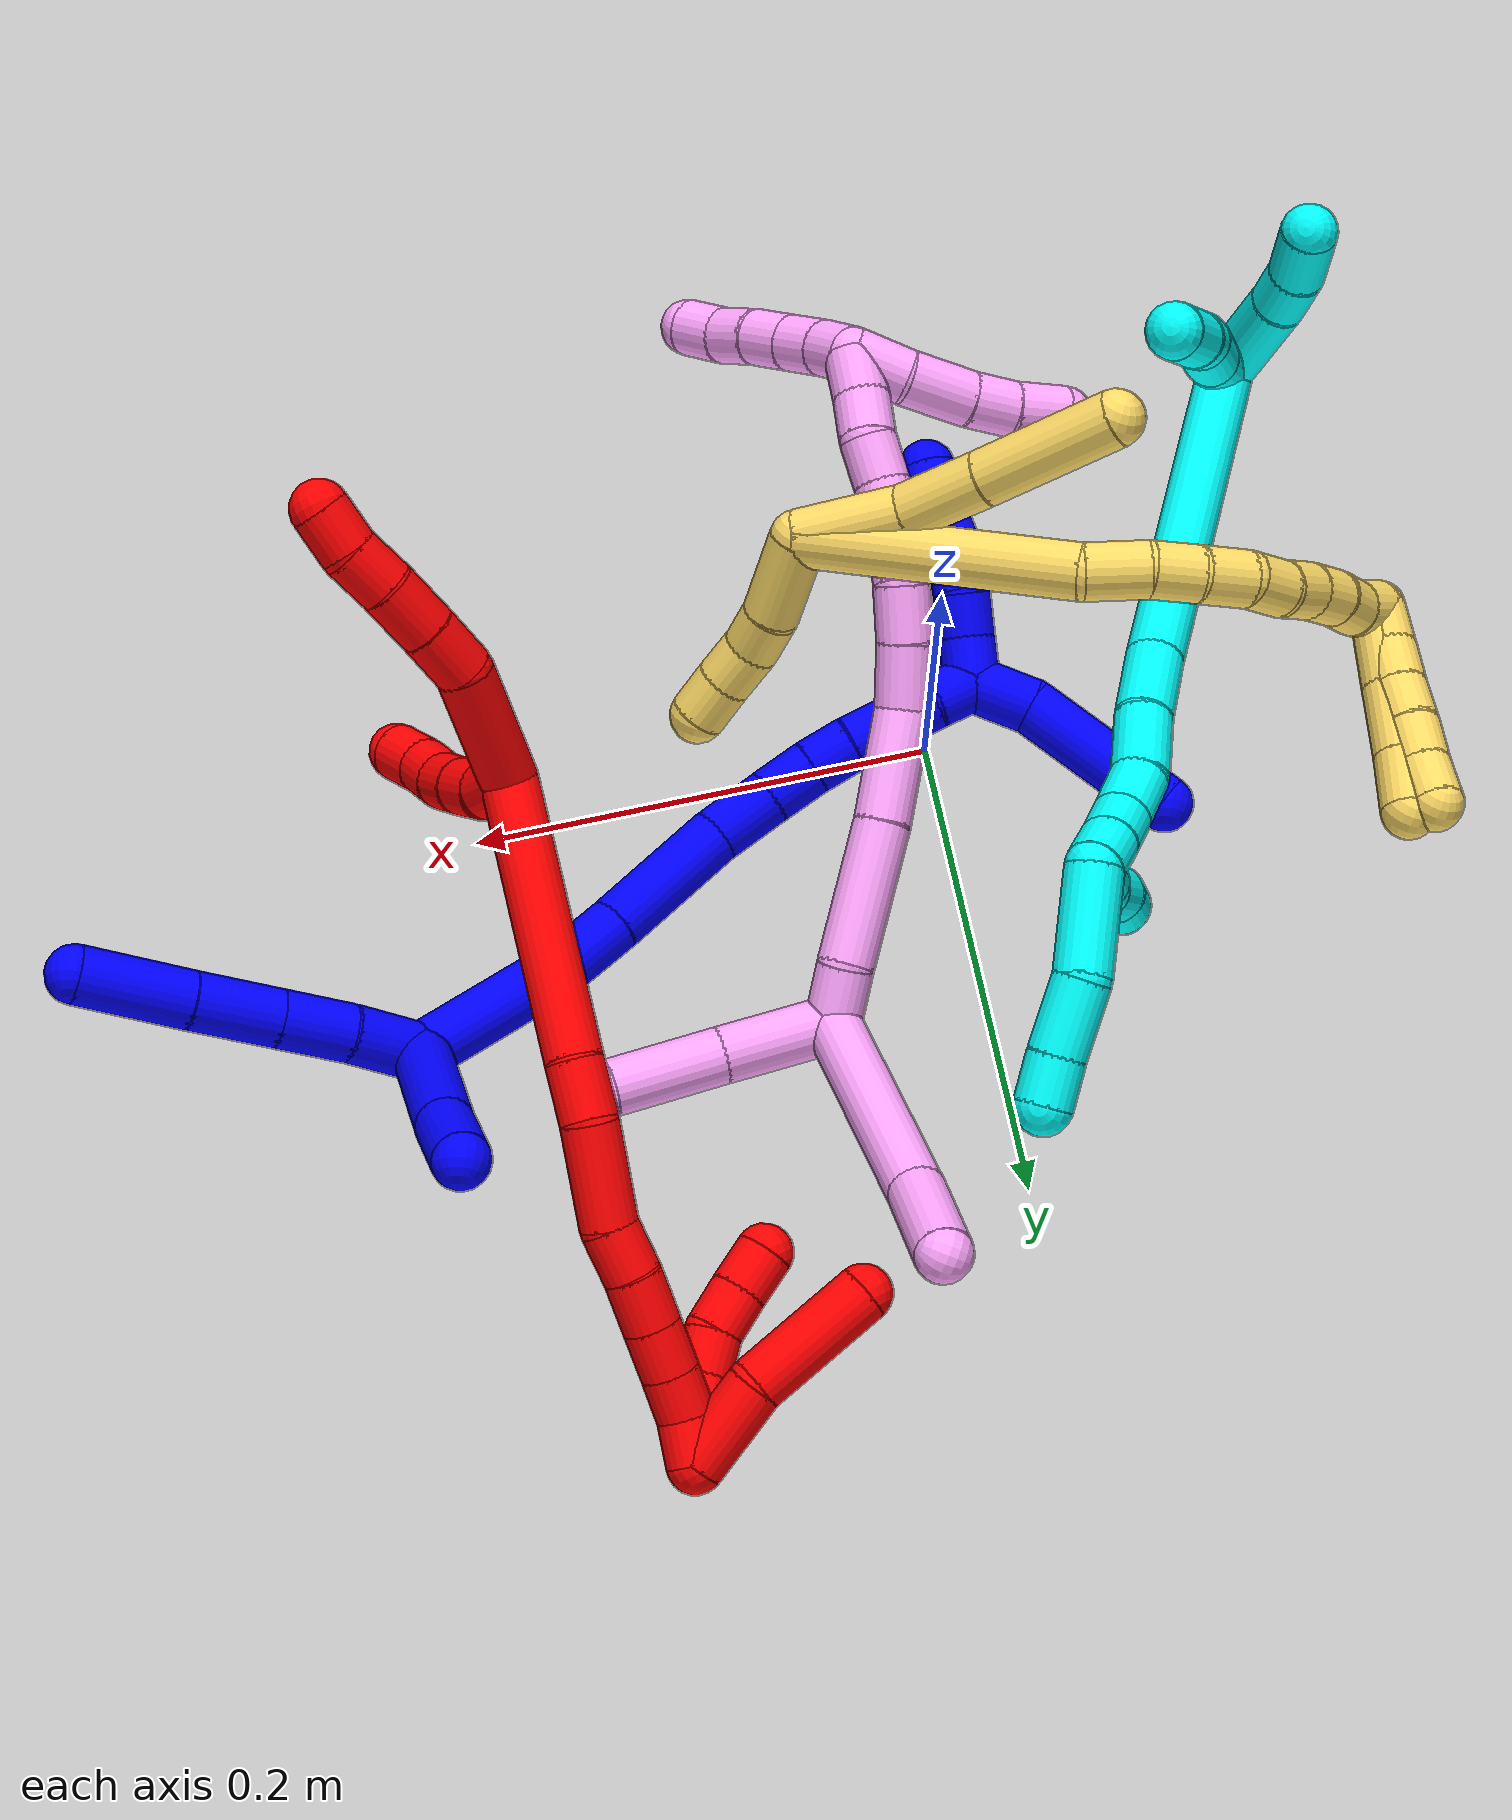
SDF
<sdf version="1.7">
 <world name="default">
  <plugin name="TubeGeneratorPlugin" filename="libtube_generator_plugin.so"/>
  <model name="photoneo_s_sensor">
   <static>1</static>
   <pose>0 0 2 1.57079 1.57079 3.14159</pose>
   <link name="link">
    <inertial><mass>0.1</mass></inertial>
    <sensor name="sensor" type="depth">
     <update_rate>30</update_rate>
     <camera>
      <horizontal_fov>1.22</horizontal_fov>
      <image><width>1920</width><height>1200</height><format>B8G8R8</format></image>
      <clip><near>0.1</near><far>4</far></clip>
      <depth_camera><output>points</output></depth_camera>
     </camera>
     <plugin name="camera_plugin" filename="libgazebo_ros_depth_camera.so">
      <baseline>0.2</baseline>
      <alwaysOn>1</alwaysOn>
      <updateRate>0.0</updateRate>
      <cameraName>camera_ir</cameraName>
      <imageTopicName>/camera/color/image_raw</imageTopicName>
      <cameraInfoTopicName>/camera/color/camera_info</cameraInfoTopicName>
      <depthImageTopicName>/camera/depth/image_raw</depthImageTopicName>
      <depthImageCameraInfoTopicName>/camera/depth/camera_info</depthImageCameraInfoTopicName>
      <pointCloudTopicName>/camera/depth/points</pointCloudTopicName>
      <frameName>fr_optical</frameName>
      <pointCloudCutoff>0.1</pointCloudCutoff>
      <pointCloudCutoffMax>2.0</pointCloudCutoffMax>
      <distortionK1>0</distortionK1>
      <distortionK2>0</distortionK2>
      <distortionK3>0</distortionK3>
      <distortionT1>0</distortionT1>
      <distortionT2>0</distortionT2>
      <CxPrime>0</CxPrime>
      <Cx>0</Cx>
      <Cy>0</Cy>
      <focalLength>0</focalLength>
      <hackBaseline>0</hackBaseline>
     </plugin>
    </sensor>
   </link>
  </model>
  <gravity>0 0 -9.8</gravity>
  <magnetic_field>6e-06 2.3e-05 -4.2e-05</magnetic_field>
  <atmosphere type="adiabatic"/>
  <physics name="default_physics" default="0" type="ode">
   <max_step_size>0.003</max_step_size>
   <real_time_factor>1</real_time_factor>
   <real_time_update_rate>1000</real_time_update_rate>
   <max_contacts>10000</max_contacts>
   <ode>
    <solver>
     <type>quick</type>
     <iters>100</iters>
     <sor>1.3</sor>
     <use_dynamic_moi_rescaling>0</use_dynamic_moi_rescaling>
    </solver>
    <constraints>
     <contact_max_correcting_vel>0</contact_max_correcting_vel>
     <contact_surface_layer>0.001</contact_surface_layer>
     <cfm>0</cfm>
     <erp>0.2</erp>
    </constraints>
   </ode>
  </physics>
  <scene><ambient>0.4 0.4 0.4 1</ambient><background>0.7 0.7 0.7 1</background><shadows>0</shadows></scene>
  <audio><device>default</device></audio>
  <spherical_coordinates>
   <surface_model>EARTH_WGS84</surface_model>
   <latitude_deg>0</latitude_deg>
   <longitude_deg>0</longitude_deg>
   <elevation>0</elevation>
   <heading_deg>0</heading_deg>
  </spherical_coordinates>
  <model name="bin">
   <static>1</static>
   <link name="bottom">
    <collision name="collision-bottom">
     <pose>0 0 -0.01 0 -0 0</pose>
     <geometry><box><size>0.8 0.6 0.02</size></box></geometry>
     <surface>
      <friction><ode><mu>100</mu><mu2>100</mu2></ode></friction>
      <contact><collide_bitmask>65535</collide_bitmask></contact>
     </surface>
    </collision>
   </link>
   <link name="west_wall">
    <collision name="collision-west_wall">
     <pose>-0.41 0 0.1 0 -0 0</pose>
     <geometry><box><size>0.02 0.6 0.2</size></box></geometry>
     <surface>
      <friction><ode><mu>100</mu><mu2>100</mu2></ode></friction>
      <contact><collide_bitmask>65535</collide_bitmask></contact>
     </surface>
    </collision>
   </link>
   <link name="east_wall">
    <collision name="collision-east_wall">
     <pose>0.41 0 0.1 0 -0 0</pose>
     <geometry><box><size>0.02 0.6 0.2</size></box></geometry>
     <surface>
      <friction><ode><mu>100</mu><mu2>100</mu2></ode></friction>
      <contact><collide_bitmask>65535</collide_bitmask></contact>
     </surface>
    </collision>
   </link>
   <link name="south_wall">
    <collision name="collision-south_wall">
     <pose>0 -0.31 0.1 0 -0 0</pose>
     <geometry><box><size>0.8 0.02 0.2</size></box></geometry>
     <surface>
      <friction><ode><mu>100</mu><mu2>100</mu2></ode></friction>
      <contact><collide_bitmask>65535</collide_bitmask></contact>
     </surface>
    </collision>
   </link>
   <link name="north_wall">
    <collision name="collision-north_wall">
     <pose>0 0.31 0.1 0 -0 0</pose>
     <geometry><box><size>0.8 0.02 0.2</size></box></geometry>
     <surface>
      <friction><ode><mu>100</mu><mu2>100</mu2></ode></friction>
      <contact><collide_bitmask>65535</collide_bitmask></contact>
     </surface>
    </collision>
   </link>
  </model>
  <model name="1">
   <static>0</static>
   <link name="1">
    <collision name="collision-cylinder-e_1_2_8">
     <pose>0.015786 -0.00438 -0.000225 1.62202 1.2998 1.34949</pose>
     <geometry><cylinder><radius>0.0125</radius><length>0.032767</length></cylinder></geometry>
     <surface>
      <friction><ode><mu>1.16</mu><mu2>1.16</mu2><slip1>0</slip1><slip2>0</slip2></ode></friction>
      <contact><ode><kp>1e+06</kp><kd>1</kd><max_vel>0</max_vel><min_depth>0.001</min_depth></ode></contact>
     </surface>
    </collision>
    <visual name="visual-cylinder-e_1_2_8">
     <pose>0.015786 -0.00438 -0.000225 1.62202 1.2998 1.34949</pose>
     <geometry><cylinder><radius>0.0125</radius><length>0.032767</length></cylinder></geometry>
     <material><ambient>0 0 1 1</ambient></material>
    </visual>
    <collision name="collision-cylinder-e_2_8_9">
     <pose>0.046989 -0.011319 -0.000441 1.56774 1.40628 1.40327</pose>
     <geometry><cylinder><radius>0.0125</radius><length>0.031257</length></cylinder></geometry>
     <surface>
      <friction><ode><mu>1.16</mu><mu2>1.16</mu2><slip1>0</slip1><slip2>0</slip2></ode></friction>
      <contact><ode><kp>1e+06</kp><kd>1</kd><max_vel>0</max_vel><min_depth>0.001</min_depth></ode></contact>
     </surface>
    </collision>
    <visual name="visual-cylinder-e_2_8_9">
     <pose>0.046989 -0.011319 -0.000441 1.56774 1.40628 1.40327</pose>
     <geometry><cylinder><radius>0.0125</radius><length>0.031257</length></cylinder></geometry>
     <material><ambient>0 0 1 1</ambient></material>
    </visual>
    <collision name="collision-cylinder-e_3_9_10">
     <pose>0.080849 -0.016947 -0.000421 1.56678 1.40597 1.402</pose>
     <geometry><cylinder><radius>0.0125</radius><length>0.037393</length></cylinder></geometry>
     <surface>
      <friction><ode><mu>1.16</mu><mu2>1.16</mu2><slip1>0</slip1><slip2>0</slip2></ode></friction>
      <contact><ode><kp>1e+06</kp><kd>1</kd><max_vel>0</max_vel><min_depth>0.001</min_depth></ode></contact>
     </surface>
    </collision>
    <visual name="visual-cylinder-e_3_9_10">
     <pose>0.080849 -0.016947 -0.000421 1.56678 1.40597 1.402</pose>
     <geometry><cylinder><radius>0.0125</radius><length>0.037393</length></cylinder></geometry>
     <material><ambient>0 0 1 1</ambient></material>
    </visual>
    <collision name="collision-cylinder-e_4_10_6">
     <pose>0.123348 -0.023311 -0.001122 1.78394 1.43148 1.64574</pose>
     <geometry><cylinder><radius>0.0125</radius><length>0.048583</length></cylinder></geometry>
     <surface>
      <friction><ode><mu>1.16</mu><mu2>1.16</mu2><slip1>0</slip1><slip2>0</slip2></ode></friction>
      <contact><ode><kp>1e+06</kp><kd>1</kd><max_vel>0</max_vel><min_depth>0.001</min_depth></ode></contact>
     </surface>
    </collision>
    <visual name="visual-cylinder-e_4_10_6">
     <pose>0.123348 -0.023311 -0.001122 1.78394 1.43148 1.64574</pose>
     <geometry><cylinder><radius>0.0125</radius><length>0.048583</length></cylinder></geometry>
     <material><ambient>0 0 1 1</ambient></material>
    </visual>
    <collision name="collision-cylinder-e_1_2_11">
     <pose>-0.002453 -0.022229 0.024875 0.729271 -0.073407 -0.028031</pose>
     <geometry><cylinder><radius>0.0125</radius><length>0.0669</length></cylinder></geometry>
     <surface>
      <friction><ode><mu>1.16</mu><mu2>1.16</mu2><slip1>0</slip1><slip2>0</slip2></ode></friction>
      <contact><ode><kp>1e+06</kp><kd>1</kd><max_vel>0</max_vel><min_depth>0.001</min_depth></ode></contact>
     </surface>
    </collision>
    <visual name="visual-cylinder-e_1_2_11">
     <pose>-0.002453 -0.022229 0.024875 0.729271 -0.073407 -0.028031</pose>
     <geometry><cylinder><radius>0.0125</radius><length>0.0669</length></cylinder></geometry>
     <material><ambient>0 0 1 1</ambient></material>
    </visual>
    <collision name="collision-cylinder-e_2_11_5">
     <pose>-0.006715 -0.055924 0.061547 0.771234 -0.109504 -0.044489</pose>
     <geometry><cylinder><radius>0.0125</radius><length>0.0331</length></cylinder></geometry>
     <surface>
      <friction><ode><mu>1.16</mu><mu2>1.16</mu2><slip1>0</slip1><slip2>0</slip2></ode></friction>
      <contact><ode><kp>1e+06</kp><kd>1</kd><max_vel>0</max_vel><min_depth>0.001</min_depth></ode></contact>
     </surface>
    </collision>
    <visual name="visual-cylinder-e_2_11_5">
     <pose>-0.006715 -0.055924 0.061547 0.771234 -0.109504 -0.044489</pose>
     <geometry><cylinder><radius>0.0125</radius><length>0.0331</length></cylinder></geometry>
     <material><ambient>0 0 1 1</ambient></material>
    </visual>
    <collision name="collision-cylinder-e_1_2_12">
     <pose>-0.028305 0.000928 -0.023647 -3.10236 -0.874447 3.05769</pose>
     <geometry><cylinder><radius>0.0125</radius><length>0.073789</length></cylinder></geometry>
     <surface>
      <friction><ode><mu>1.16</mu><mu2>1.16</mu2><slip1>0</slip1><slip2>0</slip2></ode></friction>
      <contact><ode><kp>1e+06</kp><kd>1</kd><max_vel>0</max_vel><min_depth>0.001</min_depth></ode></contact>
     </surface>
    </collision>
    <visual name="visual-cylinder-e_1_2_12">
     <pose>-0.028305 0.000928 -0.023647 -3.10236 -0.874447 3.05769</pose>
     <geometry><cylinder><radius>0.0125</radius><length>0.073789</length></cylinder></geometry>
     <material><ambient>0 0 1 1</ambient></material>
    </visual>
    <collision name="collision-cylinder-e_2_12_13">
     <pose>-0.06768 0.000393 -0.05891 3.01628 -0.757383 -2.82883</pose>
     <geometry><cylinder><radius>0.0125</radius><length>0.032228</length></cylinder></geometry>
     <surface>
      <friction><ode><mu>1.16</mu><mu2>1.16</mu2><slip1>0</slip1><slip2>0</slip2></ode></friction>
      <contact><ode><kp>1e+06</kp><kd>1</kd><max_vel>0</max_vel><min_depth>0.001</min_depth></ode></contact>
     </surface>
    </collision>
    <visual name="visual-cylinder-e_2_12_13">
     <pose>-0.06768 0.000393 -0.05891 3.01628 -0.757383 -2.82883</pose>
     <geometry><cylinder><radius>0.0125</radius><length>0.032228</length></cylinder></geometry>
     <material><ambient>0 0 1 1</ambient></material>
    </visual>
    <collision name="collision-cylinder-e_3_13_14">
     <pose>-0.099258 -0.004325 -0.093527 3.00104 -0.723241 -2.77361</pose>
     <geometry><cylinder><radius>0.0125</radius><length>0.061971</length></cylinder></geometry>
     <surface>
      <friction><ode><mu>1.16</mu><mu2>1.16</mu2><slip1>0</slip1><slip2>0</slip2></ode></friction>
      <contact><ode><kp>1e+06</kp><kd>1</kd><max_vel>0</max_vel><min_depth>0.001</min_depth></ode></contact>
     </surface>
    </collision>
    <visual name="visual-cylinder-e_3_13_14">
     <pose>-0.099258 -0.004325 -0.093527 3.00104 -0.723241 -2.77361</pose>
     <geometry><cylinder><radius>0.0125</radius><length>0.061971</length></cylinder></geometry>
     <material><ambient>0 0 1 1</ambient></material>
    </visual>
    <collision name="collision-cylinder-e_4_14_15">
     <pose>-0.130383 -0.012383 -0.125539 2.65181 -0.804823 -2.07979</pose>
     <geometry><cylinder><radius>0.0125</radius><length>0.029465</length></cylinder></geometry>
     <surface>
      <friction><ode><mu>1.16</mu><mu2>1.16</mu2><slip1>0</slip1><slip2>0</slip2></ode></friction>
      <contact><ode><kp>1e+06</kp><kd>1</kd><max_vel>0</max_vel><min_depth>0.001</min_depth></ode></contact>
     </surface>
    </collision>
    <visual name="visual-cylinder-e_4_14_15">
     <pose>-0.130383 -0.012383 -0.125539 2.65181 -0.804823 -2.07979</pose>
     <geometry><cylinder><radius>0.0125</radius><length>0.029465</length></cylinder></geometry>
     <material><ambient>0 0 1 1</ambient></material>
    </visual>
    <collision name="collision-cylinder-e_5_15_16">
     <pose>-0.149118 -0.021323 -0.141064 2.57581 -0.81083 -1.95096</pose>
     <geometry><cylinder><radius>0.0125</radius><length>0.022396</length></cylinder></geometry>
     <surface>
      <friction><ode><mu>1.16</mu><mu2>1.16</mu2><slip1>0</slip1><slip2>0</slip2></ode></friction>
      <contact><ode><kp>1e+06</kp><kd>1</kd><max_vel>0</max_vel><min_depth>0.001</min_depth></ode></contact>
     </surface>
    </collision>
    <visual name="visual-cylinder-e_5_15_16">
     <pose>-0.149118 -0.021323 -0.141064 2.57581 -0.81083 -1.95096</pose>
     <geometry><cylinder><radius>0.0125</radius><length>0.022396</length></cylinder></geometry>
     <material><ambient>0 0 1 1</ambient></material>
    </visual>
    <collision name="collision-cylinder-e_6_16_17">
     <pose>-0.164898 -0.029491 -0.152633 2.46841 -0.869793 -1.8505</pose>
     <geometry><cylinder><radius>0.0125</radius><length>0.020055</length></cylinder></geometry>
     <surface>
      <friction><ode><mu>1.16</mu><mu2>1.16</mu2><slip1>0</slip1><slip2>0</slip2></ode></friction>
      <contact><ode><kp>1e+06</kp><kd>1</kd><max_vel>0</max_vel><min_depth>0.001</min_depth></ode></contact>
     </surface>
    </collision>
    <visual name="visual-cylinder-e_6_16_17">
     <pose>-0.164898 -0.029491 -0.152633 2.46841 -0.869793 -1.8505</pose>
     <geometry><cylinder><radius>0.0125</radius><length>0.020055</length></cylinder></geometry>
     <material><ambient>0 0 1 1</ambient></material>
    </visual>
    <collision name="collision-cylinder-e_7_17_18">
     <pose>-0.180705 -0.037064 -0.162364 2.49342 -0.946801 -1.98072</pose>
     <geometry><cylinder><radius>0.0125</radius><length>0.020071</length></cylinder></geometry>
     <surface>
      <friction><ode><mu>1.16</mu><mu2>1.16</mu2><slip1>0</slip1><slip2>0</slip2></ode></friction>
      <contact><ode><kp>1e+06</kp><kd>1</kd><max_vel>0</max_vel><min_depth>0.001</min_depth></ode></contact>
     </surface>
    </collision>
    <visual name="visual-cylinder-e_7_17_18">
     <pose>-0.180705 -0.037064 -0.162364 2.49342 -0.946801 -1.98072</pose>
     <geometry><cylinder><radius>0.0125</radius><length>0.020071</length></cylinder></geometry>
     <material><ambient>0 0 1 1</ambient></material>
    </visual>
    <collision name="collision-cylinder-e_8_18_19">
     <pose>-0.196852 -0.044079 -0.171929 2.52376 -0.927436 -2.00559</pose>
     <geometry><cylinder><radius>0.0125</radius><length>0.020005</length></cylinder></geometry>
     <surface>
      <friction><ode><mu>1.16</mu><mu2>1.16</mu2><slip1>0</slip1><slip2>0</slip2></ode></friction>
      <contact><ode><kp>1e+06</kp><kd>1</kd><max_vel>0</max_vel><min_depth>0.001</min_depth></ode></contact>
     </surface>
    </collision>
    <visual name="visual-cylinder-e_8_18_19">
     <pose>-0.196852 -0.044079 -0.171929 2.52376 -0.927436 -2.00559</pose>
     <geometry><cylinder><radius>0.0125</radius><length>0.020005</length></cylinder></geometry>
     <material><ambient>0 0 1 1</ambient></material>
    </visual>
    <collision name="collision-cylinder-e_9_19_1">
     <pose>-0.213268 -0.049431 -0.181909 2.78842 -0.998279 -2.50895</pose>
     <geometry><cylinder><radius>0.0125</radius><length>0.02002</length></cylinder></geometry>
     <surface>
      <friction><ode><mu>1.16</mu><mu2>1.16</mu2><slip1>0</slip1><slip2>0</slip2></ode></friction>
      <contact><ode><kp>1e+06</kp><kd>1</kd><max_vel>0</max_vel><min_depth>0.001</min_depth></ode></contact>
     </surface>
    </collision>
    <visual name="visual-cylinder-e_9_19_1">
     <pose>-0.213268 -0.049431 -0.181909 2.78842 -0.998279 -2.50895</pose>
     <geometry><cylinder><radius>0.0125</radius><length>0.02002</length></cylinder></geometry>
     <material><ambient>0 0 1 1</ambient></material>
    </visual>
    <collision name="collision-cylinder-e_1_1_20">
     <pose>-0.234877 -0.052963 -0.182654 0.36438 -1.23213 -0.259403</pose>
     <geometry><cylinder><radius>0.0125</radius><length>0.027978</length></cylinder></geometry>
     <surface>
      <friction><ode><mu>1.16</mu><mu2>1.16</mu2><slip1>0</slip1><slip2>0</slip2></ode></friction>
      <contact><ode><kp>1e+06</kp><kd>1</kd><max_vel>0</max_vel><min_depth>0.001</min_depth></ode></contact>
     </surface>
    </collision>
    <visual name="visual-cylinder-e_1_1_20">
     <pose>-0.234877 -0.052963 -0.182654 0.36438 -1.23213 -0.259403</pose>
     <geometry><cylinder><radius>0.0125</radius><length>0.027978</length></cylinder></geometry>
     <material><ambient>0 0 1 1</ambient></material>
    </visual>
    <collision name="collision-cylinder-e_2_20_4">
     <pose>-0.277444 -0.057955 -0.157747 0.160816 -0.953861 -0.083228</pose>
     <geometry><cylinder><radius>0.0125</radius><length>0.072022</length></cylinder></geometry>
     <surface>
      <friction><ode><mu>1.16</mu><mu2>1.16</mu2><slip1>0</slip1><slip2>0</slip2></ode></friction>
      <contact><ode><kp>1e+06</kp><kd>1</kd><max_vel>0</max_vel><min_depth>0.001</min_depth></ode></contact>
     </surface>
    </collision>
    <visual name="visual-cylinder-e_2_20_4">
     <pose>-0.277444 -0.057955 -0.157747 0.160816 -0.953861 -0.083228</pose>
     <geometry><cylinder><radius>0.0125</radius><length>0.072022</length></cylinder></geometry>
     <material><ambient>0 0 1 1</ambient></material>
    </visual>
    <collision name="collision-cylinder-e_1_1_21">
     <pose>-0.219596 -0.053722 -0.196474 2.89202 0.210211 1.39848</pose>
     <geometry><cylinder><radius>0.0125</radius><length>0.02</length></cylinder></geometry>
     <surface>
      <friction><ode><mu>1.16</mu><mu2>1.16</mu2><slip1>0</slip1><slip2>0</slip2></ode></friction>
      <contact><ode><kp>1e+06</kp><kd>1</kd><max_vel>0</max_vel><min_depth>0.001</min_depth></ode></contact>
     </surface>
    </collision>
    <visual name="visual-cylinder-e_1_1_21">
     <pose>-0.219596 -0.053722 -0.196474 2.89202 0.210211 1.39848</pose>
     <geometry><cylinder><radius>0.0125</radius><length>0.02</length></cylinder></geometry>
     <material><ambient>0 0 1 1</ambient></material>
    </visual>
    <collision name="collision-cylinder-e_2_21_22">
     <pose>-0.21489 -0.060505 -0.214557 2.67199 0.265027 1.01675</pose>
     <geometry><cylinder><radius>0.0125</radius><length>0.02</length></cylinder></geometry>
     <surface>
      <friction><ode><mu>1.16</mu><mu2>1.16</mu2><slip1>0</slip1><slip2>0</slip2></ode></friction>
      <contact><ode><kp>1e+06</kp><kd>1</kd><max_vel>0</max_vel><min_depth>0.001</min_depth></ode></contact>
     </surface>
    </collision>
    <visual name="visual-cylinder-e_2_21_22">
     <pose>-0.21489 -0.060505 -0.214557 2.67199 0.265027 1.01675</pose>
     <geometry><cylinder><radius>0.0125</radius><length>0.02</length></cylinder></geometry>
     <material><ambient>0 0 1 1</ambient></material>
    </visual>
    <collision name="collision-cylinder-e_3_22_23">
     <pose>-0.209543 -0.067425 -0.232439 2.87299 0.276288 1.59934</pose>
     <geometry><cylinder><radius>0.0125</radius><length>0.02</length></cylinder></geometry>
     <surface>
      <friction><ode><mu>1.16</mu><mu2>1.16</mu2><slip1>0</slip1><slip2>0</slip2></ode></friction>
      <contact><ode><kp>1e+06</kp><kd>1</kd><max_vel>0</max_vel><min_depth>0.001</min_depth></ode></contact>
     </surface>
    </collision>
    <visual name="visual-cylinder-e_3_22_23">
     <pose>-0.209543 -0.067425 -0.232439 2.87299 0.276288 1.59934</pose>
     <geometry><cylinder><radius>0.0125</radius><length>0.02</length></cylinder></geometry>
     <material><ambient>0 0 1 1</ambient></material>
    </visual>
    <collision name="collision-cylinder-e_4_23_24">
     <pose>-0.202899 -0.070343 -0.250909 3.10196 0.402352 2.94784</pose>
     <geometry><cylinder><radius>0.0125</radius><length>0.02</length></cylinder></geometry>
     <surface>
      <friction><ode><mu>1.16</mu><mu2>1.16</mu2><slip1>0</slip1><slip2>0</slip2></ode></friction>
      <contact><ode><kp>1e+06</kp><kd>1</kd><max_vel>0</max_vel><min_depth>0.001</min_depth></ode></contact>
     </surface>
    </collision>
    <visual name="visual-cylinder-e_4_23_24">
     <pose>-0.202899 -0.070343 -0.250909 3.10196 0.402352 2.94784</pose>
     <geometry><cylinder><radius>0.0125</radius><length>0.02</length></cylinder></geometry>
     <material><ambient>0 0 1 1</ambient></material>
    </visual>
    <collision name="collision-cylinder-e_5_24_3">
     <pose>-0.195946 -0.071929 -0.269552 3.01311 0.308605 2.35725</pose>
     <geometry><cylinder><radius>0.0125</radius><length>0.02</length></cylinder></geometry>
     <surface>
      <friction><ode><mu>1.16</mu><mu2>1.16</mu2><slip1>0</slip1><slip2>0</slip2></ode></friction>
      <contact><ode><kp>1e+06</kp><kd>1</kd><max_vel>0</max_vel><min_depth>0.001</min_depth></ode></contact>
     </surface>
    </collision>
    <visual name="visual-cylinder-e_5_24_3">
     <pose>-0.195946 -0.071929 -0.269552 3.01311 0.308605 2.35725</pose>
     <geometry><cylinder><radius>0.0125</radius><length>0.02</length></cylinder></geometry>
     <material><ambient>0 0 1 1</ambient></material>
    </visual>
    <collision name="collision-sphere-3">
     <pose>-0.192908 -0.073149 -0.279001 0 -0 0</pose>
     <geometry><sphere><radius>0.0125</radius></sphere></geometry>
     <surface>
      <friction><ode><mu>1.16</mu><mu2>1.16</mu2><slip1>0</slip1><slip2>0</slip2></ode></friction>
      <contact><ode><kp>1e+06</kp><kd>1</kd><max_vel>0</max_vel><min_depth>0.001</min_depth></ode></contact>
     </surface>
    </collision>
    <visual name="visual-sphere-3">
     <pose>-0.192908 -0.073149 -0.279001 0 -0 0</pose>
     <geometry><sphere><radius>0.0125</radius></sphere></geometry>
     <material><ambient>0 0 1 1</ambient></material>
    </visual>
    <collision name="collision-sphere-24">
     <pose>-0.198983 -0.070708 -0.260103 0 -0 0</pose>
     <geometry><sphere><radius>0.0125</radius></sphere></geometry>
     <surface>
      <friction><ode><mu>1.16</mu><mu2>1.16</mu2><slip1>0</slip1><slip2>0</slip2></ode></friction>
      <contact><ode><kp>1e+06</kp><kd>1</kd><max_vel>0</max_vel><min_depth>0.001</min_depth></ode></contact>
     </surface>
    </collision>
    <visual name="visual-sphere-24">
     <pose>-0.198983 -0.070708 -0.260103 0 -0 0</pose>
     <geometry><sphere><radius>0.0125</radius></sphere></geometry>
     <material><ambient>0 0 1 1</ambient></material>
    </visual>
    <collision name="collision-sphere-23">
     <pose>-0.206815 -0.069979 -0.241715 0 -0 0</pose>
     <geometry><sphere><radius>0.0125</radius></sphere></geometry>
     <surface>
      <friction><ode><mu>1.16</mu><mu2>1.16</mu2><slip1>0</slip1><slip2>0</slip2></ode></friction>
      <contact><ode><kp>1e+06</kp><kd>1</kd><max_vel>0</max_vel><min_depth>0.001</min_depth></ode></contact>
     </surface>
    </collision>
    <visual name="visual-sphere-23">
     <pose>-0.206815 -0.069979 -0.241715 0 -0 0</pose>
     <geometry><sphere><radius>0.0125</radius></sphere></geometry>
     <material><ambient>0 0 1 1</ambient></material>
    </visual>
    <collision name="collision-sphere-22">
     <pose>-0.21227 -0.064872 -0.223163 0 -0 0</pose>
     <geometry><sphere><radius>0.0125</radius></sphere></geometry>
     <surface>
      <friction><ode><mu>1.16</mu><mu2>1.16</mu2><slip1>0</slip1><slip2>0</slip2></ode></friction>
      <contact><ode><kp>1e+06</kp><kd>1</kd><max_vel>0</max_vel><min_depth>0.001</min_depth></ode></contact>
     </surface>
    </collision>
    <visual name="visual-sphere-22">
     <pose>-0.21227 -0.064872 -0.223163 0 -0 0</pose>
     <geometry><sphere><radius>0.0125</radius></sphere></geometry>
     <material><ambient>0 0 1 1</ambient></material>
    </visual>
    <collision name="collision-sphere-21">
     <pose>-0.217509 -0.056138 -0.205951 0 -0 0</pose>
     <geometry><sphere><radius>0.0125</radius></sphere></geometry>
     <surface>
      <friction><ode><mu>1.16</mu><mu2>1.16</mu2><slip1>0</slip1><slip2>0</slip2></ode></friction>
      <contact><ode><kp>1e+06</kp><kd>1</kd><max_vel>0</max_vel><min_depth>0.001</min_depth></ode></contact>
     </surface>
    </collision>
    <visual name="visual-sphere-21">
     <pose>-0.217509 -0.056138 -0.205951 0 -0 0</pose>
     <geometry><sphere><radius>0.0125</radius></sphere></geometry>
     <material><ambient>0 0 1 1</ambient></material>
    </visual>
    <collision name="collision-sphere-4">
     <pose>-0.306816 -0.061291 -0.137182 0 -0 0</pose>
     <geometry><sphere><radius>0.0125</radius></sphere></geometry>
     <surface>
      <friction><ode><mu>1.16</mu><mu2>1.16</mu2><slip1>0</slip1><slip2>0</slip2></ode></friction>
      <contact><ode><kp>1e+06</kp><kd>1</kd><max_vel>0</max_vel><min_depth>0.001</min_depth></ode></contact>
     </surface>
    </collision>
    <visual name="visual-sphere-4">
     <pose>-0.306816 -0.061291 -0.137182 0 -0 0</pose>
     <geometry><sphere><radius>0.0125</radius></sphere></geometry>
     <material><ambient>0 0 1 1</ambient></material>
    </visual>
    <collision name="collision-sphere-20">
     <pose>-0.248072 -0.054619 -0.178312 0 -0 0</pose>
     <geometry><sphere><radius>0.0125</radius></sphere></geometry>
     <surface>
      <friction><ode><mu>1.16</mu><mu2>1.16</mu2><slip1>0</slip1><slip2>0</slip2></ode></friction>
      <contact><ode><kp>1e+06</kp><kd>1</kd><max_vel>0</max_vel><min_depth>0.001</min_depth></ode></contact>
     </surface>
    </collision>
    <visual name="visual-sphere-20">
     <pose>-0.248072 -0.054619 -0.178312 0 -0 0</pose>
     <geometry><sphere><radius>0.0125</radius></sphere></geometry>
     <material><ambient>0 0 1 1</ambient></material>
    </visual>
    <collision name="collision-sphere-11">
     <pose>-0.004907 -0.044457 0.049751 0 -0 0</pose>
     <geometry><sphere><radius>0.0125</radius></sphere></geometry>
     <surface>
      <friction><ode><mu>1.16</mu><mu2>1.16</mu2><slip1>0</slip1><slip2>0</slip2></ode></friction>
      <contact><ode><kp>1e+06</kp><kd>1</kd><max_vel>0</max_vel><min_depth>0.001</min_depth></ode></contact>
     </surface>
    </collision>
    <visual name="visual-sphere-11">
     <pose>-0.004907 -0.044457 0.049751 0 -0 0</pose>
     <geometry><sphere><radius>0.0125</radius></sphere></geometry>
     <material><ambient>0 0 1 1</ambient></material>
    </visual>
    <collision name="collision-sphere-6">
     <pose>0.147405 -0.026608 -0.001836 0 -0 0</pose>
     <geometry><sphere><radius>0.0125</radius></sphere></geometry>
     <surface>
      <friction><ode><mu>1.16</mu><mu2>1.16</mu2><slip1>0</slip1><slip2>0</slip2></ode></friction>
      <contact><ode><kp>1e+06</kp><kd>1</kd><max_vel>0</max_vel><min_depth>0.001</min_depth></ode></contact>
     </surface>
    </collision>
    <visual name="visual-sphere-6">
     <pose>0.147405 -0.026608 -0.001836 0 -0 0</pose>
     <geometry><sphere><radius>0.0125</radius></sphere></geometry>
     <material><ambient>0 0 1 1</ambient></material>
    </visual>
    <collision name="collision-sphere-10">
     <pose>0.099292 -0.020014 -0.000409 0 -0 0</pose>
     <geometry><sphere><radius>0.0125</radius></sphere></geometry>
     <surface>
      <friction><ode><mu>1.16</mu><mu2>1.16</mu2><slip1>0</slip1><slip2>0</slip2></ode></friction>
      <contact><ode><kp>1e+06</kp><kd>1</kd><max_vel>0</max_vel><min_depth>0.001</min_depth></ode></contact>
     </surface>
    </collision>
    <visual name="visual-sphere-10">
     <pose>0.099292 -0.020014 -0.000409 0 -0 0</pose>
     <geometry><sphere><radius>0.0125</radius></sphere></geometry>
     <material><ambient>0 0 1 1</ambient></material>
    </visual>
    <collision name="collision-sphere-9">
     <pose>0.062406 -0.013879 -0.000433 0 -0 0</pose>
     <geometry><sphere><radius>0.0125</radius></sphere></geometry>
     <surface>
      <friction><ode><mu>1.16</mu><mu2>1.16</mu2><slip1>0</slip1><slip2>0</slip2></ode></friction>
      <contact><ode><kp>1e+06</kp><kd>1</kd><max_vel>0</max_vel><min_depth>0.001</min_depth></ode></contact>
     </surface>
    </collision>
    <visual name="visual-sphere-9">
     <pose>0.062406 -0.013879 -0.000433 0 -0 0</pose>
     <geometry><sphere><radius>0.0125</radius></sphere></geometry>
     <material><ambient>0 0 1 1</ambient></material>
    </visual>
    <collision name="collision-sphere-2">
     <geometry><sphere><radius>0.0125</radius></sphere></geometry>
     <surface>
      <friction><ode><mu>1.16</mu><mu2>1.16</mu2><slip1>0</slip1><slip2>0</slip2></ode></friction>
      <contact><ode><kp>1e+06</kp><kd>1</kd><max_vel>0</max_vel><min_depth>0.001</min_depth></ode></contact>
     </surface>
    </collision>
    <visual name="visual-sphere-2">
     <geometry><sphere><radius>0.0125</radius></sphere></geometry>
     <material><ambient>0 0 1 1</ambient></material>
    </visual>
    <collision name="collision-sphere-19">
     <pose>-0.204855 -0.047555 -0.17682 0 -0 0</pose>
     <geometry><sphere><radius>0.0125</radius></sphere></geometry>
     <surface>
      <friction><ode><mu>1.16</mu><mu2>1.16</mu2><slip1>0</slip1><slip2>0</slip2></ode></friction>
      <contact><ode><kp>1e+06</kp><kd>1</kd><max_vel>0</max_vel><min_depth>0.001</min_depth></ode></contact>
     </surface>
    </collision>
    <visual name="visual-sphere-19">
     <pose>-0.204855 -0.047555 -0.17682 0 -0 0</pose>
     <geometry><sphere><radius>0.0125</radius></sphere></geometry>
     <material><ambient>0 0 1 1</ambient></material>
    </visual>
    <collision name="collision-sphere-8">
     <pose>0.031571 -0.00876 -0.000449 0 -0 0</pose>
     <geometry><sphere><radius>0.0125</radius></sphere></geometry>
     <surface>
      <friction><ode><mu>1.16</mu><mu2>1.16</mu2><slip1>0</slip1><slip2>0</slip2></ode></friction>
      <contact><ode><kp>1e+06</kp><kd>1</kd><max_vel>0</max_vel><min_depth>0.001</min_depth></ode></contact>
     </surface>
    </collision>
    <visual name="visual-sphere-8">
     <pose>0.031571 -0.00876 -0.000449 0 -0 0</pose>
     <geometry><sphere><radius>0.0125</radius></sphere></geometry>
     <material><ambient>0 0 1 1</ambient></material>
    </visual>
    <collision name="collision-sphere-5">
     <pose>-0.008524 -0.06739 0.073343 0 -0 0</pose>
     <geometry><sphere><radius>0.0125</radius></sphere></geometry>
     <surface>
      <friction><ode><mu>1.16</mu><mu2>1.16</mu2><slip1>0</slip1><slip2>0</slip2></ode></friction>
      <contact><ode><kp>1e+06</kp><kd>1</kd><max_vel>0</max_vel><min_depth>0.001</min_depth></ode></contact>
     </surface>
    </collision>
    <visual name="visual-sphere-5">
     <pose>-0.008524 -0.06739 0.073343 0 -0 0</pose>
     <geometry><sphere><radius>0.0125</radius></sphere></geometry>
     <material><ambient>0 0 1 1</ambient></material>
    </visual>
    <collision name="collision-sphere-12">
     <pose>-0.05661 0.001856 -0.047293 0 -0 0</pose>
     <geometry><sphere><radius>0.0125</radius></sphere></geometry>
     <surface>
      <friction><ode><mu>1.16</mu><mu2>1.16</mu2><slip1>0</slip1><slip2>0</slip2></ode></friction>
      <contact><ode><kp>1e+06</kp><kd>1</kd><max_vel>0</max_vel><min_depth>0.001</min_depth></ode></contact>
     </surface>
    </collision>
    <visual name="visual-sphere-12">
     <pose>-0.05661 0.001856 -0.047293 0 -0 0</pose>
     <geometry><sphere><radius>0.0125</radius></sphere></geometry>
     <material><ambient>0 0 1 1</ambient></material>
    </visual>
    <collision name="collision-sphere-13">
     <pose>-0.078751 -0.00107 -0.070527 0 -0 0</pose>
     <geometry><sphere><radius>0.0125</radius></sphere></geometry>
     <surface>
      <friction><ode><mu>1.16</mu><mu2>1.16</mu2><slip1>0</slip1><slip2>0</slip2></ode></friction>
      <contact><ode><kp>1e+06</kp><kd>1</kd><max_vel>0</max_vel><min_depth>0.001</min_depth></ode></contact>
     </surface>
    </collision>
    <visual name="visual-sphere-13">
     <pose>-0.078751 -0.00107 -0.070527 0 -0 0</pose>
     <geometry><sphere><radius>0.0125</radius></sphere></geometry>
     <material><ambient>0 0 1 1</ambient></material>
    </visual>
    <collision name="collision-sphere-14">
     <pose>-0.119765 -0.007579 -0.116527 0 -0 0</pose>
     <geometry><sphere><radius>0.0125</radius></sphere></geometry>
     <surface>
      <friction><ode><mu>1.16</mu><mu2>1.16</mu2><slip1>0</slip1><slip2>0</slip2></ode></friction>
      <contact><ode><kp>1e+06</kp><kd>1</kd><max_vel>0</max_vel><min_depth>0.001</min_depth></ode></contact>
     </surface>
    </collision>
    <visual name="visual-sphere-14">
     <pose>-0.119765 -0.007579 -0.116527 0 -0 0</pose>
     <geometry><sphere><radius>0.0125</radius></sphere></geometry>
     <material><ambient>0 0 1 1</ambient></material>
    </visual>
    <collision name="collision-sphere-15">
     <pose>-0.141 -0.017188 -0.134552 0 -0 0</pose>
     <geometry><sphere><radius>0.0125</radius></sphere></geometry>
     <surface>
      <friction><ode><mu>1.16</mu><mu2>1.16</mu2><slip1>0</slip1><slip2>0</slip2></ode></friction>
      <contact><ode><kp>1e+06</kp><kd>1</kd><max_vel>0</max_vel><min_depth>0.001</min_depth></ode></contact>
     </surface>
    </collision>
    <visual name="visual-sphere-15">
     <pose>-0.141 -0.017188 -0.134552 0 -0 0</pose>
     <geometry><sphere><radius>0.0125</radius></sphere></geometry>
     <material><ambient>0 0 1 1</ambient></material>
    </visual>
    <collision name="collision-sphere-16">
     <pose>-0.157235 -0.025459 -0.147577 0 -0 0</pose>
     <geometry><sphere><radius>0.0125</radius></sphere></geometry>
     <surface>
      <friction><ode><mu>1.16</mu><mu2>1.16</mu2><slip1>0</slip1><slip2>0</slip2></ode></friction>
      <contact><ode><kp>1e+06</kp><kd>1</kd><max_vel>0</max_vel><min_depth>0.001</min_depth></ode></contact>
     </surface>
    </collision>
    <visual name="visual-sphere-16">
     <pose>-0.157235 -0.025459 -0.147577 0 -0 0</pose>
     <geometry><sphere><radius>0.0125</radius></sphere></geometry>
     <material><ambient>0 0 1 1</ambient></material>
    </visual>
    <collision name="collision-sphere-17">
     <pose>-0.17256 -0.033523 -0.15769 0 -0 0</pose>
     <geometry><sphere><radius>0.0125</radius></sphere></geometry>
     <surface>
      <friction><ode><mu>1.16</mu><mu2>1.16</mu2><slip1>0</slip1><slip2>0</slip2></ode></friction>
      <contact><ode><kp>1e+06</kp><kd>1</kd><max_vel>0</max_vel><min_depth>0.001</min_depth></ode></contact>
     </surface>
    </collision>
    <visual name="visual-sphere-17">
     <pose>-0.17256 -0.033523 -0.15769 0 -0 0</pose>
     <geometry><sphere><radius>0.0125</radius></sphere></geometry>
     <material><ambient>0 0 1 1</ambient></material>
    </visual>
    <collision name="collision-sphere-18">
     <pose>-0.188849 -0.040604 -0.167038 0 -0 0</pose>
     <geometry><sphere><radius>0.0125</radius></sphere></geometry>
     <surface>
      <friction><ode><mu>1.16</mu><mu2>1.16</mu2><slip1>0</slip1><slip2>0</slip2></ode></friction>
      <contact><ode><kp>1e+06</kp><kd>1</kd><max_vel>0</max_vel><min_depth>0.001</min_depth></ode></contact>
     </surface>
    </collision>
    <visual name="visual-sphere-18">
     <pose>-0.188849 -0.040604 -0.167038 0 -0 0</pose>
     <geometry><sphere><radius>0.0125</radius></sphere></geometry>
     <material><ambient>0 0 1 1</ambient></material>
    </visual>
    <collision name="collision-sphere-1">
     <pose>-0.221682 -0.051306 -0.186997 0 -0 0</pose>
     <geometry><sphere><radius>0.0125</radius></sphere></geometry>
     <surface>
      <friction><ode><mu>1.16</mu><mu2>1.16</mu2><slip1>0</slip1><slip2>0</slip2></ode></friction>
      <contact><ode><kp>1e+06</kp><kd>1</kd><max_vel>0</max_vel><min_depth>0.001</min_depth></ode></contact>
     </surface>
    </collision>
    <visual name="visual-sphere-1">
     <pose>-0.221682 -0.051306 -0.186997 0 -0 0</pose>
     <geometry><sphere><radius>0.0125</radius></sphere></geometry>
     <material><ambient>0 0 1 1</ambient></material>
    </visual>
    <inertial>
     <pose>-0.092719 -0.029296 -0.087786 0 -0 0</pose>
     <mass>0.75</mass>
     <inertia><ixx>-9e-06</ixx><ixy>0</ixy><ixz>0</ixz><iyy>0.000138</iyy><iyz>0</iyz><izz>8.3e-05</izz></inertia>
    </inertial>
   </link>
   <pose>0.239881 0.100484 0.054288 -1.39108 -0.251859 -0.291567</pose>
  </model>
  <model name="2">
   <static>0</static>
   <link name="2">
    <collision name="collision-cylinder-e_1_2_8">
     <pose>-0.018435 -0.007077 -0.021804 2.82774 -0.677282 -2.29714</pose>
     <geometry><cylinder><radius>0.0125</radius><length>0.058835</length></cylinder></geometry>
     <surface>
      <friction><ode><mu>1.16</mu><mu2>1.16</mu2><slip1>0</slip1><slip2>0</slip2></ode></friction>
      <contact><ode><kp>1e+06</kp><kd>1</kd><max_vel>0</max_vel><min_depth>0.001</min_depth></ode></contact>
     </surface>
    </collision>
    <visual name="visual-cylinder-e_1_2_8">
     <pose>-0.018435 -0.007077 -0.021804 2.82774 -0.677282 -2.29714</pose>
     <geometry><cylinder><radius>0.0125</radius><length>0.058835</length></cylinder></geometry>
     <material><ambient>1 0 0 1</ambient></material>
    </visual>
    <collision name="collision-cylinder-e_2_8_9">
     <pose>-0.041459 -0.019811 -0.05344 2.61952 -0.384449 -1.2593</pose>
     <geometry><cylinder><radius>0.0125</radius><length>0.02447</length></cylinder></geometry>
     <surface>
      <friction><ode><mu>1.16</mu><mu2>1.16</mu2><slip1>0</slip1><slip2>0</slip2></ode></friction>
      <contact><ode><kp>1e+06</kp><kd>1</kd><max_vel>0</max_vel><min_depth>0.001</min_depth></ode></contact>
     </surface>
    </collision>
    <visual name="visual-cylinder-e_2_8_9">
     <pose>-0.041459 -0.019811 -0.05344 2.61952 -0.384449 -1.2593</pose>
     <geometry><cylinder><radius>0.0125</radius><length>0.02447</length></cylinder></geometry>
     <material><ambient>1 0 0 1</ambient></material>
    </visual>
    <collision name="collision-cylinder-e_3_9_10">
     <pose>-0.050031 -0.031298 -0.073516 2.62412 -0.32586 -1.11158</pose>
     <geometry><cylinder><radius>0.0125</radius><length>0.024886</length></cylinder></geometry>
     <surface>
      <friction><ode><mu>1.16</mu><mu2>1.16</mu2><slip1>0</slip1><slip2>0</slip2></ode></friction>
      <contact><ode><kp>1e+06</kp><kd>1</kd><max_vel>0</max_vel><min_depth>0.001</min_depth></ode></contact>
     </surface>
    </collision>
    <visual name="visual-cylinder-e_3_9_10">
     <pose>-0.050031 -0.031298 -0.073516 2.62412 -0.32586 -1.11158</pose>
     <geometry><cylinder><radius>0.0125</radius><length>0.024886</length></cylinder></geometry>
     <material><ambient>1 0 0 1</ambient></material>
    </visual>
    <collision name="collision-cylinder-e_4_10_11">
     <pose>-0.056044 -0.042187 -0.09284 2.63338 -0.192871 -0.71309</pose>
     <geometry><cylinder><radius>0.0125</radius><length>0.021178</length></cylinder></geometry>
     <surface>
      <friction><ode><mu>1.16</mu><mu2>1.16</mu2><slip1>0</slip1><slip2>0</slip2></ode></friction>
      <contact><ode><kp>1e+06</kp><kd>1</kd><max_vel>0</max_vel><min_depth>0.001</min_depth></ode></contact>
     </surface>
    </collision>
    <visual name="visual-cylinder-e_4_10_11">
     <pose>-0.056044 -0.042187 -0.09284 2.63338 -0.192871 -0.71309</pose>
     <geometry><cylinder><radius>0.0125</radius><length>0.021178</length></cylinder></geometry>
     <material><ambient>1 0 0 1</ambient></material>
    </visual>
    <collision name="collision-cylinder-e_5_11_6">
     <pose>-0.060004 -0.049891 -0.111701 2.87729 -0.188178 -1.2347</pose>
     <geometry><cylinder><radius>0.0125</radius><length>0.020631</length></cylinder></geometry>
     <surface>
      <friction><ode><mu>1.16</mu><mu2>1.16</mu2><slip1>0</slip1><slip2>0</slip2></ode></friction>
      <contact><ode><kp>1e+06</kp><kd>1</kd><max_vel>0</max_vel><min_depth>0.001</min_depth></ode></contact>
     </surface>
    </collision>
    <visual name="visual-cylinder-e_5_11_6">
     <pose>-0.060004 -0.049891 -0.111701 2.87729 -0.188178 -1.2347</pose>
     <geometry><cylinder><radius>0.0125</radius><length>0.020631</length></cylinder></geometry>
     <material><ambient>1 0 0 1</ambient></material>
    </visual>
    <collision name="collision-cylinder-e_1_2_12">
     <pose>0.009802 -0.001395 -0.001402 2.35848 1.37171 2.20712</pose>
     <geometry><cylinder><radius>0.0125</radius><length>0.02</length></cylinder></geometry>
     <surface>
      <friction><ode><mu>1.16</mu><mu2>1.16</mu2><slip1>0</slip1><slip2>0</slip2></ode></friction>
      <contact><ode><kp>1e+06</kp><kd>1</kd><max_vel>0</max_vel><min_depth>0.001</min_depth></ode></contact>
     </surface>
    </collision>
    <visual name="visual-cylinder-e_1_2_12">
     <pose>0.009802 -0.001395 -0.001402 2.35848 1.37171 2.20712</pose>
     <geometry><cylinder><radius>0.0125</radius><length>0.02</length></cylinder></geometry>
     <material><ambient>1 0 0 1</ambient></material>
    </visual>
    <collision name="collision-cylinder-e_2_12_13">
     <pose>0.028669 -0.002758 -0.007028 -3.13391 1.13461 -3.12954</pose>
     <geometry><cylinder><radius>0.0125</radius><length>0.02</length></cylinder></geometry>
     <surface>
      <friction><ode><mu>1.16</mu><mu2>1.16</mu2><slip1>0</slip1><slip2>0</slip2></ode></friction>
      <contact><ode><kp>1e+06</kp><kd>1</kd><max_vel>0</max_vel><min_depth>0.001</min_depth></ode></contact>
     </surface>
    </collision>
    <visual name="visual-cylinder-e_2_12_13">
     <pose>0.028669 -0.002758 -0.007028 -3.13391 1.13461 -3.12954</pose>
     <geometry><cylinder><radius>0.0125</radius><length>0.02</length></cylinder></geometry>
     <material><ambient>1 0 0 1</ambient></material>
    </visual>
    <collision name="collision-cylinder-e_3_13_14">
     <pose>0.046821 -0.002026 -0.015365 -2.97312 1.14046 -2.87976</pose>
     <geometry><cylinder><radius>0.0125</radius><length>0.02</length></cylinder></geometry>
     <surface>
      <friction><ode><mu>1.16</mu><mu2>1.16</mu2><slip1>0</slip1><slip2>0</slip2></ode></friction>
      <contact><ode><kp>1e+06</kp><kd>1</kd><max_vel>0</max_vel><min_depth>0.001</min_depth></ode></contact>
     </surface>
    </collision>
    <visual name="visual-cylinder-e_3_13_14">
     <pose>0.046821 -0.002026 -0.015365 -2.97312 1.14046 -2.87976</pose>
     <geometry><cylinder><radius>0.0125</radius><length>0.02</length></cylinder></geometry>
     <material><ambient>1 0 0 1</ambient></material>
    </visual>
    <collision name="collision-cylinder-e_4_14_15">
     <pose>0.063945 -0.000127 -0.025307 -2.93863 0.933359 -2.74272</pose>
     <geometry><cylinder><radius>0.0125</radius><length>0.02</length></cylinder></geometry>
     <surface>
      <friction><ode><mu>1.16</mu><mu2>1.16</mu2><slip1>0</slip1><slip2>0</slip2></ode></friction>
      <contact><ode><kp>1e+06</kp><kd>1</kd><max_vel>0</max_vel><min_depth>0.001</min_depth></ode></contact>
     </surface>
    </collision>
    <visual name="visual-cylinder-e_4_14_15">
     <pose>0.063945 -0.000127 -0.025307 -2.93863 0.933359 -2.74272</pose>
     <geometry><cylinder><radius>0.0125</radius><length>0.02</length></cylinder></geometry>
     <material><ambient>1 0 0 1</ambient></material>
    </visual>
    <collision name="collision-cylinder-e_5_15_5">
     <pose>0.079567 0.000206 -0.037595 3.00818 0.861066 2.8527</pose>
     <geometry><cylinder><radius>0.0125</radius><length>0.02</length></cylinder></geometry>
     <surface>
      <friction><ode><mu>1.16</mu><mu2>1.16</mu2><slip1>0</slip1><slip2>0</slip2></ode></friction>
      <contact><ode><kp>1e+06</kp><kd>1</kd><max_vel>0</max_vel><min_depth>0.001</min_depth></ode></contact>
     </surface>
    </collision>
    <visual name="visual-cylinder-e_5_15_5">
     <pose>0.079567 0.000206 -0.037595 3.00818 0.861066 2.8527</pose>
     <geometry><cylinder><radius>0.0125</radius><length>0.02</length></cylinder></geometry>
     <material><ambient>1 0 0 1</ambient></material>
    </visual>
    <collision name="collision-cylinder-e_1_2_16">
     <pose>-0.003641 -0.016267 0.059428 0.26719 -0.05902 -0.007934</pose>
     <geometry><cylinder><radius>0.0125</radius><length>0.123443</length></cylinder></geometry>
     <surface>
      <friction><ode><mu>1.16</mu><mu2>1.16</mu2><slip1>0</slip1><slip2>0</slip2></ode></friction>
      <contact><ode><kp>1e+06</kp><kd>1</kd><max_vel>0</max_vel><min_depth>0.001</min_depth></ode></contact>
     </surface>
    </collision>
    <visual name="visual-cylinder-e_1_2_16">
     <pose>-0.003641 -0.016267 0.059428 0.26719 -0.05902 -0.007934</pose>
     <geometry><cylinder><radius>0.0125</radius><length>0.123443</length></cylinder></geometry>
     <material><ambient>1 0 0 1</ambient></material>
    </visual>
    <collision name="collision-cylinder-e_2_16_17">
     <pose>-0.006449 -0.035026 0.131321 0.197209 0.065394 0.006471</pose>
     <geometry><cylinder><radius>0.0125</radius><length>0.025478</length></cylinder></geometry>
     <surface>
      <friction><ode><mu>1.16</mu><mu2>1.16</mu2><slip1>0</slip1><slip2>0</slip2></ode></friction>
      <contact><ode><kp>1e+06</kp><kd>1</kd><max_vel>0</max_vel><min_depth>0.001</min_depth></ode></contact>
     </surface>
    </collision>
    <visual name="visual-cylinder-e_2_16_17">
     <pose>-0.006449 -0.035026 0.131321 0.197209 0.065394 0.006471</pose>
     <geometry><cylinder><radius>0.0125</radius><length>0.025478</length></cylinder></geometry>
     <material><ambient>1 0 0 1</ambient></material>
    </visual>
    <collision name="collision-cylinder-e_3_17_18">
     <pose>0.000947 -0.040795 0.164649 0.155878 0.301342 0.023713</pose>
     <geometry><cylinder><radius>0.0125</radius><length>0.044231</length></cylinder></geometry>
     <surface>
      <friction><ode><mu>1.16</mu><mu2>1.16</mu2><slip1>0</slip1><slip2>0</slip2></ode></friction>
      <contact><ode><kp>1e+06</kp><kd>1</kd><max_vel>0</max_vel><min_depth>0.001</min_depth></ode></contact>
     </surface>
    </collision>
    <visual name="visual-cylinder-e_3_17_18">
     <pose>0.000947 -0.040795 0.164649 0.155878 0.301342 0.023713</pose>
     <geometry><cylinder><radius>0.0125</radius><length>0.044231</length></cylinder></geometry>
     <material><ambient>1 0 0 1</ambient></material>
    </visual>
    <collision name="collision-cylinder-e_4_18_19">
     <pose>0.009792 -0.043071 0.196344 -0.092245 0.206663 -0.009573</pose>
     <geometry><cylinder><radius>0.0125</radius><length>0.022231</length></cylinder></geometry>
     <surface>
      <friction><ode><mu>1.16</mu><mu2>1.16</mu2><slip1>0</slip1><slip2>0</slip2></ode></friction>
      <contact><ode><kp>1e+06</kp><kd>1</kd><max_vel>0</max_vel><min_depth>0.001</min_depth></ode></contact>
     </surface>
    </collision>
    <visual name="visual-cylinder-e_4_18_19">
     <pose>0.009792 -0.043071 0.196344 -0.092245 0.206663 -0.009573</pose>
     <geometry><cylinder><radius>0.0125</radius><length>0.022231</length></cylinder></geometry>
     <material><ambient>1 0 0 1</ambient></material>
    </visual>
    <collision name="collision-cylinder-e_5_19_20">
     <pose>0.015513 -0.041541 0.218069 -0.048436 0.305565 -0.00746</pose>
     <geometry><cylinder><radius>0.0125</radius><length>0.022869</length></cylinder></geometry>
     <surface>
      <friction><ode><mu>1.16</mu><mu2>1.16</mu2><slip1>0</slip1><slip2>0</slip2></ode></friction>
      <contact><ode><kp>1e+06</kp><kd>1</kd><max_vel>0</max_vel><min_depth>0.001</min_depth></ode></contact>
     </surface>
    </collision>
    <visual name="visual-cylinder-e_5_19_20">
     <pose>0.015513 -0.041541 0.218069 -0.048436 0.305565 -0.00746</pose>
     <geometry><cylinder><radius>0.0125</radius><length>0.022869</length></cylinder></geometry>
     <material><ambient>1 0 0 1</ambient></material>
    </visual>
    <collision name="collision-cylinder-e_6_20_21">
     <pose>0.02209 -0.040535 0.23912 -0.04705 0.299186 -0.007093</pose>
     <geometry><cylinder><radius>0.0125</radius><length>0.021288</length></cylinder></geometry>
     <surface>
      <friction><ode><mu>1.16</mu><mu2>1.16</mu2><slip1>0</slip1><slip2>0</slip2></ode></friction>
      <contact><ode><kp>1e+06</kp><kd>1</kd><max_vel>0</max_vel><min_depth>0.001</min_depth></ode></contact>
     </surface>
    </collision>
    <visual name="visual-cylinder-e_6_20_21">
     <pose>0.02209 -0.040535 0.23912 -0.04705 0.299186 -0.007093</pose>
     <geometry><cylinder><radius>0.0125</radius><length>0.021288</length></cylinder></geometry>
     <material><ambient>1 0 0 1</ambient></material>
    </visual>
    <collision name="collision-cylinder-e_7_21_22">
     <pose>0.028105 -0.039814 0.258907 -0.025209 0.290456 -0.003687</pose>
     <geometry><cylinder><radius>0.0125</radius><length>0.020102</length></cylinder></geometry>
     <surface>
      <friction><ode><mu>1.16</mu><mu2>1.16</mu2><slip1>0</slip1><slip2>0</slip2></ode></friction>
      <contact><ode><kp>1e+06</kp><kd>1</kd><max_vel>0</max_vel><min_depth>0.001</min_depth></ode></contact>
     </surface>
    </collision>
    <visual name="visual-cylinder-e_7_21_22">
     <pose>0.028105 -0.039814 0.258907 -0.025209 0.290456 -0.003687</pose>
     <geometry><cylinder><radius>0.0125</radius><length>0.020102</length></cylinder></geometry>
     <material><ambient>1 0 0 1</ambient></material>
    </visual>
    <collision name="collision-cylinder-e_8_22_1">
     <pose>0.032125 -0.041835 0.278393 0.225728 0.112288 0.012741</pose>
     <geometry><cylinder><radius>0.0125</radius><length>0.020359</length></cylinder></geometry>
     <surface>
      <friction><ode><mu>1.16</mu><mu2>1.16</mu2><slip1>0</slip1><slip2>0</slip2></ode></friction>
      <contact><ode><kp>1e+06</kp><kd>1</kd><max_vel>0</max_vel><min_depth>0.001</min_depth></ode></contact>
     </surface>
    </collision>
    <visual name="visual-cylinder-e_8_22_1">
     <pose>0.032125 -0.041835 0.278393 0.225728 0.112288 0.012741</pose>
     <geometry><cylinder><radius>0.0125</radius><length>0.020359</length></cylinder></geometry>
     <material><ambient>1 0 0 1</ambient></material>
    </visual>
    <collision name="collision-cylinder-e_1_1_23">
     <pose>0.023566 -0.028596 0.27906 -2.106 -0.493723 0.833008</pose>
     <geometry><cylinder><radius>0.0125</radius><length>0.040935</length></cylinder></geometry>
     <surface>
      <friction><ode><mu>1.16</mu><mu2>1.16</mu2><slip1>0</slip1><slip2>0</slip2></ode></friction>
      <contact><ode><kp>1e+06</kp><kd>1</kd><max_vel>0</max_vel><min_depth>0.001</min_depth></ode></contact>
     </surface>
    </collision>
    <visual name="visual-cylinder-e_1_1_23">
     <pose>0.023566 -0.028596 0.27906 -2.106 -0.493723 0.833008</pose>
     <geometry><cylinder><radius>0.0125</radius><length>0.040935</length></cylinder></geometry>
     <material><ambient>1 0 0 1</ambient></material>
    </visual>
    <collision name="collision-cylinder-e_2_23_4">
     <pose>0.004286 0.013908 0.262705 -1.8301 -0.330363 0.426779</pose>
     <geometry><cylinder><radius>0.0125</radius><length>0.059065</length></cylinder></geometry>
     <surface>
      <friction><ode><mu>1.16</mu><mu2>1.16</mu2><slip1>0</slip1><slip2>0</slip2></ode></friction>
      <contact><ode><kp>1e+06</kp><kd>1</kd><max_vel>0</max_vel><min_depth>0.001</min_depth></ode></contact>
     </surface>
    </collision>
    <visual name="visual-cylinder-e_2_23_4">
     <pose>0.004286 0.013908 0.262705 -1.8301 -0.330363 0.426779</pose>
     <geometry><cylinder><radius>0.0125</radius><length>0.059065</length></cylinder></geometry>
     <material><ambient>1 0 0 1</ambient></material>
    </visual>
    <collision name="collision-cylinder-e_1_1_24">
     <pose>0.036882 -0.038873 0.280532 -2.54647 0.370086 -1.09604</pose>
     <geometry><cylinder><radius>0.0125</radius><length>0.02</length></cylinder></geometry>
     <surface>
      <friction><ode><mu>1.16</mu><mu2>1.16</mu2><slip1>0</slip1><slip2>0</slip2></ode></friction>
      <contact><ode><kp>1e+06</kp><kd>1</kd><max_vel>0</max_vel><min_depth>0.001</min_depth></ode></contact>
     </surface>
    </collision>
    <visual name="visual-cylinder-e_1_1_24">
     <pose>0.036882 -0.038873 0.280532 -2.54647 0.370086 -1.09604</pose>
     <geometry><cylinder><radius>0.0125</radius><length>0.02</length></cylinder></geometry>
     <material><ambient>1 0 0 1</ambient></material>
    </visual>
    <collision name="collision-cylinder-e_2_24_25">
     <pose>0.041156 -0.027203 0.265192 -2.43968 0.065709 -0.179062</pose>
     <geometry><cylinder><radius>0.0125</radius><length>0.02</length></cylinder></geometry>
     <surface>
      <friction><ode><mu>1.16</mu><mu2>1.16</mu2><slip1>0</slip1><slip2>0</slip2></ode></friction>
      <contact><ode><kp>1e+06</kp><kd>1</kd><max_vel>0</max_vel><min_depth>0.001</min_depth></ode></contact>
     </surface>
    </collision>
    <visual name="visual-cylinder-e_2_24_25">
     <pose>0.041156 -0.027203 0.265192 -2.43968 0.065709 -0.179062</pose>
     <geometry><cylinder><radius>0.0125</radius><length>0.02</length></cylinder></geometry>
     <material><ambient>1 0 0 1</ambient></material>
    </visual>
    <collision name="collision-cylinder-e_3_25_26">
     <pose>0.04027 -0.014383 0.250026 -2.43994 -0.154873 0.41785</pose>
     <geometry><cylinder><radius>0.0125</radius><length>0.02</length></cylinder></geometry>
     <surface>
      <friction><ode><mu>1.16</mu><mu2>1.16</mu2><slip1>0</slip1><slip2>0</slip2></ode></friction>
      <contact><ode><kp>1e+06</kp><kd>1</kd><max_vel>0</max_vel><min_depth>0.001</min_depth></ode></contact>
     </surface>
    </collision>
    <visual name="visual-cylinder-e_3_25_26">
     <pose>0.04027 -0.014383 0.250026 -2.43994 -0.154873 0.41785</pose>
     <geometry><cylinder><radius>0.0125</radius><length>0.02</length></cylinder></geometry>
     <material><ambient>1 0 0 1</ambient></material>
    </visual>
    <collision name="collision-cylinder-e_4_26_27">
     <pose>0.036813 0.000288 0.23723 -2.13518 -0.192637 0.347495</pose>
     <geometry><cylinder><radius>0.0125</radius><length>0.02</length></cylinder></geometry>
     <surface>
      <friction><ode><mu>1.16</mu><mu2>1.16</mu2><slip1>0</slip1><slip2>0</slip2></ode></friction>
      <contact><ode><kp>1e+06</kp><kd>1</kd><max_vel>0</max_vel><min_depth>0.001</min_depth></ode></contact>
     </surface>
    </collision>
    <visual name="visual-cylinder-e_4_26_27">
     <pose>0.036813 0.000288 0.23723 -2.13518 -0.192637 0.347495</pose>
     <geometry><cylinder><radius>0.0125</radius><length>0.02</length></cylinder></geometry>
     <material><ambient>1 0 0 1</ambient></material>
    </visual>
    <collision name="collision-cylinder-e_5_27_3">
     <pose>0.032579 0.016936 0.226999 -2.10838 -0.234123 0.408269</pose>
     <geometry><cylinder><radius>0.0125</radius><length>0.02</length></cylinder></geometry>
     <surface>
      <friction><ode><mu>1.16</mu><mu2>1.16</mu2><slip1>0</slip1><slip2>0</slip2></ode></friction>
      <contact><ode><kp>1e+06</kp><kd>1</kd><max_vel>0</max_vel><min_depth>0.001</min_depth></ode></contact>
     </surface>
    </collision>
    <visual name="visual-cylinder-e_5_27_3">
     <pose>0.032579 0.016936 0.226999 -2.10838 -0.234123 0.408269</pose>
     <geometry><cylinder><radius>0.0125</radius><length>0.02</length></cylinder></geometry>
     <material><ambient>1 0 0 1</ambient></material>
    </visual>
    <collision name="collision-sphere-3">
     <pose>0.030259 0.025291 0.222018 0 -0 0</pose>
     <geometry><sphere><radius>0.0125</radius></sphere></geometry>
     <surface>
      <friction><ode><mu>1.16</mu><mu2>1.16</mu2><slip1>0</slip1><slip2>0</slip2></ode></friction>
      <contact><ode><kp>1e+06</kp><kd>1</kd><max_vel>0</max_vel><min_depth>0.001</min_depth></ode></contact>
     </surface>
    </collision>
    <visual name="visual-sphere-3">
     <pose>0.030259 0.025291 0.222018 0 -0 0</pose>
     <geometry><sphere><radius>0.0125</radius></sphere></geometry>
     <material><ambient>1 0 0 1</ambient></material>
    </visual>
    <collision name="collision-sphere-27">
     <pose>0.034898 0.00858 0.23198 0 -0 0</pose>
     <geometry><sphere><radius>0.0125</radius></sphere></geometry>
     <surface>
      <friction><ode><mu>1.16</mu><mu2>1.16</mu2><slip1>0</slip1><slip2>0</slip2></ode></friction>
      <contact><ode><kp>1e+06</kp><kd>1</kd><max_vel>0</max_vel><min_depth>0.001</min_depth></ode></contact>
     </surface>
    </collision>
    <visual name="visual-sphere-27">
     <pose>0.034898 0.00858 0.23198 0 -0 0</pose>
     <geometry><sphere><radius>0.0125</radius></sphere></geometry>
     <material><ambient>1 0 0 1</ambient></material>
    </visual>
    <collision name="collision-sphere-26">
     <pose>0.038727 -0.008005 0.24248 0 -0 0</pose>
     <geometry><sphere><radius>0.0125</radius></sphere></geometry>
     <surface>
      <friction><ode><mu>1.16</mu><mu2>1.16</mu2><slip1>0</slip1><slip2>0</slip2></ode></friction>
      <contact><ode><kp>1e+06</kp><kd>1</kd><max_vel>0</max_vel><min_depth>0.001</min_depth></ode></contact>
     </surface>
    </collision>
    <visual name="visual-sphere-26">
     <pose>0.038727 -0.008005 0.24248 0 -0 0</pose>
     <geometry><sphere><radius>0.0125</radius></sphere></geometry>
     <material><ambient>1 0 0 1</ambient></material>
    </visual>
    <collision name="collision-sphere-25">
     <pose>0.041812 -0.02076 0.257572 0 -0 0</pose>
     <geometry><sphere><radius>0.0125</radius></sphere></geometry>
     <surface>
      <friction><ode><mu>1.16</mu><mu2>1.16</mu2><slip1>0</slip1><slip2>0</slip2></ode></friction>
      <contact><ode><kp>1e+06</kp><kd>1</kd><max_vel>0</max_vel><min_depth>0.001</min_depth></ode></contact>
     </surface>
    </collision>
    <visual name="visual-sphere-25">
     <pose>0.041812 -0.02076 0.257572 0 -0 0</pose>
     <geometry><sphere><radius>0.0125</radius></sphere></geometry>
     <material><ambient>1 0 0 1</ambient></material>
    </visual>
    <collision name="collision-sphere-24">
     <pose>0.040499 -0.033646 0.272812 0 -0 0</pose>
     <geometry><sphere><radius>0.0125</radius></sphere></geometry>
     <surface>
      <friction><ode><mu>1.16</mu><mu2>1.16</mu2><slip1>0</slip1><slip2>0</slip2></ode></friction>
      <contact><ode><kp>1e+06</kp><kd>1</kd><max_vel>0</max_vel><min_depth>0.001</min_depth></ode></contact>
     </surface>
    </collision>
    <visual name="visual-sphere-24">
     <pose>0.040499 -0.033646 0.272812 0 -0 0</pose>
     <geometry><sphere><radius>0.0125</radius></sphere></geometry>
     <material><ambient>1 0 0 1</ambient></material>
    </visual>
    <collision name="collision-sphere-4">
     <pose>-0.005294 0.04091 0.255542 0 -0 0</pose>
     <geometry><sphere><radius>0.0125</radius></sphere></geometry>
     <surface>
      <friction><ode><mu>1.16</mu><mu2>1.16</mu2><slip1>0</slip1><slip2>0</slip2></ode></friction>
      <contact><ode><kp>1e+06</kp><kd>1</kd><max_vel>0</max_vel><min_depth>0.001</min_depth></ode></contact>
     </surface>
    </collision>
    <visual name="visual-sphere-4">
     <pose>-0.005294 0.04091 0.255542 0 -0 0</pose>
     <geometry><sphere><radius>0.0125</radius></sphere></geometry>
     <material><ambient>1 0 0 1</ambient></material>
    </visual>
    <collision name="collision-sphere-23">
     <pose>0.013866 -0.013093 0.269868 0 -0 0</pose>
     <geometry><sphere><radius>0.0125</radius></sphere></geometry>
     <surface>
      <friction><ode><mu>1.16</mu><mu2>1.16</mu2><slip1>0</slip1><slip2>0</slip2></ode></friction>
      <contact><ode><kp>1e+06</kp><kd>1</kd><max_vel>0</max_vel><min_depth>0.001</min_depth></ode></contact>
     </surface>
    </collision>
    <visual name="visual-sphere-23">
     <pose>0.013866 -0.013093 0.269868 0 -0 0</pose>
     <geometry><sphere><radius>0.0125</radius></sphere></geometry>
     <material><ambient>1 0 0 1</ambient></material>
    </visual>
    <collision name="collision-sphere-1">
     <pose>0.033265 -0.044099 0.288252 0 -0 0</pose>
     <geometry><sphere><radius>0.0125</radius></sphere></geometry>
     <surface>
      <friction><ode><mu>1.16</mu><mu2>1.16</mu2><slip1>0</slip1><slip2>0</slip2></ode></friction>
      <contact><ode><kp>1e+06</kp><kd>1</kd><max_vel>0</max_vel><min_depth>0.001</min_depth></ode></contact>
     </surface>
    </collision>
    <visual name="visual-sphere-1">
     <pose>0.033265 -0.044099 0.288252 0 -0 0</pose>
     <geometry><sphere><radius>0.0125</radius></sphere></geometry>
     <material><ambient>1 0 0 1</ambient></material>
    </visual>
    <collision name="collision-sphere-22">
     <pose>0.030984 -0.039571 0.268534 0 -0 0</pose>
     <geometry><sphere><radius>0.0125</radius></sphere></geometry>
     <surface>
      <friction><ode><mu>1.16</mu><mu2>1.16</mu2><slip1>0</slip1><slip2>0</slip2></ode></friction>
      <contact><ode><kp>1e+06</kp><kd>1</kd><max_vel>0</max_vel><min_depth>0.001</min_depth></ode></contact>
     </surface>
    </collision>
    <visual name="visual-sphere-22">
     <pose>0.030984 -0.039571 0.268534 0 -0 0</pose>
     <geometry><sphere><radius>0.0125</radius></sphere></geometry>
     <material><ambient>1 0 0 1</ambient></material>
    </visual>
    <collision name="collision-sphere-21">
     <pose>0.025227 -0.040057 0.24928 0 -0 0</pose>
     <geometry><sphere><radius>0.0125</radius></sphere></geometry>
     <surface>
      <friction><ode><mu>1.16</mu><mu2>1.16</mu2><slip1>0</slip1><slip2>0</slip2></ode></friction>
      <contact><ode><kp>1e+06</kp><kd>1</kd><max_vel>0</max_vel><min_depth>0.001</min_depth></ode></contact>
     </surface>
    </collision>
    <visual name="visual-sphere-21">
     <pose>0.025227 -0.040057 0.24928 0 -0 0</pose>
     <geometry><sphere><radius>0.0125</radius></sphere></geometry>
     <material><ambient>1 0 0 1</ambient></material>
    </visual>
    <collision name="collision-sphere-6">
     <pose>-0.061933 -0.052539 -0.121482 0 -0 0</pose>
     <geometry><sphere><radius>0.0125</radius></sphere></geometry>
     <surface>
      <friction><ode><mu>1.16</mu><mu2>1.16</mu2><slip1>0</slip1><slip2>0</slip2></ode></friction>
      <contact><ode><kp>1e+06</kp><kd>1</kd><max_vel>0</max_vel><min_depth>0.001</min_depth></ode></contact>
     </surface>
    </collision>
    <visual name="visual-sphere-6">
     <pose>-0.061933 -0.052539 -0.121482 0 -0 0</pose>
     <geometry><sphere><radius>0.0125</radius></sphere></geometry>
     <material><ambient>1 0 0 1</ambient></material>
    </visual>
    <collision name="collision-sphere-11">
     <pose>-0.058074 -0.047244 -0.101919 0 -0 0</pose>
     <geometry><sphere><radius>0.0125</radius></sphere></geometry>
     <surface>
      <friction><ode><mu>1.16</mu><mu2>1.16</mu2><slip1>0</slip1><slip2>0</slip2></ode></friction>
      <contact><ode><kp>1e+06</kp><kd>1</kd><max_vel>0</max_vel><min_depth>0.001</min_depth></ode></contact>
     </surface>
    </collision>
    <visual name="visual-sphere-11">
     <pose>-0.058074 -0.047244 -0.101919 0 -0 0</pose>
     <geometry><sphere><radius>0.0125</radius></sphere></geometry>
     <material><ambient>1 0 0 1</ambient></material>
    </visual>
    <collision name="collision-sphere-10">
     <pose>-0.054015 -0.03713 -0.083761 0 -0 0</pose>
     <geometry><sphere><radius>0.0125</radius></sphere></geometry>
     <surface>
      <friction><ode><mu>1.16</mu><mu2>1.16</mu2><slip1>0</slip1><slip2>0</slip2></ode></friction>
      <contact><ode><kp>1e+06</kp><kd>1</kd><max_vel>0</max_vel><min_depth>0.001</min_depth></ode></contact>
     </surface>
    </collision>
    <visual name="visual-sphere-10">
     <pose>-0.054015 -0.03713 -0.083761 0 -0 0</pose>
     <geometry><sphere><radius>0.0125</radius></sphere></geometry>
     <material><ambient>1 0 0 1</ambient></material>
    </visual>
    <collision name="collision-sphere-9">
     <pose>-0.046048 -0.025467 -0.063271 0 -0 0</pose>
     <geometry><sphere><radius>0.0125</radius></sphere></geometry>
     <surface>
      <friction><ode><mu>1.16</mu><mu2>1.16</mu2><slip1>0</slip1><slip2>0</slip2></ode></friction>
      <contact><ode><kp>1e+06</kp><kd>1</kd><max_vel>0</max_vel><min_depth>0.001</min_depth></ode></contact>
     </surface>
    </collision>
    <visual name="visual-sphere-9">
     <pose>-0.046048 -0.025467 -0.063271 0 -0 0</pose>
     <geometry><sphere><radius>0.0125</radius></sphere></geometry>
     <material><ambient>1 0 0 1</ambient></material>
    </visual>
    <collision name="collision-sphere-2">
     <geometry><sphere><radius>0.0125</radius></sphere></geometry>
     <surface>
      <friction><ode><mu>1.16</mu><mu2>1.16</mu2><slip1>0</slip1><slip2>0</slip2></ode></friction>
      <contact><ode><kp>1e+06</kp><kd>1</kd><max_vel>0</max_vel><min_depth>0.001</min_depth></ode></contact>
     </surface>
    </collision>
    <visual name="visual-sphere-2">
     <geometry><sphere><radius>0.0125</radius></sphere></geometry>
     <material><ambient>1 0 0 1</ambient></material>
    </visual>
    <collision name="collision-sphere-19">
     <pose>0.012073 -0.042069 0.207177 0 -0 0</pose>
     <geometry><sphere><radius>0.0125</radius></sphere></geometry>
     <surface>
      <friction><ode><mu>1.16</mu><mu2>1.16</mu2><slip1>0</slip1><slip2>0</slip2></ode></friction>
      <contact><ode><kp>1e+06</kp><kd>1</kd><max_vel>0</max_vel><min_depth>0.001</min_depth></ode></contact>
     </surface>
    </collision>
    <visual name="visual-sphere-19">
     <pose>0.012073 -0.042069 0.207177 0 -0 0</pose>
     <geometry><sphere><radius>0.0125</radius></sphere></geometry>
     <material><ambient>1 0 0 1</ambient></material>
    </visual>
    <collision name="collision-sphere-8">
     <pose>-0.03687 -0.014155 -0.043609 0 -0 0</pose>
     <geometry><sphere><radius>0.0125</radius></sphere></geometry>
     <surface>
      <friction><ode><mu>1.16</mu><mu2>1.16</mu2><slip1>0</slip1><slip2>0</slip2></ode></friction>
      <contact><ode><kp>1e+06</kp><kd>1</kd><max_vel>0</max_vel><min_depth>0.001</min_depth></ode></contact>
     </surface>
    </collision>
    <visual name="visual-sphere-8">
     <pose>-0.03687 -0.014155 -0.043609 0 -0 0</pose>
     <geometry><sphere><radius>0.0125</radius></sphere></geometry>
     <material><ambient>1 0 0 1</ambient></material>
    </visual>
    <collision name="collision-sphere-12">
     <pose>0.019605 -0.002791 -0.002803 0 -0 0</pose>
     <geometry><sphere><radius>0.0125</radius></sphere></geometry>
     <surface>
      <friction><ode><mu>1.16</mu><mu2>1.16</mu2><slip1>0</slip1><slip2>0</slip2></ode></friction>
      <contact><ode><kp>1e+06</kp><kd>1</kd><max_vel>0</max_vel><min_depth>0.001</min_depth></ode></contact>
     </surface>
    </collision>
    <visual name="visual-sphere-12">
     <pose>0.019605 -0.002791 -0.002803 0 -0 0</pose>
     <geometry><sphere><radius>0.0125</radius></sphere></geometry>
     <material><ambient>1 0 0 1</ambient></material>
    </visual>
    <collision name="collision-sphere-13">
     <pose>0.037732 -0.002726 -0.011253 0 -0 0</pose>
     <geometry><sphere><radius>0.0125</radius></sphere></geometry>
     <surface>
      <friction><ode><mu>1.16</mu><mu2>1.16</mu2><slip1>0</slip1><slip2>0</slip2></ode></friction>
      <contact><ode><kp>1e+06</kp><kd>1</kd><max_vel>0</max_vel><min_depth>0.001</min_depth></ode></contact>
     </surface>
    </collision>
    <visual name="visual-sphere-13">
     <pose>0.037732 -0.002726 -0.011253 0 -0 0</pose>
     <geometry><sphere><radius>0.0125</radius></sphere></geometry>
     <material><ambient>1 0 0 1</ambient></material>
    </visual>
    <collision name="collision-sphere-14">
     <pose>0.055909 -0.001327 -0.019478 0 -0 0</pose>
     <geometry><sphere><radius>0.0125</radius></sphere></geometry>
     <surface>
      <friction><ode><mu>1.16</mu><mu2>1.16</mu2><slip1>0</slip1><slip2>0</slip2></ode></friction>
      <contact><ode><kp>1e+06</kp><kd>1</kd><max_vel>0</max_vel><min_depth>0.001</min_depth></ode></contact>
     </surface>
    </collision>
    <visual name="visual-sphere-14">
     <pose>0.055909 -0.001327 -0.019478 0 -0 0</pose>
     <geometry><sphere><radius>0.0125</radius></sphere></geometry>
     <material><ambient>1 0 0 1</ambient></material>
    </visual>
    <collision name="collision-sphere-15">
     <pose>0.071981 0.001073 -0.031137 0 -0 0</pose>
     <geometry><sphere><radius>0.0125</radius></sphere></geometry>
     <surface>
      <friction><ode><mu>1.16</mu><mu2>1.16</mu2><slip1>0</slip1><slip2>0</slip2></ode></friction>
      <contact><ode><kp>1e+06</kp><kd>1</kd><max_vel>0</max_vel><min_depth>0.001</min_depth></ode></contact>
     </surface>
    </collision>
    <visual name="visual-sphere-15">
     <pose>0.071981 0.001073 -0.031137 0 -0 0</pose>
     <geometry><sphere><radius>0.0125</radius></sphere></geometry>
     <material><ambient>1 0 0 1</ambient></material>
    </visual>
    <collision name="collision-sphere-5">
     <pose>0.087152 -0.000661 -0.044053 0 -0 0</pose>
     <geometry><sphere><radius>0.0125</radius></sphere></geometry>
     <surface>
      <friction><ode><mu>1.16</mu><mu2>1.16</mu2><slip1>0</slip1><slip2>0</slip2></ode></friction>
      <contact><ode><kp>1e+06</kp><kd>1</kd><max_vel>0</max_vel><min_depth>0.001</min_depth></ode></contact>
     </surface>
    </collision>
    <visual name="visual-sphere-5">
     <pose>0.087152 -0.000661 -0.044053 0 -0 0</pose>
     <geometry><sphere><radius>0.0125</radius></sphere></geometry>
     <material><ambient>1 0 0 1</ambient></material>
    </visual>
    <collision name="collision-sphere-16">
     <pose>-0.007281 -0.032535 0.118855 0 -0 0</pose>
     <geometry><sphere><radius>0.0125</radius></sphere></geometry>
     <surface>
      <friction><ode><mu>1.16</mu><mu2>1.16</mu2><slip1>0</slip1><slip2>0</slip2></ode></friction>
      <contact><ode><kp>1e+06</kp><kd>1</kd><max_vel>0</max_vel><min_depth>0.001</min_depth></ode></contact>
     </surface>
    </collision>
    <visual name="visual-sphere-16">
     <pose>-0.007281 -0.032535 0.118855 0 -0 0</pose>
     <geometry><sphere><radius>0.0125</radius></sphere></geometry>
     <material><ambient>1 0 0 1</ambient></material>
    </visual>
    <collision name="collision-sphere-17">
     <pose>-0.005616 -0.037516 0.143786 0 -0 0</pose>
     <geometry><sphere><radius>0.0125</radius></sphere></geometry>
     <surface>
      <friction><ode><mu>1.16</mu><mu2>1.16</mu2><slip1>0</slip1><slip2>0</slip2></ode></friction>
      <contact><ode><kp>1e+06</kp><kd>1</kd><max_vel>0</max_vel><min_depth>0.001</min_depth></ode></contact>
     </surface>
    </collision>
    <visual name="visual-sphere-17">
     <pose>-0.005616 -0.037516 0.143786 0 -0 0</pose>
     <geometry><sphere><radius>0.0125</radius></sphere></geometry>
     <material><ambient>1 0 0 1</ambient></material>
    </visual>
    <collision name="collision-sphere-18">
     <pose>0.007511 -0.044074 0.185512 0 -0 0</pose>
     <geometry><sphere><radius>0.0125</radius></sphere></geometry>
     <surface>
      <friction><ode><mu>1.16</mu><mu2>1.16</mu2><slip1>0</slip1><slip2>0</slip2></ode></friction>
      <contact><ode><kp>1e+06</kp><kd>1</kd><max_vel>0</max_vel><min_depth>0.001</min_depth></ode></contact>
     </surface>
    </collision>
    <visual name="visual-sphere-18">
     <pose>0.007511 -0.044074 0.185512 0 -0 0</pose>
     <geometry><sphere><radius>0.0125</radius></sphere></geometry>
     <material><ambient>1 0 0 1</ambient></material>
    </visual>
    <collision name="collision-sphere-20">
     <pose>0.018953 -0.041013 0.22896 0 -0 0</pose>
     <geometry><sphere><radius>0.0125</radius></sphere></geometry>
     <surface>
      <friction><ode><mu>1.16</mu><mu2>1.16</mu2><slip1>0</slip1><slip2>0</slip2></ode></friction>
      <contact><ode><kp>1e+06</kp><kd>1</kd><max_vel>0</max_vel><min_depth>0.001</min_depth></ode></contact>
     </surface>
    </collision>
    <visual name="visual-sphere-20">
     <pose>0.018953 -0.041013 0.22896 0 -0 0</pose>
     <geometry><sphere><radius>0.0125</radius></sphere></geometry>
     <material><ambient>1 0 0 1</ambient></material>
    </visual>
    <inertial>
     <pose>0.007292 -0.019288 0.113325 0 -0 0</pose>
     <mass>0.75</mass>
     <inertia>
      <ixx>0.000193</ixx>
      <ixy>0</ixy>
      <ixz>0</ixz>
      <iyy>0.000188</iyy>
      <iyz>0</iyz>
      <izz>4.8e-05</izz>
     </inertia>
    </inertial>
   </link>
   <pose>0.181074 0.001641 0.084586 -1.99453 1.17237 -0.145289</pose>
  </model>
  <model name="3">
   <static>0</static>
   <link name="3">
    <collision name="collision-cylinder-e_1_2_8">
     <pose>0.002016 -0.000516 0.01525 0.033821 0.131368 0.002225</pose>
     <geometry><cylinder><radius>0.0125</radius><length>0.030782</length></cylinder></geometry>
     <surface>
      <friction><ode><mu>1.16</mu><mu2>1.16</mu2><slip1>0</slip1><slip2>0</slip2></ode></friction>
      <contact><ode><kp>1e+06</kp><kd>1</kd><max_vel>0</max_vel><min_depth>0.001</min_depth></ode></contact>
     </surface>
    </collision>
    <visual name="visual-cylinder-e_1_2_8">
     <pose>0.002016 -0.000516 0.01525 0.033821 0.131368 0.002225</pose>
     <geometry><cylinder><radius>0.0125</radius><length>0.030782</length></cylinder></geometry>
     <material><ambient>0.003922 1 0.996078 1</ambient></material>
    </visual>
    <collision name="collision-cylinder-e_2_8_9">
     <pose>0.002981 -0.000989 0.064379 -0.001255 -0.031009 1.9e-05</pose>
     <geometry><cylinder><radius>0.0125</radius><length>0.067792</length></cylinder></geometry>
     <surface>
      <friction><ode><mu>1.16</mu><mu2>1.16</mu2><slip1>0</slip1><slip2>0</slip2></ode></friction>
      <contact><ode><kp>1e+06</kp><kd>1</kd><max_vel>0</max_vel><min_depth>0.001</min_depth></ode></contact>
     </surface>
    </collision>
    <visual name="visual-cylinder-e_2_8_9">
     <pose>0.002981 -0.000989 0.064379 -0.001255 -0.031009 1.9e-05</pose>
     <geometry><cylinder><radius>0.0125</radius><length>0.067792</length></cylinder></geometry>
     <material><ambient>0.003922 1 0.996078 1</ambient></material>
    </visual>
    <collision name="collision-cylinder-e_3_9_10">
     <pose>0.001983 0.000117 0.110801 -0.084648 0.004217 -0.000179</pose>
     <geometry><cylinder><radius>0.0125</radius><length>0.025174</length></cylinder></geometry>
     <surface>
      <friction><ode><mu>1.16</mu><mu2>1.16</mu2><slip1>0</slip1><slip2>0</slip2></ode></friction>
      <contact><ode><kp>1e+06</kp><kd>1</kd><max_vel>0</max_vel><min_depth>0.001</min_depth></ode></contact>
     </surface>
    </collision>
    <visual name="visual-cylinder-e_3_9_10">
     <pose>0.001983 0.000117 0.110801 -0.084648 0.004217 -0.000179</pose>
     <geometry><cylinder><radius>0.0125</radius><length>0.025174</length></cylinder></geometry>
     <material><ambient>0.003922 1 0.996078 1</ambient></material>
    </visual>
    <collision name="collision-cylinder-e_4_10_6">
     <pose>0.004924 0.001161 0.136147 0.001604 0.221772 0.000179</pose>
     <geometry><cylinder><radius>0.0125</radius><length>0.026252</length></cylinder></geometry>
     <surface>
      <friction><ode><mu>1.16</mu><mu2>1.16</mu2><slip1>0</slip1><slip2>0</slip2></ode></friction>
      <contact><ode><kp>1e+06</kp><kd>1</kd><max_vel>0</max_vel><min_depth>0.001</min_depth></ode></contact>
     </surface>
    </collision>
    <visual name="visual-cylinder-e_4_10_6">
     <pose>0.004924 0.001161 0.136147 0.001604 0.221772 0.000179</pose>
     <geometry><cylinder><radius>0.0125</radius><length>0.026252</length></cylinder></geometry>
     <material><ambient>0.003922 1 0.996078 1</ambient></material>
    </visual>
    <collision name="collision-cylinder-e_1_2_11">
     <pose>-0.012455 -0.012528 0.020229 0.554503 -0.482238 -0.139731</pose>
     <geometry><cylinder><radius>0.0125</radius><length>0.053714</length></cylinder></geometry>
     <surface>
      <friction><ode><mu>1.16</mu><mu2>1.16</mu2><slip1>0</slip1><slip2>0</slip2></ode></friction>
      <contact><ode><kp>1e+06</kp><kd>1</kd><max_vel>0</max_vel><min_depth>0.001</min_depth></ode></contact>
     </surface>
    </collision>
    <visual name="visual-cylinder-e_1_2_11">
     <pose>-0.012455 -0.012528 0.020229 0.554503 -0.482238 -0.139731</pose>
     <geometry><cylinder><radius>0.0125</radius><length>0.053714</length></cylinder></geometry>
     <material><ambient>0.003922 1 0.996078 1</ambient></material>
    </visual>
    <collision name="collision-cylinder-e_2_11_12">
     <pose>-0.029122 -0.030592 0.047939 0.637048 -0.424983 -0.142048</pose>
     <geometry><cylinder><radius>0.0125</radius><length>0.020431</length></cylinder></geometry>
     <surface>
      <friction><ode><mu>1.16</mu><mu2>1.16</mu2><slip1>0</slip1><slip2>0</slip2></ode></friction>
      <contact><ode><kp>1e+06</kp><kd>1</kd><max_vel>0</max_vel><min_depth>0.001</min_depth></ode></contact>
     </surface>
    </collision>
    <visual name="visual-cylinder-e_2_11_12">
     <pose>-0.029122 -0.030592 0.047939 0.637048 -0.424983 -0.142048</pose>
     <geometry><cylinder><radius>0.0125</radius><length>0.020431</length></cylinder></geometry>
     <material><ambient>0.003922 1 0.996078 1</ambient></material>
    </visual>
    <collision name="collision-cylinder-e_3_12_5">
     <pose>-0.03638 -0.043881 0.065307 0.66505 -0.237822 -0.082474</pose>
     <geometry><cylinder><radius>0.0125</radius><length>0.025855</length></cylinder></geometry>
     <surface>
      <friction><ode><mu>1.16</mu><mu2>1.16</mu2><slip1>0</slip1><slip2>0</slip2></ode></friction>
      <contact><ode><kp>1e+06</kp><kd>1</kd><max_vel>0</max_vel><min_depth>0.001</min_depth></ode></contact>
     </surface>
    </collision>
    <visual name="visual-cylinder-e_3_12_5">
     <pose>-0.03638 -0.043881 0.065307 0.66505 -0.237822 -0.082474</pose>
     <geometry><cylinder><radius>0.0125</radius><length>0.025855</length></cylinder></geometry>
     <material><ambient>0.003922 1 0.996078 1</ambient></material>
    </visual>
    <collision name="collision-cylinder-e_1_2_13">
     <pose>0.006712 0.067683 0.051534 -0.920035 0.078734 -0.039025</pose>
     <geometry><cylinder><radius>0.0125</radius><length>0.170667</length></cylinder></geometry>
     <surface>
      <friction><ode><mu>1.16</mu><mu2>1.16</mu2><slip1>0</slip1><slip2>0</slip2></ode></friction>
      <contact><ode><kp>1e+06</kp><kd>1</kd><max_vel>0</max_vel><min_depth>0.001</min_depth></ode></contact>
     </surface>
    </collision>
    <visual name="visual-cylinder-e_1_2_13">
     <pose>0.006712 0.067683 0.051534 -0.920035 0.078734 -0.039025</pose>
     <geometry><cylinder><radius>0.0125</radius><length>0.170667</length></cylinder></geometry>
     <material><ambient>0.003922 1 0.996078 1</ambient></material>
    </visual>
    <collision name="collision-cylinder-e_2_13_14">
     <pose>0.013766 0.148278 0.114772 -0.834463 0.019671 -0.00872</pose>
     <geometry><cylinder><radius>0.0125</radius><length>0.034861</length></cylinder></geometry>
     <surface>
      <friction><ode><mu>1.16</mu><mu2>1.16</mu2><slip1>0</slip1><slip2>0</slip2></ode></friction>
      <contact><ode><kp>1e+06</kp><kd>1</kd><max_vel>0</max_vel><min_depth>0.001</min_depth></ode></contact>
     </surface>
    </collision>
    <visual name="visual-cylinder-e_2_13_14">
     <pose>0.013766 0.148278 0.114772 -0.834463 0.019671 -0.00872</pose>
     <geometry><cylinder><radius>0.0125</radius><length>0.034861</length></cylinder></geometry>
     <material><ambient>0.003922 1 0.996078 1</ambient></material>
    </visual>
    <collision name="collision-cylinder-e_3_14_15">
     <pose>0.013198 0.17371 0.135347 -0.954323 -0.059294 0.030662</pose>
     <geometry><cylinder><radius>0.0125</radius><length>0.030744</length></cylinder></geometry>
     <surface>
      <friction><ode><mu>1.16</mu><mu2>1.16</mu2><slip1>0</slip1><slip2>0</slip2></ode></friction>
      <contact><ode><kp>1e+06</kp><kd>1</kd><max_vel>0</max_vel><min_depth>0.001</min_depth></ode></contact>
     </surface>
    </collision>
    <visual name="visual-cylinder-e_3_14_15">
     <pose>0.013198 0.17371 0.135347 -0.954323 -0.059294 0.030662</pose>
     <geometry><cylinder><radius>0.0125</radius><length>0.030744</length></cylinder></geometry>
     <material><ambient>0.003922 1 0.996078 1</ambient></material>
    </visual>
    <collision name="collision-cylinder-e_4_15_16">
     <pose>0.014722 0.194584 0.151631 -0.845076 0.214698 -0.096829</pose>
     <geometry><cylinder><radius>0.0125</radius><length>0.02286</length></cylinder></geometry>
     <surface>
      <friction><ode><mu>1.16</mu><mu2>1.16</mu2><slip1>0</slip1><slip2>0</slip2></ode></friction>
      <contact><ode><kp>1e+06</kp><kd>1</kd><max_vel>0</max_vel><min_depth>0.001</min_depth></ode></contact>
     </surface>
    </collision>
    <visual name="visual-cylinder-e_4_15_16">
     <pose>0.014722 0.194584 0.151631 -0.845076 0.214698 -0.096829</pose>
     <geometry><cylinder><radius>0.0125</radius><length>0.02286</length></cylinder></geometry>
     <material><ambient>0.003922 1 0.996078 1</ambient></material>
    </visual>
    <collision name="collision-cylinder-e_5_16_17">
     <pose>0.018529 0.208397 0.167677 -0.563741 0.133462 -0.038701</pose>
     <geometry><cylinder><radius>0.0125</radius><length>0.020615</length></cylinder></geometry>
     <surface>
      <friction><ode><mu>1.16</mu><mu2>1.16</mu2><slip1>0</slip1><slip2>0</slip2></ode></friction>
      <contact><ode><kp>1e+06</kp><kd>1</kd><max_vel>0</max_vel><min_depth>0.001</min_depth></ode></contact>
     </surface>
    </collision>
    <visual name="visual-cylinder-e_5_16_17">
     <pose>0.018529 0.208397 0.167677 -0.563741 0.133462 -0.038701</pose>
     <geometry><cylinder><radius>0.0125</radius><length>0.020615</length></cylinder></geometry>
     <material><ambient>0.003922 1 0.996078 1</ambient></material>
    </visual>
    <collision name="collision-cylinder-e_6_17_1">
     <pose>0.021578 0.219151 0.18478 -0.558913 0.166387 -0.047849</pose>
     <geometry><cylinder><radius>0.0125</radius><length>0.020254</length></cylinder></geometry>
     <surface>
      <friction><ode><mu>1.16</mu><mu2>1.16</mu2><slip1>0</slip1><slip2>0</slip2></ode></friction>
      <contact><ode><kp>1e+06</kp><kd>1</kd><max_vel>0</max_vel><min_depth>0.001</min_depth></ode></contact>
     </surface>
    </collision>
    <visual name="visual-cylinder-e_6_17_1">
     <pose>0.021578 0.219151 0.18478 -0.558913 0.166387 -0.047849</pose>
     <geometry><cylinder><radius>0.0125</radius><length>0.020254</length></cylinder></geometry>
     <material><ambient>0.003922 1 0.996078 1</ambient></material>
    </visual>
    <collision name="collision-cylinder-e_1_1_18">
     <pose>0.02371 0.246918 0.198943 -1.32255 0.019618 -0.015266</pose>
     <geometry><cylinder><radius>0.0125</radius><length>0.046372</length></cylinder></geometry>
     <surface>
      <friction><ode><mu>1.16</mu><mu2>1.16</mu2><slip1>0</slip1><slip2>0</slip2></ode></friction>
      <contact><ode><kp>1e+06</kp><kd>1</kd><max_vel>0</max_vel><min_depth>0.001</min_depth></ode></contact>
     </surface>
    </collision>
    <visual name="visual-cylinder-e_1_1_18">
     <pose>0.02371 0.246918 0.198943 -1.32255 0.019618 -0.015266</pose>
     <geometry><cylinder><radius>0.0125</radius><length>0.046372</length></cylinder></geometry>
     <material><ambient>0.003922 1 0.996078 1</ambient></material>
    </visual>
    <collision name="collision-cylinder-e_2_18_19">
     <pose>0.028386 0.285172 0.205499 -1.51633 0.260967 -0.247271</pose>
     <geometry><cylinder><radius>0.0125</radius><length>0.03272</length></cylinder></geometry>
     <surface>
      <friction><ode><mu>1.16</mu><mu2>1.16</mu2><slip1>0</slip1><slip2>0</slip2></ode></friction>
      <contact><ode><kp>1e+06</kp><kd>1</kd><max_vel>0</max_vel><min_depth>0.001</min_depth></ode></contact>
     </surface>
    </collision>
    <visual name="visual-cylinder-e_2_18_19">
     <pose>0.028386 0.285172 0.205499 -1.51633 0.260967 -0.247271</pose>
     <geometry><cylinder><radius>0.0125</radius><length>0.03272</length></cylinder></geometry>
     <material><ambient>0.003922 1 0.996078 1</ambient></material>
    </visual>
    <collision name="collision-cylinder-e_3_19_4">
     <pose>0.034624 0.311178 0.207191 -1.48964 0.194195 -0.179125</pose>
     <geometry><cylinder><radius>0.0125</radius><length>0.020907</length></cylinder></geometry>
     <surface>
      <friction><ode><mu>1.16</mu><mu2>1.16</mu2><slip1>0</slip1><slip2>0</slip2></ode></friction>
      <contact><ode><kp>1e+06</kp><kd>1</kd><max_vel>0</max_vel><min_depth>0.001</min_depth></ode></contact>
     </surface>
    </collision>
    <visual name="visual-cylinder-e_3_19_4">
     <pose>0.034624 0.311178 0.207191 -1.48964 0.194195 -0.179125</pose>
     <geometry><cylinder><radius>0.0125</radius><length>0.020907</length></cylinder></geometry>
     <material><ambient>0.003922 1 0.996078 1</ambient></material>
    </visual>
    <collision name="collision-cylinder-e_1_1_20">
     <pose>0.023707 0.227518 0.1796 -2.92028 0.032298 -0.288695</pose>
     <geometry><cylinder><radius>0.0125</radius><length>0.027991</length></cylinder></geometry>
     <surface>
      <friction><ode><mu>1.16</mu><mu2>1.16</mu2><slip1>0</slip1><slip2>0</slip2></ode></friction>
      <contact><ode><kp>1e+06</kp><kd>1</kd><max_vel>0</max_vel><min_depth>0.001</min_depth></ode></contact>
     </surface>
    </collision>
    <visual name="visual-cylinder-e_1_1_20">
     <pose>0.023707 0.227518 0.1796 -2.92028 0.032298 -0.288695</pose>
     <geometry><cylinder><radius>0.0125</radius><length>0.027991</length></cylinder></geometry>
     <material><ambient>0.003922 1 0.996078 1</ambient></material>
    </visual>
    <collision name="collision-cylinder-e_2_20_21">
     <pose>0.025232 0.232461 0.154484 -2.97974 0.09205 -1.03295</pose>
     <geometry><cylinder><radius>0.0125</radius><length>0.02334</length></cylinder></geometry>
     <surface>
      <friction><ode><mu>1.16</mu><mu2>1.16</mu2><slip1>0</slip1><slip2>0</slip2></ode></friction>
      <contact><ode><kp>1e+06</kp><kd>1</kd><max_vel>0</max_vel><min_depth>0.001</min_depth></ode></contact>
     </surface>
    </collision>
    <visual name="visual-cylinder-e_2_20_21">
     <pose>0.025232 0.232461 0.154484 -2.97974 0.09205 -1.03295</pose>
     <geometry><cylinder><radius>0.0125</radius><length>0.02334</length></cylinder></geometry>
     <material><ambient>0.003922 1 0.996078 1</ambient></material>
    </visual>
    <collision name="collision-cylinder-e_3_21_22">
     <pose>0.024312 0.234972 0.131938 -3.08398 -0.177634 2.51566</pose>
     <geometry><cylinder><radius>0.0125</radius><length>0.022547</length></cylinder></geometry>
     <surface>
      <friction><ode><mu>1.16</mu><mu2>1.16</mu2><slip1>0</slip1><slip2>0</slip2></ode></friction>
      <contact><ode><kp>1e+06</kp><kd>1</kd><max_vel>0</max_vel><min_depth>0.001</min_depth></ode></contact>
     </surface>
    </collision>
    <visual name="visual-cylinder-e_3_21_22">
     <pose>0.024312 0.234972 0.131938 -3.08398 -0.177634 2.51566</pose>
     <geometry><cylinder><radius>0.0125</radius><length>0.022547</length></cylinder></geometry>
     <material><ambient>0.003922 1 0.996078 1</ambient></material>
    </visual>
    <collision name="collision-cylinder-e_4_22_3">
     <pose>0.022236 0.238347 0.108089 -2.93059 -0.006496 0.061328</pose>
     <geometry><cylinder><radius>0.0125</radius><length>0.026123</length></cylinder></geometry>
     <surface>
      <friction><ode><mu>1.16</mu><mu2>1.16</mu2><slip1>0</slip1><slip2>0</slip2></ode></friction>
      <contact><ode><kp>1e+06</kp><kd>1</kd><max_vel>0</max_vel><min_depth>0.001</min_depth></ode></contact>
     </surface>
    </collision>
    <visual name="visual-cylinder-e_4_22_3">
     <pose>0.022236 0.238347 0.108089 -2.93059 -0.006496 0.061328</pose>
     <geometry><cylinder><radius>0.0125</radius><length>0.026123</length></cylinder></geometry>
     <material><ambient>0.003922 1 0.996078 1</ambient></material>
    </visual>
    <collision name="collision-sphere-3">
     <pose>0.022151 0.241082 0.095318 0 -0 0</pose>
     <geometry><sphere><radius>0.0125</radius></sphere></geometry>
     <surface>
      <friction><ode><mu>1.16</mu><mu2>1.16</mu2><slip1>0</slip1><slip2>0</slip2></ode></friction>
      <contact><ode><kp>1e+06</kp><kd>1</kd><max_vel>0</max_vel><min_depth>0.001</min_depth></ode></contact>
     </surface>
    </collision>
    <visual name="visual-sphere-3">
     <pose>0.022151 0.241082 0.095318 0 -0 0</pose>
     <geometry><sphere><radius>0.0125</radius></sphere></geometry>
     <material><ambient>0.003922 1 0.996078 1</ambient></material>
    </visual>
    <collision name="collision-sphere-22">
     <pose>0.02232 0.235611 0.120861 0 -0 0</pose>
     <geometry><sphere><radius>0.0125</radius></sphere></geometry>
     <surface>
      <friction><ode><mu>1.16</mu><mu2>1.16</mu2><slip1>0</slip1><slip2>0</slip2></ode></friction>
      <contact><ode><kp>1e+06</kp><kd>1</kd><max_vel>0</max_vel><min_depth>0.001</min_depth></ode></contact>
     </surface>
    </collision>
    <visual name="visual-sphere-22">
     <pose>0.02232 0.235611 0.120861 0 -0 0</pose>
     <geometry><sphere><radius>0.0125</radius></sphere></geometry>
     <material><ambient>0.003922 1 0.996078 1</ambient></material>
    </visual>
    <collision name="collision-sphere-21">
     <pose>0.026304 0.234333 0.143016 0 -0 0</pose>
     <geometry><sphere><radius>0.0125</radius></sphere></geometry>
     <surface>
      <friction><ode><mu>1.16</mu><mu2>1.16</mu2><slip1>0</slip1><slip2>0</slip2></ode></friction>
      <contact><ode><kp>1e+06</kp><kd>1</kd><max_vel>0</max_vel><min_depth>0.001</min_depth></ode></contact>
     </surface>
    </collision>
    <visual name="visual-sphere-21">
     <pose>0.026304 0.234333 0.143016 0 -0 0</pose>
     <geometry><sphere><radius>0.0125</radius></sphere></geometry>
     <material><ambient>0.003922 1 0.996078 1</ambient></material>
    </visual>
    <collision name="collision-sphere-20">
     <pose>0.024159 0.230588 0.165953 0 -0 0</pose>
     <geometry><sphere><radius>0.0125</radius></sphere></geometry>
     <surface>
      <friction><ode><mu>1.16</mu><mu2>1.16</mu2><slip1>0</slip1><slip2>0</slip2></ode></friction>
      <contact><ode><kp>1e+06</kp><kd>1</kd><max_vel>0</max_vel><min_depth>0.001</min_depth></ode></contact>
     </surface>
    </collision>
    <visual name="visual-sphere-20">
     <pose>0.024159 0.230588 0.165953 0 -0 0</pose>
     <geometry><sphere><radius>0.0125</radius></sphere></geometry>
     <material><ambient>0.003922 1 0.996078 1</ambient></material>
    </visual>
    <collision name="collision-sphere-4">
     <pose>0.036642 0.321402 0.208023 0 -0 0</pose>
     <geometry><sphere><radius>0.0125</radius></sphere></geometry>
     <surface>
      <friction><ode><mu>1.16</mu><mu2>1.16</mu2><slip1>0</slip1><slip2>0</slip2></ode></friction>
      <contact><ode><kp>1e+06</kp><kd>1</kd><max_vel>0</max_vel><min_depth>0.001</min_depth></ode></contact>
     </surface>
    </collision>
    <visual name="visual-sphere-4">
     <pose>0.036642 0.321402 0.208023 0 -0 0</pose>
     <geometry><sphere><radius>0.0125</radius></sphere></geometry>
     <material><ambient>0.003922 1 0.996078 1</ambient></material>
    </visual>
    <collision name="collision-sphere-11">
     <pose>-0.024911 -0.025056 0.040458 0 -0 0</pose>
     <geometry><sphere><radius>0.0125</radius></sphere></geometry>
     <surface>
      <friction><ode><mu>1.16</mu><mu2>1.16</mu2><slip1>0</slip1><slip2>0</slip2></ode></friction>
      <contact><ode><kp>1e+06</kp><kd>1</kd><max_vel>0</max_vel><min_depth>0.001</min_depth></ode></contact>
     </surface>
    </collision>
    <visual name="visual-sphere-11">
     <pose>-0.024911 -0.025056 0.040458 0 -0 0</pose>
     <geometry><sphere><radius>0.0125</radius></sphere></geometry>
     <material><ambient>0.003922 1 0.996078 1</ambient></material>
    </visual>
    <collision name="collision-sphere-6">
     <pose>0.007811 0.00114 0.148951 0 -0 0</pose>
     <geometry><sphere><radius>0.0125</radius></sphere></geometry>
     <surface>
      <friction><ode><mu>1.16</mu><mu2>1.16</mu2><slip1>0</slip1><slip2>0</slip2></ode></friction>
      <contact><ode><kp>1e+06</kp><kd>1</kd><max_vel>0</max_vel><min_depth>0.001</min_depth></ode></contact>
     </surface>
    </collision>
    <visual name="visual-sphere-6">
     <pose>0.007811 0.00114 0.148951 0 -0 0</pose>
     <geometry><sphere><radius>0.0125</radius></sphere></geometry>
     <material><ambient>0.003922 1 0.996078 1</ambient></material>
    </visual>
    <collision name="collision-sphere-10">
     <pose>0.002036 0.001182 0.123342 0 -0 0</pose>
     <geometry><sphere><radius>0.0125</radius></sphere></geometry>
     <surface>
      <friction><ode><mu>1.16</mu><mu2>1.16</mu2><slip1>0</slip1><slip2>0</slip2></ode></friction>
      <contact><ode><kp>1e+06</kp><kd>1</kd><max_vel>0</max_vel><min_depth>0.001</min_depth></ode></contact>
     </surface>
    </collision>
    <visual name="visual-sphere-10">
     <pose>0.002036 0.001182 0.123342 0 -0 0</pose>
     <geometry><sphere><radius>0.0125</radius></sphere></geometry>
     <material><ambient>0.003922 1 0.996078 1</ambient></material>
    </visual>
    <collision name="collision-sphere-9">
     <pose>0.00193 -0.000947 0.098259 0 -0 0</pose>
     <geometry><sphere><radius>0.0125</radius></sphere></geometry>
     <surface>
      <friction><ode><mu>1.16</mu><mu2>1.16</mu2><slip1>0</slip1><slip2>0</slip2></ode></friction>
      <contact><ode><kp>1e+06</kp><kd>1</kd><max_vel>0</max_vel><min_depth>0.001</min_depth></ode></contact>
     </surface>
    </collision>
    <visual name="visual-sphere-9">
     <pose>0.00193 -0.000947 0.098259 0 -0 0</pose>
     <geometry><sphere><radius>0.0125</radius></sphere></geometry>
     <material><ambient>0.003922 1 0.996078 1</ambient></material>
    </visual>
    <collision name="collision-sphere-2">
     <geometry><sphere><radius>0.0125</radius></sphere></geometry>
     <surface>
      <friction><ode><mu>1.16</mu><mu2>1.16</mu2><slip1>0</slip1><slip2>0</slip2></ode></friction>
      <contact><ode><kp>1e+06</kp><kd>1</kd><max_vel>0</max_vel><min_depth>0.001</min_depth></ode></contact>
     </surface>
    </collision>
    <visual name="visual-sphere-2">
     <geometry><sphere><radius>0.0125</radius></sphere></geometry>
     <material><ambient>0.003922 1 0.996078 1</ambient></material>
    </visual>
    <collision name="collision-sphere-19">
     <pose>0.032607 0.300955 0.20636 0 -0 0</pose>
     <geometry><sphere><radius>0.0125</radius></sphere></geometry>
     <surface>
      <friction><ode><mu>1.16</mu><mu2>1.16</mu2><slip1>0</slip1><slip2>0</slip2></ode></friction>
      <contact><ode><kp>1e+06</kp><kd>1</kd><max_vel>0</max_vel><min_depth>0.001</min_depth></ode></contact>
     </surface>
    </collision>
    <visual name="visual-sphere-19">
     <pose>0.032607 0.300955 0.20636 0 -0 0</pose>
     <geometry><sphere><radius>0.0125</radius></sphere></geometry>
     <material><ambient>0.003922 1 0.996078 1</ambient></material>
    </visual>
    <collision name="collision-sphere-8">
     <pose>0.004032 -0.001032 0.030499 0 -0 0</pose>
     <geometry><sphere><radius>0.0125</radius></sphere></geometry>
     <surface>
      <friction><ode><mu>1.16</mu><mu2>1.16</mu2><slip1>0</slip1><slip2>0</slip2></ode></friction>
      <contact><ode><kp>1e+06</kp><kd>1</kd><max_vel>0</max_vel><min_depth>0.001</min_depth></ode></contact>
     </surface>
    </collision>
    <visual name="visual-sphere-8">
     <pose>0.004032 -0.001032 0.030499 0 -0 0</pose>
     <geometry><sphere><radius>0.0125</radius></sphere></geometry>
     <material><ambient>0.003922 1 0.996078 1</ambient></material>
    </visual>
    <collision name="collision-sphere-12">
     <pose>-0.033334 -0.036128 0.05542 0 -0 0</pose>
     <geometry><sphere><radius>0.0125</radius></sphere></geometry>
     <surface>
      <friction><ode><mu>1.16</mu><mu2>1.16</mu2><slip1>0</slip1><slip2>0</slip2></ode></friction>
      <contact><ode><kp>1e+06</kp><kd>1</kd><max_vel>0</max_vel><min_depth>0.001</min_depth></ode></contact>
     </surface>
    </collision>
    <visual name="visual-sphere-12">
     <pose>-0.033334 -0.036128 0.05542 0 -0 0</pose>
     <geometry><sphere><radius>0.0125</radius></sphere></geometry>
     <material><ambient>0.003922 1 0.996078 1</ambient></material>
    </visual>
    <collision name="collision-sphere-5">
     <pose>-0.039425 -0.051634 0.075193 0 -0 0</pose>
     <geometry><sphere><radius>0.0125</radius></sphere></geometry>
     <surface>
      <friction><ode><mu>1.16</mu><mu2>1.16</mu2><slip1>0</slip1><slip2>0</slip2></ode></friction>
      <contact><ode><kp>1e+06</kp><kd>1</kd><max_vel>0</max_vel><min_depth>0.001</min_depth></ode></contact>
     </surface>
    </collision>
    <visual name="visual-sphere-5">
     <pose>-0.039425 -0.051634 0.075193 0 -0 0</pose>
     <geometry><sphere><radius>0.0125</radius></sphere></geometry>
     <material><ambient>0.003922 1 0.996078 1</ambient></material>
    </visual>
    <collision name="collision-sphere-13">
     <pose>0.013423 0.135366 0.103068 0 -0 0</pose>
     <geometry><sphere><radius>0.0125</radius></sphere></geometry>
     <surface>
      <friction><ode><mu>1.16</mu><mu2>1.16</mu2><slip1>0</slip1><slip2>0</slip2></ode></friction>
      <contact><ode><kp>1e+06</kp><kd>1</kd><max_vel>0</max_vel><min_depth>0.001</min_depth></ode></contact>
     </surface>
    </collision>
    <visual name="visual-sphere-13">
     <pose>0.013423 0.135366 0.103068 0 -0 0</pose>
     <geometry><sphere><radius>0.0125</radius></sphere></geometry>
     <material><ambient>0.003922 1 0.996078 1</ambient></material>
    </visual>
    <collision name="collision-sphere-14">
     <pose>0.014109 0.16119 0.126475 0 -0 0</pose>
     <geometry><sphere><radius>0.0125</radius></sphere></geometry>
     <surface>
      <friction><ode><mu>1.16</mu><mu2>1.16</mu2><slip1>0</slip1><slip2>0</slip2></ode></friction>
      <contact><ode><kp>1e+06</kp><kd>1</kd><max_vel>0</max_vel><min_depth>0.001</min_depth></ode></contact>
     </surface>
    </collision>
    <visual name="visual-sphere-14">
     <pose>0.014109 0.16119 0.126475 0 -0 0</pose>
     <geometry><sphere><radius>0.0125</radius></sphere></geometry>
     <material><ambient>0.003922 1 0.996078 1</ambient></material>
    </visual>
    <collision name="collision-sphere-15">
     <pose>0.012287 0.186231 0.144219 0 -0 0</pose>
     <geometry><sphere><radius>0.0125</radius></sphere></geometry>
     <surface>
      <friction><ode><mu>1.16</mu><mu2>1.16</mu2><slip1>0</slip1><slip2>0</slip2></ode></friction>
      <contact><ode><kp>1e+06</kp><kd>1</kd><max_vel>0</max_vel><min_depth>0.001</min_depth></ode></contact>
     </surface>
    </collision>
    <visual name="visual-sphere-15">
     <pose>0.012287 0.186231 0.144219 0 -0 0</pose>
     <geometry><sphere><radius>0.0125</radius></sphere></geometry>
     <material><ambient>0.003922 1 0.996078 1</ambient></material>
    </visual>
    <collision name="collision-sphere-16">
     <pose>0.017157 0.202938 0.159042 0 -0 0</pose>
     <geometry><sphere><radius>0.0125</radius></sphere></geometry>
     <surface>
      <friction><ode><mu>1.16</mu><mu2>1.16</mu2><slip1>0</slip1><slip2>0</slip2></ode></friction>
      <contact><ode><kp>1e+06</kp><kd>1</kd><max_vel>0</max_vel><min_depth>0.001</min_depth></ode></contact>
     </surface>
    </collision>
    <visual name="visual-sphere-16">
     <pose>0.017157 0.202938 0.159042 0 -0 0</pose>
     <geometry><sphere><radius>0.0125</radius></sphere></geometry>
     <material><ambient>0.003922 1 0.996078 1</ambient></material>
    </visual>
    <collision name="collision-sphere-17">
     <pose>0.019901 0.213855 0.176312 0 -0 0</pose>
     <geometry><sphere><radius>0.0125</radius></sphere></geometry>
     <surface>
      <friction><ode><mu>1.16</mu><mu2>1.16</mu2><slip1>0</slip1><slip2>0</slip2></ode></friction>
      <contact><ode><kp>1e+06</kp><kd>1</kd><max_vel>0</max_vel><min_depth>0.001</min_depth></ode></contact>
     </surface>
    </collision>
    <visual name="visual-sphere-17">
     <pose>0.019901 0.213855 0.176312 0 -0 0</pose>
     <geometry><sphere><radius>0.0125</radius></sphere></geometry>
     <material><ambient>0.003922 1 0.996078 1</ambient></material>
    </visual>
    <collision name="collision-sphere-1">
     <pose>0.023255 0.224447 0.193247 0 -0 0</pose>
     <geometry><sphere><radius>0.0125</radius></sphere></geometry>
     <surface>
      <friction><ode><mu>1.16</mu><mu2>1.16</mu2><slip1>0</slip1><slip2>0</slip2></ode></friction>
      <contact><ode><kp>1e+06</kp><kd>1</kd><max_vel>0</max_vel><min_depth>0.001</min_depth></ode></contact>
     </surface>
    </collision>
    <visual name="visual-sphere-1">
     <pose>0.023255 0.224447 0.193247 0 -0 0</pose>
     <geometry><sphere><radius>0.0125</radius></sphere></geometry>
     <material><ambient>0.003922 1 0.996078 1</ambient></material>
    </visual>
    <collision name="collision-sphere-18">
     <pose>0.024165 0.269389 0.204639 0 -0 0</pose>
     <geometry><sphere><radius>0.0125</radius></sphere></geometry>
     <surface>
      <friction><ode><mu>1.16</mu><mu2>1.16</mu2><slip1>0</slip1><slip2>0</slip2></ode></friction>
      <contact><ode><kp>1e+06</kp><kd>1</kd><max_vel>0</max_vel><min_depth>0.001</min_depth></ode></contact>
     </surface>
    </collision>
    <visual name="visual-sphere-18">
     <pose>0.024165 0.269389 0.204639 0 -0 0</pose>
     <geometry><sphere><radius>0.0125</radius></sphere></geometry>
     <material><ambient>0.003922 1 0.996078 1</ambient></material>
    </visual>
    <inertial>
     <pose>0.008745 0.111156 0.103049 0 -0 0</pose>
     <mass>0.75</mass>
     <inertia>
      <ixx>0.000486</ixx>
      <ixy>0</ixy>
      <ixz>0</ixz>
      <iyy>0.000318</iyy>
      <iyz>0</iyz>
      <izz>-0.000352</izz>
     </inertia>
    </inertial>
   </link>
   <pose>-0.170329 -0.143695 0.011698 -0.302121 0.169156 -0.324169</pose>
  </model>
  <model name="4">
   <static>0</static>
   <link name="4">
    <collision name="collision-cylinder-e_1_2_8">
     <pose>-0.028727 0.037399 -0.021839 -2.09933 -0.585667 0.967213</pose>
     <geometry><cylinder><radius>0.0125</radius><length>0.10394</length></cylinder></geometry>
     <surface>
      <friction><ode><mu>1.16</mu><mu2>1.16</mu2><slip1>0</slip1><slip2>0</slip2></ode></friction>
      <contact><ode><kp>1e+06</kp><kd>1</kd><max_vel>0</max_vel><min_depth>0.001</min_depth></ode></contact>
     </surface>
    </collision>
    <visual name="visual-cylinder-e_1_2_8">
     <pose>-0.028727 0.037399 -0.021839 -2.09933 -0.585667 0.967213</pose>
     <geometry><cylinder><radius>0.0125</radius><length>0.10394</length></cylinder></geometry>
     <material><ambient>1 0.65098 0.996078 1</ambient></material>
    </visual>
    <collision name="collision-cylinder-e_2_8_6">
     <pose>-0.073552 0.090301 -0.049236 -1.91504 -0.774027 1.04981</pose>
     <geometry><cylinder><radius>0.0125</radius><length>0.04606</length></cylinder></geometry>
     <surface>
      <friction><ode><mu>1.16</mu><mu2>1.16</mu2><slip1>0</slip1><slip2>0</slip2></ode></friction>
      <contact><ode><kp>1e+06</kp><kd>1</kd><max_vel>0</max_vel><min_depth>0.001</min_depth></ode></contact>
     </surface>
    </collision>
    <visual name="visual-cylinder-e_2_8_6">
     <pose>-0.073552 0.090301 -0.049236 -1.91504 -0.774027 1.04981</pose>
     <geometry><cylinder><radius>0.0125</radius><length>0.04606</length></cylinder></geometry>
     <material><ambient>1 0.65098 0.996078 1</ambient></material>
    </visual>
    <collision name="collision-cylinder-e_1_2_9">
     <pose>0.00619 0.013737 0.019567 -0.612099 0.253359 -0.080443</pose>
     <geometry><cylinder><radius>0.0125</radius><length>0.049392</length></cylinder></geometry>
     <surface>
      <friction><ode><mu>1.16</mu><mu2>1.16</mu2><slip1>0</slip1><slip2>0</slip2></ode></friction>
      <contact><ode><kp>1e+06</kp><kd>1</kd><max_vel>0</max_vel><min_depth>0.001</min_depth></ode></contact>
     </surface>
    </collision>
    <visual name="visual-cylinder-e_1_2_9">
     <pose>0.00619 0.013737 0.019567 -0.612099 0.253359 -0.080443</pose>
     <geometry><cylinder><radius>0.0125</radius><length>0.049392</length></cylinder></geometry>
     <material><ambient>1 0.65098 0.996078 1</ambient></material>
    </visual>
    <collision name="collision-cylinder-e_2_9_5">
     <pose>0.014593 0.04272 0.059208 -0.649573 0.087549 -0.029495</pose>
     <geometry><cylinder><radius>0.0125</radius><length>0.050608</length></cylinder></geometry>
     <surface>
      <friction><ode><mu>1.16</mu><mu2>1.16</mu2><slip1>0</slip1><slip2>0</slip2></ode></friction>
      <contact><ode><kp>1e+06</kp><kd>1</kd><max_vel>0</max_vel><min_depth>0.001</min_depth></ode></contact>
     </surface>
    </collision>
    <visual name="visual-cylinder-e_2_9_5">
     <pose>0.014593 0.04272 0.059208 -0.649573 0.087549 -0.029495</pose>
     <geometry><cylinder><radius>0.0125</radius><length>0.050608</length></cylinder></geometry>
     <material><ambient>1 0.65098 0.996078 1</ambient></material>
    </visual>
    <collision name="collision-cylinder-e_1_2_10">
     <pose>-0.006006 -0.011143 0.002384 1.36001 -0.485066 -0.394922</pose>
     <geometry><cylinder><radius>0.0125</radius><length>0.025761</length></cylinder></geometry>
     <surface>
      <friction><ode><mu>1.16</mu><mu2>1.16</mu2><slip1>0</slip1><slip2>0</slip2></ode></friction>
      <contact><ode><kp>1e+06</kp><kd>1</kd><max_vel>0</max_vel><min_depth>0.001</min_depth></ode></contact>
     </surface>
    </collision>
    <visual name="visual-cylinder-e_1_2_10">
     <pose>-0.006006 -0.011143 0.002384 1.36001 -0.485066 -0.394922</pose>
     <geometry><cylinder><radius>0.0125</radius><length>0.025761</length></cylinder></geometry>
     <material><ambient>1 0.65098 0.996078 1</ambient></material>
    </visual>
    <collision name="collision-cylinder-e_2_10_11">
     <pose>-0.019952 -0.052572 0.008355 1.45292 -0.254715 -0.226587</pose>
     <geometry><cylinder><radius>0.0125</radius><length>0.063029</length></cylinder></geometry>
     <surface>
      <friction><ode><mu>1.16</mu><mu2>1.16</mu2><slip1>0</slip1><slip2>0</slip2></ode></friction>
      <contact><ode><kp>1e+06</kp><kd>1</kd><max_vel>0</max_vel><min_depth>0.001</min_depth></ode></contact>
     </surface>
    </collision>
    <visual name="visual-cylinder-e_2_10_11">
     <pose>-0.019952 -0.052572 0.008355 1.45292 -0.254715 -0.226587</pose>
     <geometry><cylinder><radius>0.0125</radius><length>0.063029</length></cylinder></geometry>
     <material><ambient>1 0.65098 0.996078 1</ambient></material>
    </visual>
    <collision name="collision-cylinder-e_3_11_12">
     <pose>-0.032947 -0.10688 0.016289 1.39176 -0.204139 -0.170689</pose>
     <geometry><cylinder><radius>0.0125</radius><length>0.04986</length></cylinder></geometry>
     <surface>
      <friction><ode><mu>1.16</mu><mu2>1.16</mu2><slip1>0</slip1><slip2>0</slip2></ode></friction>
      <contact><ode><kp>1e+06</kp><kd>1</kd><max_vel>0</max_vel><min_depth>0.001</min_depth></ode></contact>
     </surface>
    </collision>
    <visual name="visual-cylinder-e_3_11_12">
     <pose>-0.032947 -0.10688 0.016289 1.39176 -0.204139 -0.170689</pose>
     <geometry><cylinder><radius>0.0125</radius><length>0.04986</length></cylinder></geometry>
     <material><ambient>1 0.65098 0.996078 1</ambient></material>
    </visual>
    <collision name="collision-cylinder-e_4_12_13">
     <pose>-0.044284 -0.143009 0.025949 1.15725 -0.443653 -0.292542</pose>
     <geometry><cylinder><radius>0.0125</radius><length>0.029275</length></cylinder></geometry>
     <surface>
      <friction><ode><mu>1.16</mu><mu2>1.16</mu2><slip1>0</slip1><slip2>0</slip2></ode></friction>
      <contact><ode><kp>1e+06</kp><kd>1</kd><max_vel>0</max_vel><min_depth>0.001</min_depth></ode></contact>
     </surface>
    </collision>
    <visual name="visual-cylinder-e_4_12_13">
     <pose>-0.044284 -0.143009 0.025949 1.15725 -0.443653 -0.292542</pose>
     <geometry><cylinder><radius>0.0125</radius><length>0.029275</length></cylinder></geometry>
     <material><ambient>1 0.65098 0.996078 1</ambient></material>
    </visual>
    <collision name="collision-cylinder-e_5_13_14">
     <pose>-0.055168 -0.165316 0.036779 1.07502 -0.377611 -0.226811</pose>
     <geometry><cylinder><radius>0.0125</radius><length>0.024954</length></cylinder></geometry>
     <surface>
      <friction><ode><mu>1.16</mu><mu2>1.16</mu2><slip1>0</slip1><slip2>0</slip2></ode></friction>
      <contact><ode><kp>1e+06</kp><kd>1</kd><max_vel>0</max_vel><min_depth>0.001</min_depth></ode></contact>
     </surface>
    </collision>
    <visual name="visual-cylinder-e_5_13_14">
     <pose>-0.055168 -0.165316 0.036779 1.07502 -0.377611 -0.226811</pose>
     <geometry><cylinder><radius>0.0125</radius><length>0.024954</length></cylinder></geometry>
     <material><ambient>1 0.65098 0.996078 1</ambient></material>
    </visual>
    <collision name="collision-cylinder-e_6_14_15">
     <pose>-0.061057 -0.185048 0.046868 1.12357 -0.12134 -0.076433</pose>
     <geometry><cylinder><radius>0.0125</radius><length>0.021296</length></cylinder></geometry>
     <surface>
      <friction><ode><mu>1.16</mu><mu2>1.16</mu2><slip1>0</slip1><slip2>0</slip2></ode></friction>
      <contact><ode><kp>1e+06</kp><kd>1</kd><max_vel>0</max_vel><min_depth>0.001</min_depth></ode></contact>
     </surface>
    </collision>
    <visual name="visual-cylinder-e_6_14_15">
     <pose>-0.061057 -0.185048 0.046868 1.12357 -0.12134 -0.076433</pose>
     <geometry><cylinder><radius>0.0125</radius><length>0.021296</length></cylinder></geometry>
     <material><ambient>1 0.65098 0.996078 1</ambient></material>
    </visual>
    <collision name="collision-cylinder-e_7_15_16">
     <pose>-0.06257 -0.204538 0.058074 0.983098 -0.01876 -0.010044</pose>
     <geometry><cylinder><radius>0.0125</radius><length>0.023941</length></cylinder></geometry>
     <surface>
      <friction><ode><mu>1.16</mu><mu2>1.16</mu2><slip1>0</slip1><slip2>0</slip2></ode></friction>
      <contact><ode><kp>1e+06</kp><kd>1</kd><max_vel>0</max_vel><min_depth>0.001</min_depth></ode></contact>
     </surface>
    </collision>
    <visual name="visual-cylinder-e_7_15_16">
     <pose>-0.06257 -0.204538 0.058074 0.983098 -0.01876 -0.010044</pose>
     <geometry><cylinder><radius>0.0125</radius><length>0.023941</length></cylinder></geometry>
     <material><ambient>1 0.65098 0.996078 1</ambient></material>
    </visual>
    <collision name="collision-cylinder-e_8_16_17">
     <pose>-0.063733 -0.222684 0.071005 0.915246 -0.090589 -0.044638</pose>
     <geometry><cylinder><radius>0.0125</radius><length>0.020737</length></cylinder></geometry>
     <surface>
      <friction><ode><mu>1.16</mu><mu2>1.16</mu2><slip1>0</slip1><slip2>0</slip2></ode></friction>
      <contact><ode><kp>1e+06</kp><kd>1</kd><max_vel>0</max_vel><min_depth>0.001</min_depth></ode></contact>
     </surface>
    </collision>
    <visual name="visual-cylinder-e_8_16_17">
     <pose>-0.063733 -0.222684 0.071005 0.915246 -0.090589 -0.044638</pose>
     <geometry><cylinder><radius>0.0125</radius><length>0.020737</length></cylinder></geometry>
     <material><ambient>1 0.65098 0.996078 1</ambient></material>
    </visual>
    <collision name="collision-cylinder-e_9_17_18">
     <pose>-0.063373 -0.240107 0.081333 1.15911 0.128008 0.08385</pose>
     <geometry><cylinder><radius>0.0125</radius><length>0.020325</length></cylinder></geometry>
     <surface>
      <friction><ode><mu>1.16</mu><mu2>1.16</mu2><slip1>0</slip1><slip2>0</slip2></ode></friction>
      <contact><ode><kp>1e+06</kp><kd>1</kd><max_vel>0</max_vel><min_depth>0.001</min_depth></ode></contact>
     </surface>
    </collision>
    <visual name="visual-cylinder-e_9_17_18">
     <pose>-0.063373 -0.240107 0.081333 1.15911 0.128008 0.08385</pose>
     <geometry><cylinder><radius>0.0125</radius><length>0.020325</length></cylinder></geometry>
     <material><ambient>1 0.65098 0.996078 1</ambient></material>
    </visual>
    <collision name="collision-cylinder-e_10_18_1">
     <pose>-0.061639 -0.258472 0.090353 1.07072 0.042008 0.024919</pose>
     <geometry><cylinder><radius>0.0125</radius><length>0.02082</length></cylinder></geometry>
     <surface>
      <friction><ode><mu>1.16</mu><mu2>1.16</mu2><slip1>0</slip1><slip2>0</slip2></ode></friction>
      <contact><ode><kp>1e+06</kp><kd>1</kd><max_vel>0</max_vel><min_depth>0.001</min_depth></ode></contact>
     </surface>
    </collision>
    <visual name="visual-cylinder-e_10_18_1">
     <pose>-0.061639 -0.258472 0.090353 1.07072 0.042008 0.024919</pose>
     <geometry><cylinder><radius>0.0125</radius><length>0.02082</length></cylinder></geometry>
     <material><ambient>1 0.65098 0.996078 1</ambient></material>
    </visual>
    <collision name="collision-cylinder-e_1_1_19">
     <pose>-0.053265 -0.270676 0.100588 0.530307 0.916865 0.266429</pose>
     <geometry><cylinder><radius>0.0125</radius><length>0.02</length></cylinder></geometry>
     <surface>
      <friction><ode><mu>1.16</mu><mu2>1.16</mu2><slip1>0</slip1><slip2>0</slip2></ode></friction>
      <contact><ode><kp>1e+06</kp><kd>1</kd><max_vel>0</max_vel><min_depth>0.001</min_depth></ode></contact>
     </surface>
    </collision>
    <visual name="visual-cylinder-e_1_1_19">
     <pose>-0.053265 -0.270676 0.100588 0.530307 0.916865 0.266429</pose>
     <geometry><cylinder><radius>0.0125</radius><length>0.02</length></cylinder></geometry>
     <material><ambient>1 0.65098 0.996078 1</ambient></material>
    </visual>
    <collision name="collision-cylinder-e_2_19_20">
     <pose>-0.037881 -0.275709 0.112217 0.297524 0.840012 0.133658</pose>
     <geometry><cylinder><radius>0.0125</radius><length>0.02</length></cylinder></geometry>
     <surface>
      <friction><ode><mu>1.16</mu><mu2>1.16</mu2><slip1>0</slip1><slip2>0</slip2></ode></friction>
      <contact><ode><kp>1e+06</kp><kd>1</kd><max_vel>0</max_vel><min_depth>0.001</min_depth></ode></contact>
     </surface>
    </collision>
    <visual name="visual-cylinder-e_2_19_20">
     <pose>-0.037881 -0.275709 0.112217 0.297524 0.840012 0.133658</pose>
     <geometry><cylinder><radius>0.0125</radius><length>0.02</length></cylinder></geometry>
     <material><ambient>1 0.65098 0.996078 1</ambient></material>
    </visual>
    <collision name="collision-cylinder-e_3_20_21">
     <pose>-0.023373 -0.279366 0.125472 0.242369 0.784066 0.100612</pose>
     <geometry><cylinder><radius>0.0125</radius><length>0.02</length></cylinder></geometry>
     <surface>
      <friction><ode><mu>1.16</mu><mu2>1.16</mu2><slip1>0</slip1><slip2>0</slip2></ode></friction>
      <contact><ode><kp>1e+06</kp><kd>1</kd><max_vel>0</max_vel><min_depth>0.001</min_depth></ode></contact>
     </surface>
    </collision>
    <visual name="visual-cylinder-e_3_20_21">
     <pose>-0.023373 -0.279366 0.125472 0.242369 0.784066 0.100612</pose>
     <geometry><cylinder><radius>0.0125</radius><length>0.02</length></cylinder></geometry>
     <material><ambient>1 0.65098 0.996078 1</ambient></material>
    </visual>
    <collision name="collision-cylinder-e_4_21_22">
     <pose>-0.008481 -0.28239 0.138422 0.214789 0.899554 0.104002</pose>
     <geometry><cylinder><radius>0.0125</radius><length>0.02</length></cylinder></geometry>
     <surface>
      <friction><ode><mu>1.16</mu><mu2>1.16</mu2><slip1>0</slip1><slip2>0</slip2></ode></friction>
      <contact><ode><kp>1e+06</kp><kd>1</kd><max_vel>0</max_vel><min_depth>0.001</min_depth></ode></contact>
     </surface>
    </collision>
    <visual name="visual-cylinder-e_4_21_22">
     <pose>-0.008481 -0.28239 0.138422 0.214789 0.899554 0.104002</pose>
     <geometry><cylinder><radius>0.0125</radius><length>0.02</length></cylinder></geometry>
     <material><ambient>1 0.65098 0.996078 1</ambient></material>
    </visual>
    <collision name="collision-cylinder-e_5_22_4">
     <pose>0.006025 -0.285676 0.151682 0.266364 0.730849 0.10243</pose>
     <geometry><cylinder><radius>0.0125</radius><length>0.02</length></cylinder></geometry>
     <surface>
      <friction><ode><mu>1.16</mu><mu2>1.16</mu2><slip1>0</slip1><slip2>0</slip2></ode></friction>
      <contact><ode><kp>1e+06</kp><kd>1</kd><max_vel>0</max_vel><min_depth>0.001</min_depth></ode></contact>
     </surface>
    </collision>
    <visual name="visual-cylinder-e_5_22_4">
     <pose>0.006025 -0.285676 0.151682 0.266364 0.730849 0.10243</pose>
     <geometry><cylinder><radius>0.0125</radius><length>0.02</length></cylinder></geometry>
     <material><ambient>1 0.65098 0.996078 1</ambient></material>
    </visual>
    <collision name="collision-cylinder-e_1_1_23">
     <pose>-0.061709 -0.267387 0.082591 -3.12498 -0.039751 2.34974</pose>
     <geometry><cylinder><radius>0.0125</radius><length>0.025523</length></cylinder></geometry>
     <surface>
      <friction><ode><mu>1.16</mu><mu2>1.16</mu2><slip1>0</slip1><slip2>0</slip2></ode></friction>
      <contact><ode><kp>1e+06</kp><kd>1</kd><max_vel>0</max_vel><min_depth>0.001</min_depth></ode></contact>
     </surface>
    </collision>
    <visual name="visual-cylinder-e_1_1_23">
     <pose>-0.061709 -0.267387 0.082591 -3.12498 -0.039751 2.34974</pose>
     <geometry><cylinder><radius>0.0125</radius><length>0.025523</length></cylinder></geometry>
     <material><ambient>1 0.65098 0.996078 1</ambient></material>
    </visual>
    <collision name="collision-cylinder-e_2_23_24">
     <pose>-0.061098 -0.268997 0.054775 3.0213 0.073537 1.09673</pose>
     <geometry><cylinder><radius>0.0125</radius><length>0.030434</length></cylinder></geometry>
     <surface>
      <friction><ode><mu>1.16</mu><mu2>1.16</mu2><slip1>0</slip1><slip2>0</slip2></ode></friction>
      <contact><ode><kp>1e+06</kp><kd>1</kd><max_vel>0</max_vel><min_depth>0.001</min_depth></ode></contact>
     </surface>
    </collision>
    <visual name="visual-cylinder-e_2_23_24">
     <pose>-0.061098 -0.268997 0.054775 3.0213 0.073537 1.09673</pose>
     <geometry><cylinder><radius>0.0125</radius><length>0.030434</length></cylinder></geometry>
     <material><ambient>1 0.65098 0.996078 1</ambient></material>
    </visual>
    <collision name="collision-cylinder-e_3_24_25">
     <pose>-0.059524 -0.272972 0.029767 2.92821 0.044752 0.412</pose>
     <geometry><cylinder><radius>0.0125</radius><length>0.020363</length></cylinder></geometry>
     <surface>
      <friction><ode><mu>1.16</mu><mu2>1.16</mu2><slip1>0</slip1><slip2>0</slip2></ode></friction>
      <contact><ode><kp>1e+06</kp><kd>1</kd><max_vel>0</max_vel><min_depth>0.001</min_depth></ode></contact>
     </surface>
    </collision>
    <visual name="visual-cylinder-e_3_24_25">
     <pose>-0.059524 -0.272972 0.029767 2.92821 0.044752 0.412</pose>
     <geometry><cylinder><radius>0.0125</radius><length>0.020363</length></cylinder></geometry>
     <material><ambient>1 0.65098 0.996078 1</ambient></material>
    </visual>
    <collision name="collision-cylinder-e_4_25_3">
     <pose>-0.058661 -0.279218 0.008724 2.78848 0.034455 0.192539</pose>
     <geometry><cylinder><radius>0.0125</radius><length>0.023679</length></cylinder></geometry>
     <surface>
      <friction><ode><mu>1.16</mu><mu2>1.16</mu2><slip1>0</slip1><slip2>0</slip2></ode></friction>
      <contact><ode><kp>1e+06</kp><kd>1</kd><max_vel>0</max_vel><min_depth>0.001</min_depth></ode></contact>
     </surface>
    </collision>
    <visual name="visual-cylinder-e_4_25_3">
     <pose>-0.058661 -0.279218 0.008724 2.78848 0.034455 0.192539</pose>
     <geometry><cylinder><radius>0.0125</radius><length>0.023679</length></cylinder></geometry>
     <material><ambient>1 0.65098 0.996078 1</ambient></material>
    </visual>
    <collision name="collision-sphere-3">
     <pose>-0.058253 -0.28331 -0.002378 0 -0 0</pose>
     <geometry><sphere><radius>0.0125</radius></sphere></geometry>
     <surface>
      <friction><ode><mu>1.16</mu><mu2>1.16</mu2><slip1>0</slip1><slip2>0</slip2></ode></friction>
      <contact><ode><kp>1e+06</kp><kd>1</kd><max_vel>0</max_vel><min_depth>0.001</min_depth></ode></contact>
     </surface>
    </collision>
    <visual name="visual-sphere-3">
     <pose>-0.058253 -0.28331 -0.002378 0 -0 0</pose>
     <geometry><sphere><radius>0.0125</radius></sphere></geometry>
     <material><ambient>1 0.65098 0.996078 1</ambient></material>
    </visual>
    <collision name="collision-sphere-25">
     <pose>-0.059069 -0.275126 0.019827 0 -0 0</pose>
     <geometry><sphere><radius>0.0125</radius></sphere></geometry>
     <surface>
      <friction><ode><mu>1.16</mu><mu2>1.16</mu2><slip1>0</slip1><slip2>0</slip2></ode></friction>
      <contact><ode><kp>1e+06</kp><kd>1</kd><max_vel>0</max_vel><min_depth>0.001</min_depth></ode></contact>
     </surface>
    </collision>
    <visual name="visual-sphere-25">
     <pose>-0.059069 -0.275126 0.019827 0 -0 0</pose>
     <geometry><sphere><radius>0.0125</radius></sphere></geometry>
     <material><ambient>1 0.65098 0.996078 1</ambient></material>
    </visual>
    <collision name="collision-sphere-24">
     <pose>-0.05998 -0.270818 0.039708 0 -0 0</pose>
     <geometry><sphere><radius>0.0125</radius></sphere></geometry>
     <surface>
      <friction><ode><mu>1.16</mu><mu2>1.16</mu2><slip1>0</slip1><slip2>0</slip2></ode></friction>
      <contact><ode><kp>1e+06</kp><kd>1</kd><max_vel>0</max_vel><min_depth>0.001</min_depth></ode></contact>
     </surface>
    </collision>
    <visual name="visual-sphere-24">
     <pose>-0.05998 -0.270818 0.039708 0 -0 0</pose>
     <geometry><sphere><radius>0.0125</radius></sphere></geometry>
     <material><ambient>1 0.65098 0.996078 1</ambient></material>
    </visual>
    <collision name="collision-sphere-23">
     <pose>-0.062216 -0.267175 0.069841 0 -0 0</pose>
     <geometry><sphere><radius>0.0125</radius></sphere></geometry>
     <surface>
      <friction><ode><mu>1.16</mu><mu2>1.16</mu2><slip1>0</slip1><slip2>0</slip2></ode></friction>
      <contact><ode><kp>1e+06</kp><kd>1</kd><max_vel>0</max_vel><min_depth>0.001</min_depth></ode></contact>
     </surface>
    </collision>
    <visual name="visual-sphere-23">
     <pose>-0.062216 -0.267175 0.069841 0 -0 0</pose>
     <geometry><sphere><radius>0.0125</radius></sphere></geometry>
     <material><ambient>1 0.65098 0.996078 1</ambient></material>
    </visual>
    <collision name="collision-sphere-4">
     <pose>0.0127 -0.287636 0.158866 0 -0 0</pose>
     <geometry><sphere><radius>0.0125</radius></sphere></geometry>
     <surface>
      <friction><ode><mu>1.16</mu><mu2>1.16</mu2><slip1>0</slip1><slip2>0</slip2></ode></friction>
      <contact><ode><kp>1e+06</kp><kd>1</kd><max_vel>0</max_vel><min_depth>0.001</min_depth></ode></contact>
     </surface>
    </collision>
    <visual name="visual-sphere-4">
     <pose>0.0127 -0.287636 0.158866 0 -0 0</pose>
     <geometry><sphere><radius>0.0125</radius></sphere></geometry>
     <material><ambient>1 0.65098 0.996078 1</ambient></material>
    </visual>
    <collision name="collision-sphere-22">
     <pose>-0.00065 -0.283716 0.144499 0 -0 0</pose>
     <geometry><sphere><radius>0.0125</radius></sphere></geometry>
     <surface>
      <friction><ode><mu>1.16</mu><mu2>1.16</mu2><slip1>0</slip1><slip2>0</slip2></ode></friction>
      <contact><ode><kp>1e+06</kp><kd>1</kd><max_vel>0</max_vel><min_depth>0.001</min_depth></ode></contact>
     </surface>
    </collision>
    <visual name="visual-sphere-22">
     <pose>-0.00065 -0.283716 0.144499 0 -0 0</pose>
     <geometry><sphere><radius>0.0125</radius></sphere></geometry>
     <material><ambient>1 0.65098 0.996078 1</ambient></material>
    </visual>
    <collision name="collision-sphere-21">
     <pose>-0.016311 -0.281065 0.132345 0 -0 0</pose>
     <geometry><sphere><radius>0.0125</radius></sphere></geometry>
     <surface>
      <friction><ode><mu>1.16</mu><mu2>1.16</mu2><slip1>0</slip1><slip2>0</slip2></ode></friction>
      <contact><ode><kp>1e+06</kp><kd>1</kd><max_vel>0</max_vel><min_depth>0.001</min_depth></ode></contact>
     </surface>
    </collision>
    <visual name="visual-sphere-21">
     <pose>-0.016311 -0.281065 0.132345 0 -0 0</pose>
     <geometry><sphere><radius>0.0125</radius></sphere></geometry>
     <material><ambient>1 0.65098 0.996078 1</ambient></material>
    </visual>
    <collision name="collision-sphere-20">
     <pose>-0.030435 -0.277666 0.118598 0 -0 0</pose>
     <geometry><sphere><radius>0.0125</radius></sphere></geometry>
     <surface>
      <friction><ode><mu>1.16</mu><mu2>1.16</mu2><slip1>0</slip1><slip2>0</slip2></ode></friction>
      <contact><ode><kp>1e+06</kp><kd>1</kd><max_vel>0</max_vel><min_depth>0.001</min_depth></ode></contact>
     </surface>
    </collision>
    <visual name="visual-sphere-20">
     <pose>-0.030435 -0.277666 0.118598 0 -0 0</pose>
     <geometry><sphere><radius>0.0125</radius></sphere></geometry>
     <material><ambient>1 0.65098 0.996078 1</ambient></material>
    </visual>
    <collision name="collision-sphere-10">
     <pose>-0.012012 -0.022285 0.004768 0 -0 0</pose>
     <geometry><sphere><radius>0.0125</radius></sphere></geometry>
     <surface>
      <friction><ode><mu>1.16</mu><mu2>1.16</mu2><slip1>0</slip1><slip2>0</slip2></ode></friction>
      <contact><ode><kp>1e+06</kp><kd>1</kd><max_vel>0</max_vel><min_depth>0.001</min_depth></ode></contact>
     </surface>
    </collision>
    <visual name="visual-sphere-10">
     <pose>-0.012012 -0.022285 0.004768 0 -0 0</pose>
     <geometry><sphere><radius>0.0125</radius></sphere></geometry>
     <material><ambient>1 0.65098 0.996078 1</ambient></material>
    </visual>
    <collision name="collision-sphere-5">
     <pose>0.016805 0.057967 0.079281 0 -0 0</pose>
     <geometry><sphere><radius>0.0125</radius></sphere></geometry>
     <surface>
      <friction><ode><mu>1.16</mu><mu2>1.16</mu2><slip1>0</slip1><slip2>0</slip2></ode></friction>
      <contact><ode><kp>1e+06</kp><kd>1</kd><max_vel>0</max_vel><min_depth>0.001</min_depth></ode></contact>
     </surface>
    </collision>
    <visual name="visual-sphere-5">
     <pose>0.016805 0.057967 0.079281 0 -0 0</pose>
     <geometry><sphere><radius>0.0125</radius></sphere></geometry>
     <material><ambient>1 0.65098 0.996078 1</ambient></material>
    </visual>
    <collision name="collision-sphere-6">
     <pose>-0.08965 0.105804 -0.054794 0 -0 0</pose>
     <geometry><sphere><radius>0.0125</radius></sphere></geometry>
     <surface>
      <friction><ode><mu>1.16</mu><mu2>1.16</mu2><slip1>0</slip1><slip2>0</slip2></ode></friction>
      <contact><ode><kp>1e+06</kp><kd>1</kd><max_vel>0</max_vel><min_depth>0.001</min_depth></ode></contact>
     </surface>
    </collision>
    <visual name="visual-sphere-6">
     <pose>-0.08965 0.105804 -0.054794 0 -0 0</pose>
     <geometry><sphere><radius>0.0125</radius></sphere></geometry>
     <material><ambient>1 0.65098 0.996078 1</ambient></material>
    </visual>
    <collision name="collision-sphere-9">
     <pose>0.01238 0.027474 0.039134 0 -0 0</pose>
     <geometry><sphere><radius>0.0125</radius></sphere></geometry>
     <surface>
      <friction><ode><mu>1.16</mu><mu2>1.16</mu2><slip1>0</slip1><slip2>0</slip2></ode></friction>
      <contact><ode><kp>1e+06</kp><kd>1</kd><max_vel>0</max_vel><min_depth>0.001</min_depth></ode></contact>
     </surface>
    </collision>
    <visual name="visual-sphere-9">
     <pose>0.01238 0.027474 0.039134 0 -0 0</pose>
     <geometry><sphere><radius>0.0125</radius></sphere></geometry>
     <material><ambient>1 0.65098 0.996078 1</ambient></material>
    </visual>
    <collision name="collision-sphere-2">
     <geometry><sphere><radius>0.0125</radius></sphere></geometry>
     <surface>
      <friction><ode><mu>1.16</mu><mu2>1.16</mu2><slip1>0</slip1><slip2>0</slip2></ode></friction>
      <contact><ode><kp>1e+06</kp><kd>1</kd><max_vel>0</max_vel><min_depth>0.001</min_depth></ode></contact>
     </surface>
    </collision>
    <visual name="visual-sphere-2">
     <geometry><sphere><radius>0.0125</radius></sphere></geometry>
     <material><ambient>1 0.65098 0.996078 1</ambient></material>
    </visual>
    <collision name="collision-sphere-19">
     <pose>-0.045328 -0.273753 0.105836 0 -0 0</pose>
     <geometry><sphere><radius>0.0125</radius></sphere></geometry>
     <surface>
      <friction><ode><mu>1.16</mu><mu2>1.16</mu2><slip1>0</slip1><slip2>0</slip2></ode></friction>
      <contact><ode><kp>1e+06</kp><kd>1</kd><max_vel>0</max_vel><min_depth>0.001</min_depth></ode></contact>
     </surface>
    </collision>
    <visual name="visual-sphere-19">
     <pose>-0.045328 -0.273753 0.105836 0 -0 0</pose>
     <geometry><sphere><radius>0.0125</radius></sphere></geometry>
     <material><ambient>1 0.65098 0.996078 1</ambient></material>
    </visual>
    <collision name="collision-sphere-8">
     <pose>-0.057454 0.074799 -0.043679 0 -0 0</pose>
     <geometry><sphere><radius>0.0125</radius></sphere></geometry>
     <surface>
      <friction><ode><mu>1.16</mu><mu2>1.16</mu2><slip1>0</slip1><slip2>0</slip2></ode></friction>
      <contact><ode><kp>1e+06</kp><kd>1</kd><max_vel>0</max_vel><min_depth>0.001</min_depth></ode></contact>
     </surface>
    </collision>
    <visual name="visual-sphere-8">
     <pose>-0.057454 0.074799 -0.043679 0 -0 0</pose>
     <geometry><sphere><radius>0.0125</radius></sphere></geometry>
     <material><ambient>1 0.65098 0.996078 1</ambient></material>
    </visual>
    <collision name="collision-sphere-11">
     <pose>-0.027893 -0.082858 0.011941 0 -0 0</pose>
     <geometry><sphere><radius>0.0125</radius></sphere></geometry>
     <surface>
      <friction><ode><mu>1.16</mu><mu2>1.16</mu2><slip1>0</slip1><slip2>0</slip2></ode></friction>
      <contact><ode><kp>1e+06</kp><kd>1</kd><max_vel>0</max_vel><min_depth>0.001</min_depth></ode></contact>
     </surface>
    </collision>
    <visual name="visual-sphere-11">
     <pose>-0.027893 -0.082858 0.011941 0 -0 0</pose>
     <geometry><sphere><radius>0.0125</radius></sphere></geometry>
     <material><ambient>1 0.65098 0.996078 1</ambient></material>
    </visual>
    <collision name="collision-sphere-12">
     <pose>-0.038001 -0.130902 0.020636 0 -0 0</pose>
     <geometry><sphere><radius>0.0125</radius></sphere></geometry>
     <surface>
      <friction><ode><mu>1.16</mu><mu2>1.16</mu2><slip1>0</slip1><slip2>0</slip2></ode></friction>
      <contact><ode><kp>1e+06</kp><kd>1</kd><max_vel>0</max_vel><min_depth>0.001</min_depth></ode></contact>
     </surface>
    </collision>
    <visual name="visual-sphere-12">
     <pose>-0.038001 -0.130902 0.020636 0 -0 0</pose>
     <geometry><sphere><radius>0.0125</radius></sphere></geometry>
     <material><ambient>1 0.65098 0.996078 1</ambient></material>
    </visual>
    <collision name="collision-sphere-13">
     <pose>-0.050567 -0.155115 0.031262 0 -0 0</pose>
     <geometry><sphere><radius>0.0125</radius></sphere></geometry>
     <surface>
      <friction><ode><mu>1.16</mu><mu2>1.16</mu2><slip1>0</slip1><slip2>0</slip2></ode></friction>
      <contact><ode><kp>1e+06</kp><kd>1</kd><max_vel>0</max_vel><min_depth>0.001</min_depth></ode></contact>
     </surface>
    </collision>
    <visual name="visual-sphere-13">
     <pose>-0.050567 -0.155115 0.031262 0 -0 0</pose>
     <geometry><sphere><radius>0.0125</radius></sphere></geometry>
     <material><ambient>1 0.65098 0.996078 1</ambient></material>
    </visual>
    <collision name="collision-sphere-14">
     <pose>-0.059768 -0.175518 0.042297 0 -0 0</pose>
     <geometry><sphere><radius>0.0125</radius></sphere></geometry>
     <surface>
      <friction><ode><mu>1.16</mu><mu2>1.16</mu2><slip1>0</slip1><slip2>0</slip2></ode></friction>
      <contact><ode><kp>1e+06</kp><kd>1</kd><max_vel>0</max_vel><min_depth>0.001</min_depth></ode></contact>
     </surface>
    </collision>
    <visual name="visual-sphere-14">
     <pose>-0.059768 -0.175518 0.042297 0 -0 0</pose>
     <geometry><sphere><radius>0.0125</radius></sphere></geometry>
     <material><ambient>1 0.65098 0.996078 1</ambient></material>
    </visual>
    <collision name="collision-sphere-15">
     <pose>-0.062346 -0.194578 0.051439 0 -0 0</pose>
     <geometry><sphere><radius>0.0125</radius></sphere></geometry>
     <surface>
      <friction><ode><mu>1.16</mu><mu2>1.16</mu2><slip1>0</slip1><slip2>0</slip2></ode></friction>
      <contact><ode><kp>1e+06</kp><kd>1</kd><max_vel>0</max_vel><min_depth>0.001</min_depth></ode></contact>
     </surface>
    </collision>
    <visual name="visual-sphere-15">
     <pose>-0.062346 -0.194578 0.051439 0 -0 0</pose>
     <geometry><sphere><radius>0.0125</radius></sphere></geometry>
     <material><ambient>1 0.65098 0.996078 1</ambient></material>
    </visual>
    <collision name="collision-sphere-16">
     <pose>-0.062795 -0.214499 0.06471 0 -0 0</pose>
     <geometry><sphere><radius>0.0125</radius></sphere></geometry>
     <surface>
      <friction><ode><mu>1.16</mu><mu2>1.16</mu2><slip1>0</slip1><slip2>0</slip2></ode></friction>
      <contact><ode><kp>1e+06</kp><kd>1</kd><max_vel>0</max_vel><min_depth>0.001</min_depth></ode></contact>
     </surface>
    </collision>
    <visual name="visual-sphere-16">
     <pose>-0.062795 -0.214499 0.06471 0 -0 0</pose>
     <geometry><sphere><radius>0.0125</radius></sphere></geometry>
     <material><ambient>1 0.65098 0.996078 1</ambient></material>
    </visual>
    <collision name="collision-sphere-17">
     <pose>-0.064671 -0.23087 0.077299 0 -0 0</pose>
     <geometry><sphere><radius>0.0125</radius></sphere></geometry>
     <surface>
      <friction><ode><mu>1.16</mu><mu2>1.16</mu2><slip1>0</slip1><slip2>0</slip2></ode></friction>
      <contact><ode><kp>1e+06</kp><kd>1</kd><max_vel>0</max_vel><min_depth>0.001</min_depth></ode></contact>
     </surface>
    </collision>
    <visual name="visual-sphere-17">
     <pose>-0.064671 -0.23087 0.077299 0 -0 0</pose>
     <geometry><sphere><radius>0.0125</radius></sphere></geometry>
     <material><ambient>1 0.65098 0.996078 1</ambient></material>
    </visual>
    <collision name="collision-sphere-18">
     <pose>-0.062076 -0.249345 0.085366 0 -0 0</pose>
     <geometry><sphere><radius>0.0125</radius></sphere></geometry>
     <surface>
      <friction><ode><mu>1.16</mu><mu2>1.16</mu2><slip1>0</slip1><slip2>0</slip2></ode></friction>
      <contact><ode><kp>1e+06</kp><kd>1</kd><max_vel>0</max_vel><min_depth>0.001</min_depth></ode></contact>
     </surface>
    </collision>
    <visual name="visual-sphere-18">
     <pose>-0.062076 -0.249345 0.085366 0 -0 0</pose>
     <geometry><sphere><radius>0.0125</radius></sphere></geometry>
     <material><ambient>1 0.65098 0.996078 1</ambient></material>
    </visual>
    <collision name="collision-sphere-1">
     <pose>-0.061202 -0.267599 0.095341 0 -0 0</pose>
     <geometry><sphere><radius>0.0125</radius></sphere></geometry>
     <surface>
      <friction><ode><mu>1.16</mu><mu2>1.16</mu2><slip1>0</slip1><slip2>0</slip2></ode></friction>
      <contact><ode><kp>1e+06</kp><kd>1</kd><max_vel>0</max_vel><min_depth>0.001</min_depth></ode></contact>
     </surface>
    </collision>
    <visual name="visual-sphere-1">
     <pose>-0.061202 -0.267599 0.095341 0 -0 0</pose>
     <geometry><sphere><radius>0.0125</radius></sphere></geometry>
     <material><ambient>1 0.65098 0.996078 1</ambient></material>
    </visual>
    <inertial>
     <pose>-0.034832 -0.113506 0.036071 0 -0 0</pose>
     <mass>0.75</mass>
     <inertia>
      <ixx>0.000196</ixx>
      <ixy>0</ixy>
      <ixz>0</ixz>
      <iyy>0.000111</iyy>
      <iyz>0</iyz>
      <izz>2.9e-05</izz>
     </inertia>
    </inertial>
   </link>
   <pose>0.066948 0.11434 0.012493 0.378495 1.29612 -0.150807</pose>
  </model>
  <model name="5">
   <static>0</static>
   <link name="5">
    <collision name="collision-cylinder-e_1_2_8">
     <pose>-0.019123 0.000857 0.014063 -0.060892 -0.935826 0.030778</pose>
     <geometry><cylinder><radius>0.0125</radius><length>0.047505</length></cylinder></geometry>
     <surface>
      <friction><ode><mu>1.16</mu><mu2>1.16</mu2><slip1>0</slip1><slip2>0</slip2></ode></friction>
      <contact><ode><kp>1e+06</kp><kd>1</kd><max_vel>0</max_vel><min_depth>0.001</min_depth></ode></contact>
     </surface>
    </collision>
    <visual name="visual-cylinder-e_1_2_8">
     <pose>-0.019123 0.000857 0.014063 -0.060892 -0.935826 0.030778</pose>
     <geometry><cylinder><radius>0.0125</radius><length>0.047505</length></cylinder></geometry>
     <material><ambient>1 0.858824 0.4 1</ambient></material>
    </visual>
    <collision name="collision-cylinder-e_2_8_9">
     <pose>-0.050573 0.004284 0.042958 -0.17149 -0.686198 0.061392</pose>
     <geometry><cylinder><radius>0.0125</radius><length>0.038914</length></cylinder></geometry>
     <surface>
      <friction><ode><mu>1.16</mu><mu2>1.16</mu2><slip1>0</slip1><slip2>0</slip2></ode></friction>
      <contact><ode><kp>1e+06</kp><kd>1</kd><max_vel>0</max_vel><min_depth>0.001</min_depth></ode></contact>
     </surface>
    </collision>
    <visual name="visual-cylinder-e_2_8_9">
     <pose>-0.050573 0.004284 0.042958 -0.17149 -0.686198 0.061392</pose>
     <geometry><cylinder><radius>0.0125</radius><length>0.038914</length></cylinder></geometry>
     <material><ambient>1 0.858824 0.4 1</ambient></material>
    </visual>
    <collision name="collision-cylinder-e_3_9_6">
     <pose>-0.083076 0.010231 0.082125 -0.137973 -0.687502 0.049458</pose>
     <geometry><cylinder><radius>0.0125</radius><length>0.063581</length></cylinder></geometry>
     <surface>
      <friction><ode><mu>1.16</mu><mu2>1.16</mu2><slip1>0</slip1><slip2>0</slip2></ode></friction>
      <contact><ode><kp>1e+06</kp><kd>1</kd><max_vel>0</max_vel><min_depth>0.001</min_depth></ode></contact>
     </surface>
    </collision>
    <visual name="visual-cylinder-e_3_9_6">
     <pose>-0.083076 0.010231 0.082125 -0.137973 -0.687502 0.049458</pose>
     <geometry><cylinder><radius>0.0125</radius><length>0.063581</length></cylinder></geometry>
     <material><ambient>1 0.858824 0.4 1</ambient></material>
    </visual>
    <collision name="collision-cylinder-e_1_2_10">
     <pose>-0.000493 0.000101 -0.019827 -3.13651 -0.024846 2.73824</pose>
     <geometry><cylinder><radius>0.0125</radius><length>0.039668</length></cylinder></geometry>
     <surface>
      <friction><ode><mu>1.16</mu><mu2>1.16</mu2><slip1>0</slip1><slip2>0</slip2></ode></friction>
      <contact><ode><kp>1e+06</kp><kd>1</kd><max_vel>0</max_vel><min_depth>0.001</min_depth></ode></contact>
     </surface>
    </collision>
    <visual name="visual-cylinder-e_1_2_10">
     <pose>-0.000493 0.000101 -0.019827 -3.13651 -0.024846 2.73824</pose>
     <geometry><cylinder><radius>0.0125</radius><length>0.039668</length></cylinder></geometry>
     <material><ambient>1 0.858824 0.4 1</ambient></material>
    </visual>
    <collision name="collision-cylinder-e_2_10_11">
     <pose>0.000184 -0.000851 -0.049633 3.03651 0.116076 1.67034</pose>
     <geometry><cylinder><radius>0.0125</radius><length>0.020204</length></cylinder></geometry>
     <surface>
      <friction><ode><mu>1.16</mu><mu2>1.16</mu2><slip1>0</slip1><slip2>0</slip2></ode></friction>
      <contact><ode><kp>1e+06</kp><kd>1</kd><max_vel>0</max_vel><min_depth>0.001</min_depth></ode></contact>
     </surface>
    </collision>
    <visual name="visual-cylinder-e_2_10_11">
     <pose>0.000184 -0.000851 -0.049633 3.03651 0.116076 1.67034</pose>
     <geometry><cylinder><radius>0.0125</radius><length>0.020204</length></cylinder></geometry>
     <material><ambient>1 0.858824 0.4 1</ambient></material>
    </visual>
    <collision name="collision-cylinder-e_3_11_12">
     <pose>0.004365 -0.00114 -0.069167 -3.06184 0.304291 -2.63247</pose>
     <geometry><cylinder><radius>0.0125</radius><length>0.020094</length></cylinder></geometry>
     <surface>
      <friction><ode><mu>1.16</mu><mu2>1.16</mu2><slip1>0</slip1><slip2>0</slip2></ode></friction>
      <contact><ode><kp>1e+06</kp><kd>1</kd><max_vel>0</max_vel><min_depth>0.001</min_depth></ode></contact>
     </surface>
    </collision>
    <visual name="visual-cylinder-e_3_11_12">
     <pose>0.004365 -0.00114 -0.069167 -3.06184 0.304291 -2.63247</pose>
     <geometry><cylinder><radius>0.0125</radius><length>0.020094</length></cylinder></geometry>
     <material><ambient>1 0.858824 0.4 1</ambient></material>
    </visual>
    <collision name="collision-cylinder-e_4_12_5">
     <pose>0.010174 0.000818 -0.088266 -3.0171 0.283176 -2.31719</pose>
     <geometry><cylinder><radius>0.0125</radius><length>0.020035</length></cylinder></geometry>
     <surface>
      <friction><ode><mu>1.16</mu><mu2>1.16</mu2><slip1>0</slip1><slip2>0</slip2></ode></friction>
      <contact><ode><kp>1e+06</kp><kd>1</kd><max_vel>0</max_vel><min_depth>0.001</min_depth></ode></contact>
     </surface>
    </collision>
    <visual name="visual-cylinder-e_4_12_5">
     <pose>0.010174 0.000818 -0.088266 -3.0171 0.283176 -2.31719</pose>
     <geometry><cylinder><radius>0.0125</radius><length>0.020035</length></cylinder></geometry>
     <material><ambient>1 0.858824 0.4 1</ambient></material>
    </visual>
    <collision name="collision-cylinder-e_1_2_13">
     <pose>-0.056459 0.014271 0.020708 -0.603416 -1.15174 0.398756</pose>
     <geometry><cylinder><radius>0.0125</radius><length>0.123615</length></cylinder></geometry>
     <surface>
      <friction><ode><mu>1.16</mu><mu2>1.16</mu2><slip1>0</slip1><slip2>0</slip2></ode></friction>
      <contact><ode><kp>1e+06</kp><kd>1</kd><max_vel>0</max_vel><min_depth>0.001</min_depth></ode></contact>
     </surface>
    </collision>
    <visual name="visual-cylinder-e_1_2_13">
     <pose>-0.056459 0.014271 0.020708 -0.603416 -1.15174 0.398756</pose>
     <geometry><cylinder><radius>0.0125</radius><length>0.123615</length></cylinder></geometry>
     <material><ambient>1 0.858824 0.4 1</ambient></material>
    </visual>
    <collision name="collision-cylinder-e_2_13_14">
     <pose>-0.126259 0.027021 0.046041 0.317811 -1.2208 -0.223272</pose>
     <geometry><cylinder><radius>0.0125</radius><length>0.028401</length></cylinder></geometry>
     <surface>
      <friction><ode><mu>1.16</mu><mu2>1.16</mu2><slip1>0</slip1><slip2>0</slip2></ode></friction>
      <contact><ode><kp>1e+06</kp><kd>1</kd><max_vel>0</max_vel><min_depth>0.001</min_depth></ode></contact>
     </surface>
    </collision>
    <visual name="visual-cylinder-e_2_13_14">
     <pose>-0.126259 0.027021 0.046041 0.317811 -1.2208 -0.223272</pose>
     <geometry><cylinder><radius>0.0125</radius><length>0.028401</length></cylinder></geometry>
     <material><ambient>1 0.858824 0.4 1</ambient></material>
    </visual>
    <collision name="collision-cylinder-e_3_14_15">
     <pose>-0.150252 0.0235 0.052132 0.938512 -1.34219 -0.765493</pose>
     <geometry><cylinder><radius>0.0125</radius><length>0.021876</length></cylinder></geometry>
     <surface>
      <friction><ode><mu>1.16</mu><mu2>1.16</mu2><slip1>0</slip1><slip2>0</slip2></ode></friction>
      <contact><ode><kp>1e+06</kp><kd>1</kd><max_vel>0</max_vel><min_depth>0.001</min_depth></ode></contact>
     </surface>
    </collision>
    <visual name="visual-cylinder-e_3_14_15">
     <pose>-0.150252 0.0235 0.052132 0.938512 -1.34219 -0.765493</pose>
     <geometry><cylinder><radius>0.0125</radius><length>0.021876</length></cylinder></geometry>
     <material><ambient>1 0.858824 0.4 1</ambient></material>
    </visual>
    <collision name="collision-cylinder-e_4_15_16">
     <pose>-0.171634 0.017822 0.054063 1.4446 -1.23813 -1.12125</pose>
     <geometry><cylinder><radius>0.0125</radius><length>0.022703</length></cylinder></geometry>
     <surface>
      <friction><ode><mu>1.16</mu><mu2>1.16</mu2><slip1>0</slip1><slip2>0</slip2></ode></friction>
      <contact><ode><kp>1e+06</kp><kd>1</kd><max_vel>0</max_vel><min_depth>0.001</min_depth></ode></contact>
     </surface>
    </collision>
    <visual name="visual-cylinder-e_4_15_16">
     <pose>-0.171634 0.017822 0.054063 1.4446 -1.23813 -1.12125</pose>
     <geometry><cylinder><radius>0.0125</radius><length>0.022703</length></cylinder></geometry>
     <material><ambient>1 0.858824 0.4 1</ambient></material>
    </visual>
    <collision name="collision-cylinder-e_5_16_17">
     <pose>-0.191277 0.008772 0.05202 2.00784 -0.98374 -1.39929</pose>
     <geometry><cylinder><radius>0.0125</radius><length>0.021413</length></cylinder></geometry>
     <surface>
      <friction><ode><mu>1.16</mu><mu2>1.16</mu2><slip1>0</slip1><slip2>0</slip2></ode></friction>
      <contact><ode><kp>1e+06</kp><kd>1</kd><max_vel>0</max_vel><min_depth>0.001</min_depth></ode></contact>
     </surface>
    </collision>
    <visual name="visual-cylinder-e_5_16_17">
     <pose>-0.191277 0.008772 0.05202 2.00784 -0.98374 -1.39929</pose>
     <geometry><cylinder><radius>0.0125</radius><length>0.021413</length></cylinder></geometry>
     <material><ambient>1 0.858824 0.4 1</ambient></material>
    </visual>
    <collision name="collision-cylinder-e_6_17_18">
     <pose>-0.207657 -0.00396 0.047217 1.87273 -0.769442 -1.00598</pose>
     <geometry><cylinder><radius>0.0125</radius><length>0.021462</length></cylinder></geometry>
     <surface>
      <friction><ode><mu>1.16</mu><mu2>1.16</mu2><slip1>0</slip1><slip2>0</slip2></ode></friction>
      <contact><ode><kp>1e+06</kp><kd>1</kd><max_vel>0</max_vel><min_depth>0.001</min_depth></ode></contact>
     </surface>
    </collision>
    <visual name="visual-cylinder-e_6_17_18">
     <pose>-0.207657 -0.00396 0.047217 1.87273 -0.769442 -1.00598</pose>
     <geometry><cylinder><radius>0.0125</radius><length>0.021462</length></cylinder></geometry>
     <material><ambient>1 0.858824 0.4 1</ambient></material>
    </visual>
    <collision name="collision-cylinder-e_7_18_19">
     <pose>-0.222779 -0.017408 0.042067 2.00974 -0.849986 -1.23807</pose>
     <geometry><cylinder><radius>0.0125</radius><length>0.02038</length></cylinder></geometry>
     <surface>
      <friction><ode><mu>1.16</mu><mu2>1.16</mu2><slip1>0</slip1><slip2>0</slip2></ode></friction>
      <contact><ode><kp>1e+06</kp><kd>1</kd><max_vel>0</max_vel><min_depth>0.001</min_depth></ode></contact>
     </surface>
    </collision>
    <visual name="visual-cylinder-e_7_18_19">
     <pose>-0.222779 -0.017408 0.042067 2.00974 -0.849986 -1.23807</pose>
     <geometry><cylinder><radius>0.0125</radius><length>0.02038</length></cylinder></geometry>
     <material><ambient>1 0.858824 0.4 1</ambient></material>
    </visual>
    <collision name="collision-cylinder-e_8_19_20">
     <pose>-0.237107 -0.029748 0.035099 2.15219 -0.728275 -1.23019</pose>
     <geometry><cylinder><radius>0.0125</radius><length>0.020051</length></cylinder></geometry>
     <surface>
      <friction><ode><mu>1.16</mu><mu2>1.16</mu2><slip1>0</slip1><slip2>0</slip2></ode></friction>
      <contact><ode><kp>1e+06</kp><kd>1</kd><max_vel>0</max_vel><min_depth>0.001</min_depth></ode></contact>
     </surface>
    </collision>
    <visual name="visual-cylinder-e_8_19_20">
     <pose>-0.237107 -0.029748 0.035099 2.15219 -0.728275 -1.23019</pose>
     <geometry><cylinder><radius>0.0125</radius><length>0.020051</length></cylinder></geometry>
     <material><ambient>1 0.858824 0.4 1</ambient></material>
    </visual>
    <collision name="collision-cylinder-e_9_20_1">
     <pose>-0.250659 -0.04308 0.029104 1.83122 -0.754006 -0.951568</pose>
     <geometry><cylinder><radius>0.0125</radius><length>0.020099</length></cylinder></geometry>
     <surface>
      <friction><ode><mu>1.16</mu><mu2>1.16</mu2><slip1>0</slip1><slip2>0</slip2></ode></friction>
      <contact><ode><kp>1e+06</kp><kd>1</kd><max_vel>0</max_vel><min_depth>0.001</min_depth></ode></contact>
     </surface>
    </collision>
    <visual name="visual-cylinder-e_9_20_1">
     <pose>-0.250659 -0.04308 0.029104 1.83122 -0.754006 -0.951568</pose>
     <geometry><cylinder><radius>0.0125</radius><length>0.020099</length></cylinder></geometry>
     <material><ambient>1 0.858824 0.4 1</ambient></material>
    </visual>
    <collision name="collision-cylinder-e_1_1_21">
     <pose>-0.263505 -0.034134 0.017744 -2.1047 -0.31016 0.534932</pose>
     <geometry><cylinder><radius>0.0125</radius><length>0.039097</length></cylinder></geometry>
     <surface>
      <friction><ode><mu>1.16</mu><mu2>1.16</mu2><slip1>0</slip1><slip2>0</slip2></ode></friction>
      <contact><ode><kp>1e+06</kp><kd>1</kd><max_vel>0</max_vel><min_depth>0.001</min_depth></ode></contact>
     </surface>
    </collision>
    <visual name="visual-cylinder-e_1_1_21">
     <pose>-0.263505 -0.034134 0.017744 -2.1047 -0.31016 0.534932</pose>
     <geometry><cylinder><radius>0.0125</radius><length>0.039097</length></cylinder></geometry>
     <material><ambient>1 0.858824 0.4 1</ambient></material>
    </visual>
    <collision name="collision-cylinder-e_2_21_22">
     <pose>-0.274089 -0.002982 0.001238 -2.00601 -0.270025 0.419655</pose>
     <geometry><cylinder><radius>0.0125</radius><length>0.034618</length></cylinder></geometry>
     <surface>
      <friction><ode><mu>1.16</mu><mu2>1.16</mu2><slip1>0</slip1><slip2>0</slip2></ode></friction>
      <contact><ode><kp>1e+06</kp><kd>1</kd><max_vel>0</max_vel><min_depth>0.001</min_depth></ode></contact>
     </surface>
    </collision>
    <visual name="visual-cylinder-e_2_21_22">
     <pose>-0.274089 -0.002982 0.001238 -2.00601 -0.270025 0.419655</pose>
     <geometry><cylinder><radius>0.0125</radius><length>0.034618</length></cylinder></geometry>
     <material><ambient>1 0.858824 0.4 1</ambient></material>
    </visual>
    <collision name="collision-cylinder-e_3_22_4">
     <pose>-0.281899 0.023571 -0.011449 -2.03024 -0.245394 0.392091</pose>
     <geometry><cylinder><radius>0.0125</radius><length>0.026285</length></cylinder></geometry>
     <surface>
      <friction><ode><mu>1.16</mu><mu2>1.16</mu2><slip1>0</slip1><slip2>0</slip2></ode></friction>
      <contact><ode><kp>1e+06</kp><kd>1</kd><max_vel>0</max_vel><min_depth>0.001</min_depth></ode></contact>
     </surface>
    </collision>
    <visual name="visual-cylinder-e_3_22_4">
     <pose>-0.281899 0.023571 -0.011449 -2.03024 -0.245394 0.392091</pose>
     <geometry><cylinder><radius>0.0125</radius><length>0.026285</length></cylinder></geometry>
     <material><ambient>1 0.858824 0.4 1</ambient></material>
    </visual>
    <collision name="collision-cylinder-e_1_1_23">
     <pose>-0.261396 -0.042011 0.02289 -2.05908 -0.395986 0.644223</pose>
     <geometry><cylinder><radius>0.0125</radius><length>0.02</length></cylinder></geometry>
     <surface>
      <friction><ode><mu>1.16</mu><mu2>1.16</mu2><slip1>0</slip1><slip2>0</slip2></ode></friction>
      <contact><ode><kp>1e+06</kp><kd>1</kd><max_vel>0</max_vel><min_depth>0.001</min_depth></ode></contact>
     </surface>
    </collision>
    <visual name="visual-cylinder-e_1_1_23">
     <pose>-0.261396 -0.042011 0.02289 -2.05908 -0.395986 0.644223</pose>
     <geometry><cylinder><radius>0.0125</radius><length>0.02</length></cylinder></geometry>
     <material><ambient>1 0.858824 0.4 1</ambient></material>
    </visual>
    <collision name="collision-cylinder-e_2_23_24">
     <pose>-0.268614 -0.025189 0.014891 -1.97115 -0.342804 0.511026</pose>
     <geometry><cylinder><radius>0.0125</radius><length>0.02</length></cylinder></geometry>
     <surface>
      <friction><ode><mu>1.16</mu><mu2>1.16</mu2><slip1>0</slip1><slip2>0</slip2></ode></friction>
      <contact><ode><kp>1e+06</kp><kd>1</kd><max_vel>0</max_vel><min_depth>0.001</min_depth></ode></contact>
     </surface>
    </collision>
    <visual name="visual-cylinder-e_2_23_24">
     <pose>-0.268614 -0.025189 0.014891 -1.97115 -0.342804 0.511026</pose>
     <geometry><cylinder><radius>0.0125</radius><length>0.02</length></cylinder></geometry>
     <material><ambient>1 0.858824 0.4 1</ambient></material>
    </visual>
    <collision name="collision-cylinder-e_3_24_25">
     <pose>-0.275611 -0.007783 0.007975 -1.92658 -0.372052 0.528752</pose>
     <geometry><cylinder><radius>0.0125</radius><length>0.02</length></cylinder></geometry>
     <surface>
      <friction><ode><mu>1.16</mu><mu2>1.16</mu2><slip1>0</slip1><slip2>0</slip2></ode></friction>
      <contact><ode><kp>1e+06</kp><kd>1</kd><max_vel>0</max_vel><min_depth>0.001</min_depth></ode></contact>
     </surface>
    </collision>
    <visual name="visual-cylinder-e_3_24_25">
     <pose>-0.275611 -0.007783 0.007975 -1.92658 -0.372052 0.528752</pose>
     <geometry><cylinder><radius>0.0125</radius><length>0.02</length></cylinder></geometry>
     <material><ambient>1 0.858824 0.4 1</ambient></material>
    </visual>
    <collision name="collision-cylinder-e_4_25_26">
     <pose>-0.282738 0.009505 0.000908 -1.99091 -0.356666 0.54218</pose>
     <geometry><cylinder><radius>0.0125</radius><length>0.02</length></cylinder></geometry>
     <surface>
      <friction><ode><mu>1.16</mu><mu2>1.16</mu2><slip1>0</slip1><slip2>0</slip2></ode></friction>
      <contact><ode><kp>1e+06</kp><kd>1</kd><max_vel>0</max_vel><min_depth>0.001</min_depth></ode></contact>
     </surface>
    </collision>
    <visual name="visual-cylinder-e_4_25_26">
     <pose>-0.282738 0.009505 0.000908 -1.99091 -0.356666 0.54218</pose>
     <geometry><cylinder><radius>0.0125</radius><length>0.02</length></cylinder></geometry>
     <material><ambient>1 0.858824 0.4 1</ambient></material>
    </visual>
    <collision name="collision-cylinder-e_5_26_3">
     <pose>-0.290062 0.026716 -0.006137 -1.92735 -0.393367 0.5587</pose>
     <geometry><cylinder><radius>0.0125</radius><length>0.02</length></cylinder></geometry>
     <surface>
      <friction><ode><mu>1.16</mu><mu2>1.16</mu2><slip1>0</slip1><slip2>0</slip2></ode></friction>
      <contact><ode><kp>1e+06</kp><kd>1</kd><max_vel>0</max_vel><min_depth>0.001</min_depth></ode></contact>
     </surface>
    </collision>
    <visual name="visual-cylinder-e_5_26_3">
     <pose>-0.290062 0.026716 -0.006137 -1.92735 -0.393367 0.5587</pose>
     <geometry><cylinder><radius>0.0125</radius><length>0.02</length></cylinder></geometry>
     <material><ambient>1 0.858824 0.4 1</ambient></material>
    </visual>
    <collision name="collision-sphere-3">
     <pose>-0.293895 0.035371 -0.009361 0 -0 0</pose>
     <geometry><sphere><radius>0.0125</radius></sphere></geometry>
     <surface>
      <friction><ode><mu>1.16</mu><mu2>1.16</mu2><slip1>0</slip1><slip2>0</slip2></ode></friction>
      <contact><ode><kp>1e+06</kp><kd>1</kd><max_vel>0</max_vel><min_depth>0.001</min_depth></ode></contact>
     </surface>
    </collision>
    <visual name="visual-sphere-3">
     <pose>-0.293895 0.035371 -0.009361 0 -0 0</pose>
     <geometry><sphere><radius>0.0125</radius></sphere></geometry>
     <material><ambient>1 0.858824 0.4 1</ambient></material>
    </visual>
    <collision name="collision-sphere-26">
     <pose>-0.286229 0.018061 -0.002914 0 -0 0</pose>
     <geometry><sphere><radius>0.0125</radius></sphere></geometry>
     <surface>
      <friction><ode><mu>1.16</mu><mu2>1.16</mu2><slip1>0</slip1><slip2>0</slip2></ode></friction>
      <contact><ode><kp>1e+06</kp><kd>1</kd><max_vel>0</max_vel><min_depth>0.001</min_depth></ode></contact>
     </surface>
    </collision>
    <visual name="visual-sphere-26">
     <pose>-0.286229 0.018061 -0.002914 0 -0 0</pose>
     <geometry><sphere><radius>0.0125</radius></sphere></geometry>
     <material><ambient>1 0.858824 0.4 1</ambient></material>
    </visual>
    <collision name="collision-sphere-25">
     <pose>-0.279246 0.000949 0.00473 0 -0 0</pose>
     <geometry><sphere><radius>0.0125</radius></sphere></geometry>
     <surface>
      <friction><ode><mu>1.16</mu><mu2>1.16</mu2><slip1>0</slip1><slip2>0</slip2></ode></friction>
      <contact><ode><kp>1e+06</kp><kd>1</kd><max_vel>0</max_vel><min_depth>0.001</min_depth></ode></contact>
     </surface>
    </collision>
    <visual name="visual-sphere-25">
     <pose>-0.279246 0.000949 0.00473 0 -0 0</pose>
     <geometry><sphere><radius>0.0125</radius></sphere></geometry>
     <material><ambient>1 0.858824 0.4 1</ambient></material>
    </visual>
    <collision name="collision-sphere-24">
     <pose>-0.271976 -0.016516 0.01122 0 -0 0</pose>
     <geometry><sphere><radius>0.0125</radius></sphere></geometry>
     <surface>
      <friction><ode><mu>1.16</mu><mu2>1.16</mu2><slip1>0</slip1><slip2>0</slip2></ode></friction>
      <contact><ode><kp>1e+06</kp><kd>1</kd><max_vel>0</max_vel><min_depth>0.001</min_depth></ode></contact>
     </surface>
    </collision>
    <visual name="visual-sphere-24">
     <pose>-0.271976 -0.016516 0.01122 0 -0 0</pose>
     <geometry><sphere><radius>0.0125</radius></sphere></geometry>
     <material><ambient>1 0.858824 0.4 1</ambient></material>
    </visual>
    <collision name="collision-sphere-23">
     <pose>-0.265253 -0.033863 0.018562 0 -0 0</pose>
     <geometry><sphere><radius>0.0125</radius></sphere></geometry>
     <surface>
      <friction><ode><mu>1.16</mu><mu2>1.16</mu2><slip1>0</slip1><slip2>0</slip2></ode></friction>
      <contact><ode><kp>1e+06</kp><kd>1</kd><max_vel>0</max_vel><min_depth>0.001</min_depth></ode></contact>
     </surface>
    </collision>
    <visual name="visual-sphere-23">
     <pose>-0.265253 -0.033863 0.018562 0 -0 0</pose>
     <geometry><sphere><radius>0.0125</radius></sphere></geometry>
     <material><ambient>1 0.858824 0.4 1</ambient></material>
    </visual>
    <collision name="collision-sphere-4">
     <pose>-0.285092 0.034998 -0.017102 0 -0 0</pose>
     <geometry><sphere><radius>0.0125</radius></sphere></geometry>
     <surface>
      <friction><ode><mu>1.16</mu><mu2>1.16</mu2><slip1>0</slip1><slip2>0</slip2></ode></friction>
      <contact><ode><kp>1e+06</kp><kd>1</kd><max_vel>0</max_vel><min_depth>0.001</min_depth></ode></contact>
     </surface>
    </collision>
    <visual name="visual-sphere-4">
     <pose>-0.285092 0.034998 -0.017102 0 -0 0</pose>
     <geometry><sphere><radius>0.0125</radius></sphere></geometry>
     <material><ambient>1 0.858824 0.4 1</ambient></material>
    </visual>
    <collision name="collision-sphere-22">
     <pose>-0.278706 0.012144 -0.005795 0 -0 0</pose>
     <geometry><sphere><radius>0.0125</radius></sphere></geometry>
     <surface>
      <friction><ode><mu>1.16</mu><mu2>1.16</mu2><slip1>0</slip1><slip2>0</slip2></ode></friction>
      <contact><ode><kp>1e+06</kp><kd>1</kd><max_vel>0</max_vel><min_depth>0.001</min_depth></ode></contact>
     </surface>
    </collision>
    <visual name="visual-sphere-22">
     <pose>-0.278706 0.012144 -0.005795 0 -0 0</pose>
     <geometry><sphere><radius>0.0125</radius></sphere></geometry>
     <material><ambient>1 0.858824 0.4 1</ambient></material>
    </visual>
    <collision name="collision-sphere-21">
     <pose>-0.269472 -0.018109 0.008271 0 -0 0</pose>
     <geometry><sphere><radius>0.0125</radius></sphere></geometry>
     <surface>
      <friction><ode><mu>1.16</mu><mu2>1.16</mu2><slip1>0</slip1><slip2>0</slip2></ode></friction>
      <contact><ode><kp>1e+06</kp><kd>1</kd><max_vel>0</max_vel><min_depth>0.001</min_depth></ode></contact>
     </surface>
    </collision>
    <visual name="visual-sphere-21">
     <pose>-0.269472 -0.018109 0.008271 0 -0 0</pose>
     <geometry><sphere><radius>0.0125</radius></sphere></geometry>
     <material><ambient>1 0.858824 0.4 1</ambient></material>
    </visual>
    <collision name="collision-sphere-1">
     <pose>-0.257539 -0.050159 0.027218 0 -0 0</pose>
     <geometry><sphere><radius>0.0125</radius></sphere></geometry>
     <surface>
      <friction><ode><mu>1.16</mu><mu2>1.16</mu2><slip1>0</slip1><slip2>0</slip2></ode></friction>
      <contact><ode><kp>1e+06</kp><kd>1</kd><max_vel>0</max_vel><min_depth>0.001</min_depth></ode></contact>
     </surface>
    </collision>
    <visual name="visual-sphere-1">
     <pose>-0.257539 -0.050159 0.027218 0 -0 0</pose>
     <geometry><sphere><radius>0.0125</radius></sphere></geometry>
     <material><ambient>1 0.858824 0.4 1</ambient></material>
    </visual>
    <collision name="collision-sphere-11">
     <pose>0.001354 -0.001903 -0.059612 0 -0 0</pose>
     <geometry><sphere><radius>0.0125</radius></sphere></geometry>
     <surface>
      <friction><ode><mu>1.16</mu><mu2>1.16</mu2><slip1>0</slip1><slip2>0</slip2></ode></friction>
      <contact><ode><kp>1e+06</kp><kd>1</kd><max_vel>0</max_vel><min_depth>0.001</min_depth></ode></contact>
     </surface>
    </collision>
    <visual name="visual-sphere-11">
     <pose>0.001354 -0.001903 -0.059612 0 -0 0</pose>
     <geometry><sphere><radius>0.0125</radius></sphere></geometry>
     <material><ambient>1 0.858824 0.4 1</ambient></material>
    </visual>
    <collision name="collision-sphere-10">
     <pose>-0.000985 0.000201 -0.039655 0 -0 0</pose>
     <geometry><sphere><radius>0.0125</radius></sphere></geometry>
     <surface>
      <friction><ode><mu>1.16</mu><mu2>1.16</mu2><slip1>0</slip1><slip2>0</slip2></ode></friction>
      <contact><ode><kp>1e+06</kp><kd>1</kd><max_vel>0</max_vel><min_depth>0.001</min_depth></ode></contact>
     </surface>
    </collision>
    <visual name="visual-sphere-10">
     <pose>-0.000985 0.000201 -0.039655 0 -0 0</pose>
     <geometry><sphere><radius>0.0125</radius></sphere></geometry>
     <material><ambient>1 0.858824 0.4 1</ambient></material>
    </visual>
    <collision name="collision-sphere-6">
     <pose>-0.103251 0.013611 0.106461 0 -0 0</pose>
     <geometry><sphere><radius>0.0125</radius></sphere></geometry>
     <surface>
      <friction><ode><mu>1.16</mu><mu2>1.16</mu2><slip1>0</slip1><slip2>0</slip2></ode></friction>
      <contact><ode><kp>1e+06</kp><kd>1</kd><max_vel>0</max_vel><min_depth>0.001</min_depth></ode></contact>
     </surface>
    </collision>
    <visual name="visual-sphere-6">
     <pose>-0.103251 0.013611 0.106461 0 -0 0</pose>
     <geometry><sphere><radius>0.0125</radius></sphere></geometry>
     <material><ambient>1 0.858824 0.4 1</ambient></material>
    </visual>
    <collision name="collision-sphere-9">
     <pose>-0.062901 0.006852 0.05779 0 -0 0</pose>
     <geometry><sphere><radius>0.0125</radius></sphere></geometry>
     <surface>
      <friction><ode><mu>1.16</mu><mu2>1.16</mu2><slip1>0</slip1><slip2>0</slip2></ode></friction>
      <contact><ode><kp>1e+06</kp><kd>1</kd><max_vel>0</max_vel><min_depth>0.001</min_depth></ode></contact>
     </surface>
    </collision>
    <visual name="visual-sphere-9">
     <pose>-0.062901 0.006852 0.05779 0 -0 0</pose>
     <geometry><sphere><radius>0.0125</radius></sphere></geometry>
     <material><ambient>1 0.858824 0.4 1</ambient></material>
    </visual>
    <collision name="collision-sphere-2">
     <geometry><sphere><radius>0.0125</radius></sphere></geometry>
     <surface>
      <friction><ode><mu>1.16</mu><mu2>1.16</mu2><slip1>0</slip1><slip2>0</slip2></ode></friction>
      <contact><ode><kp>1e+06</kp><kd>1</kd><max_vel>0</max_vel><min_depth>0.001</min_depth></ode></contact>
     </surface>
    </collision>
    <visual name="visual-sphere-2">
     <geometry><sphere><radius>0.0125</radius></sphere></geometry>
     <material><ambient>1 0.858824 0.4 1</ambient></material>
    </visual>
    <collision name="collision-sphere-19">
     <pose>-0.230434 -0.023496 0.039209 0 -0 0</pose>
     <geometry><sphere><radius>0.0125</radius></sphere></geometry>
     <surface>
      <friction><ode><mu>1.16</mu><mu2>1.16</mu2><slip1>0</slip1><slip2>0</slip2></ode></friction>
      <contact><ode><kp>1e+06</kp><kd>1</kd><max_vel>0</max_vel><min_depth>0.001</min_depth></ode></contact>
     </surface>
    </collision>
    <visual name="visual-sphere-19">
     <pose>-0.230434 -0.023496 0.039209 0 -0 0</pose>
     <geometry><sphere><radius>0.0125</radius></sphere></geometry>
     <material><ambient>1 0.858824 0.4 1</ambient></material>
    </visual>
    <collision name="collision-sphere-8">
     <pose>-0.038246 0.001715 0.028125 0 -0 0</pose>
     <geometry><sphere><radius>0.0125</radius></sphere></geometry>
     <surface>
      <friction><ode><mu>1.16</mu><mu2>1.16</mu2><slip1>0</slip1><slip2>0</slip2></ode></friction>
      <contact><ode><kp>1e+06</kp><kd>1</kd><max_vel>0</max_vel><min_depth>0.001</min_depth></ode></contact>
     </surface>
    </collision>
    <visual name="visual-sphere-8">
     <pose>-0.038246 0.001715 0.028125 0 -0 0</pose>
     <geometry><sphere><radius>0.0125</radius></sphere></geometry>
     <material><ambient>1 0.858824 0.4 1</ambient></material>
    </visual>
    <collision name="collision-sphere-12">
     <pose>0.007375 -0.000376 -0.078722 0 -0 0</pose>
     <geometry><sphere><radius>0.0125</radius></sphere></geometry>
     <surface>
      <friction><ode><mu>1.16</mu><mu2>1.16</mu2><slip1>0</slip1><slip2>0</slip2></ode></friction>
      <contact><ode><kp>1e+06</kp><kd>1</kd><max_vel>0</max_vel><min_depth>0.001</min_depth></ode></contact>
     </surface>
    </collision>
    <visual name="visual-sphere-12">
     <pose>0.007375 -0.000376 -0.078722 0 -0 0</pose>
     <geometry><sphere><radius>0.0125</radius></sphere></geometry>
     <material><ambient>1 0.858824 0.4 1</ambient></material>
    </visual>
    <collision name="collision-sphere-5">
     <pose>0.012973 0.002013 -0.09781 0 -0 0</pose>
     <geometry><sphere><radius>0.0125</radius></sphere></geometry>
     <surface>
      <friction><ode><mu>1.16</mu><mu2>1.16</mu2><slip1>0</slip1><slip2>0</slip2></ode></friction>
      <contact><ode><kp>1e+06</kp><kd>1</kd><max_vel>0</max_vel><min_depth>0.001</min_depth></ode></contact>
     </surface>
    </collision>
    <visual name="visual-sphere-5">
     <pose>0.012973 0.002013 -0.09781 0 -0 0</pose>
     <geometry><sphere><radius>0.0125</radius></sphere></geometry>
     <material><ambient>1 0.858824 0.4 1</ambient></material>
    </visual>
    <collision name="collision-sphere-13">
     <pose>-0.112919 0.028542 0.041416 0 -0 0</pose>
     <geometry><sphere><radius>0.0125</radius></sphere></geometry>
     <surface>
      <friction><ode><mu>1.16</mu><mu2>1.16</mu2><slip1>0</slip1><slip2>0</slip2></ode></friction>
      <contact><ode><kp>1e+06</kp><kd>1</kd><max_vel>0</max_vel><min_depth>0.001</min_depth></ode></contact>
     </surface>
    </collision>
    <visual name="visual-sphere-13">
     <pose>-0.112919 0.028542 0.041416 0 -0 0</pose>
     <geometry><sphere><radius>0.0125</radius></sphere></geometry>
     <material><ambient>1 0.858824 0.4 1</ambient></material>
    </visual>
    <collision name="collision-sphere-14">
     <pose>-0.139598 0.025499 0.050667 0 -0 0</pose>
     <geometry><sphere><radius>0.0125</radius></sphere></geometry>
     <surface>
      <friction><ode><mu>1.16</mu><mu2>1.16</mu2><slip1>0</slip1><slip2>0</slip2></ode></friction>
      <contact><ode><kp>1e+06</kp><kd>1</kd><max_vel>0</max_vel><min_depth>0.001</min_depth></ode></contact>
     </surface>
    </collision>
    <visual name="visual-sphere-14">
     <pose>-0.139598 0.025499 0.050667 0 -0 0</pose>
     <geometry><sphere><radius>0.0125</radius></sphere></geometry>
     <material><ambient>1 0.858824 0.4 1</ambient></material>
    </visual>
    <collision name="collision-sphere-15">
     <pose>-0.160905 0.0215 0.053597 0 -0 0</pose>
     <geometry><sphere><radius>0.0125</radius></sphere></geometry>
     <surface>
      <friction><ode><mu>1.16</mu><mu2>1.16</mu2><slip1>0</slip1><slip2>0</slip2></ode></friction>
      <contact><ode><kp>1e+06</kp><kd>1</kd><max_vel>0</max_vel><min_depth>0.001</min_depth></ode></contact>
     </surface>
    </collision>
    <visual name="visual-sphere-15">
     <pose>-0.160905 0.0215 0.053597 0 -0 0</pose>
     <geometry><sphere><radius>0.0125</radius></sphere></geometry>
     <material><ambient>1 0.858824 0.4 1</ambient></material>
    </visual>
    <collision name="collision-sphere-16">
     <pose>-0.182363 0.014145 0.05453 0 -0 0</pose>
     <geometry><sphere><radius>0.0125</radius></sphere></geometry>
     <surface>
      <friction><ode><mu>1.16</mu><mu2>1.16</mu2><slip1>0</slip1><slip2>0</slip2></ode></friction>
      <contact><ode><kp>1e+06</kp><kd>1</kd><max_vel>0</max_vel><min_depth>0.001</min_depth></ode></contact>
     </surface>
    </collision>
    <visual name="visual-sphere-16">
     <pose>-0.182363 0.014145 0.05453 0 -0 0</pose>
     <geometry><sphere><radius>0.0125</radius></sphere></geometry>
     <material><ambient>1 0.858824 0.4 1</ambient></material>
    </visual>
    <collision name="collision-sphere-17">
     <pose>-0.200191 0.003399 0.049509 0 -0 0</pose>
     <geometry><sphere><radius>0.0125</radius></sphere></geometry>
     <surface>
      <friction><ode><mu>1.16</mu><mu2>1.16</mu2><slip1>0</slip1><slip2>0</slip2></ode></friction>
      <contact><ode><kp>1e+06</kp><kd>1</kd><max_vel>0</max_vel><min_depth>0.001</min_depth></ode></contact>
     </surface>
    </collision>
    <visual name="visual-sphere-17">
     <pose>-0.200191 0.003399 0.049509 0 -0 0</pose>
     <geometry><sphere><radius>0.0125</radius></sphere></geometry>
     <material><ambient>1 0.858824 0.4 1</ambient></material>
    </visual>
    <collision name="collision-sphere-18">
     <pose>-0.215123 -0.01132 0.044925 0 -0 0</pose>
     <geometry><sphere><radius>0.0125</radius></sphere></geometry>
     <surface>
      <friction><ode><mu>1.16</mu><mu2>1.16</mu2><slip1>0</slip1><slip2>0</slip2></ode></friction>
      <contact><ode><kp>1e+06</kp><kd>1</kd><max_vel>0</max_vel><min_depth>0.001</min_depth></ode></contact>
     </surface>
    </collision>
    <visual name="visual-sphere-18">
     <pose>-0.215123 -0.01132 0.044925 0 -0 0</pose>
     <geometry><sphere><radius>0.0125</radius></sphere></geometry>
     <material><ambient>1 0.858824 0.4 1</ambient></material>
    </visual>
    <collision name="collision-sphere-20">
     <pose>-0.24378 -0.036001 0.03099 0 -0 0</pose>
     <geometry><sphere><radius>0.0125</radius></sphere></geometry>
     <surface>
      <friction><ode><mu>1.16</mu><mu2>1.16</mu2><slip1>0</slip1><slip2>0</slip2></ode></friction>
      <contact><ode><kp>1e+06</kp><kd>1</kd><max_vel>0</max_vel><min_depth>0.001</min_depth></ode></contact>
     </surface>
    </collision>
    <visual name="visual-sphere-20">
     <pose>-0.24378 -0.036001 0.03099 0 -0 0</pose>
     <geometry><sphere><radius>0.0125</radius></sphere></geometry>
     <material><ambient>1 0.858824 0.4 1</ambient></material>
    </visual>
    <inertial>
     <pose>-0.137714 0.001308 0.019158 0 -0 0</pose>
     <mass>0.75</mass>
     <inertia>
      <ixx>0.000104</ixx>
      <ixy>0</ixy>
      <ixz>0</ixz>
      <iyy>0.000254</iyy>
      <iyz>0</iyz>
      <izz>0.000137</izz>
     </inertia>
    </inertial>
   </link>
   <pose>0.039919 -0.080217 0.079822 0.715071 -0.21655 -0.461795</pose>
  </model>
 </world>
</sdf>
